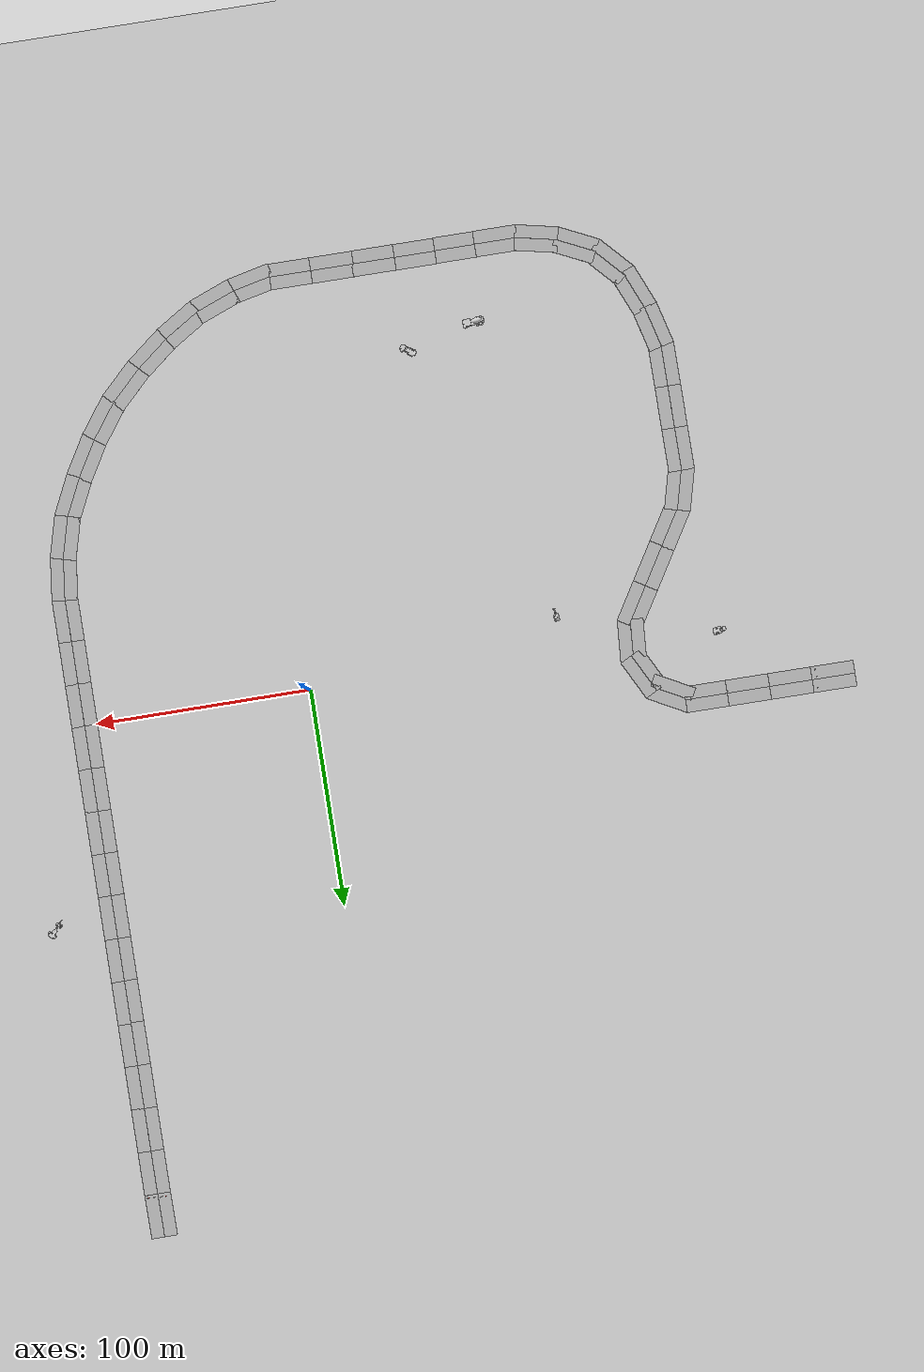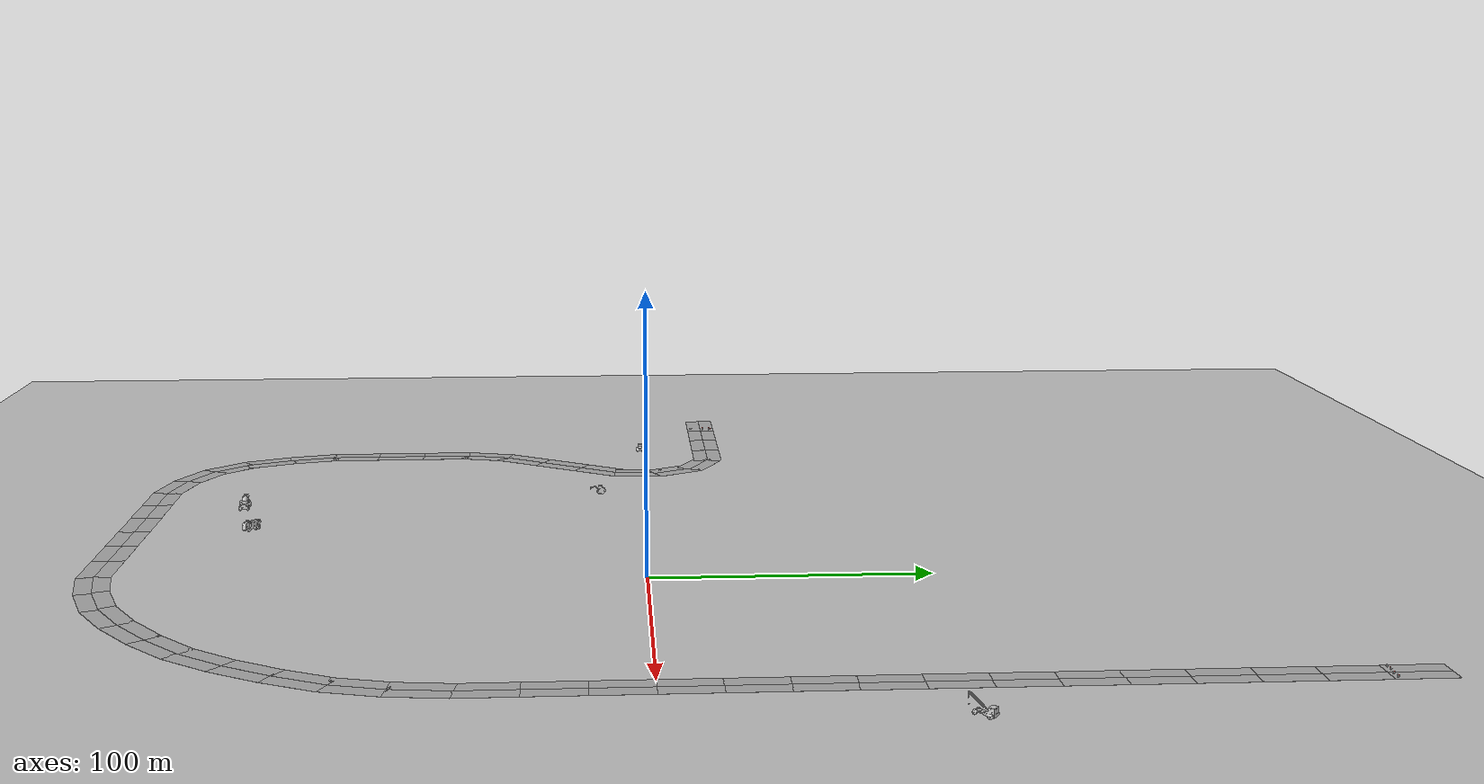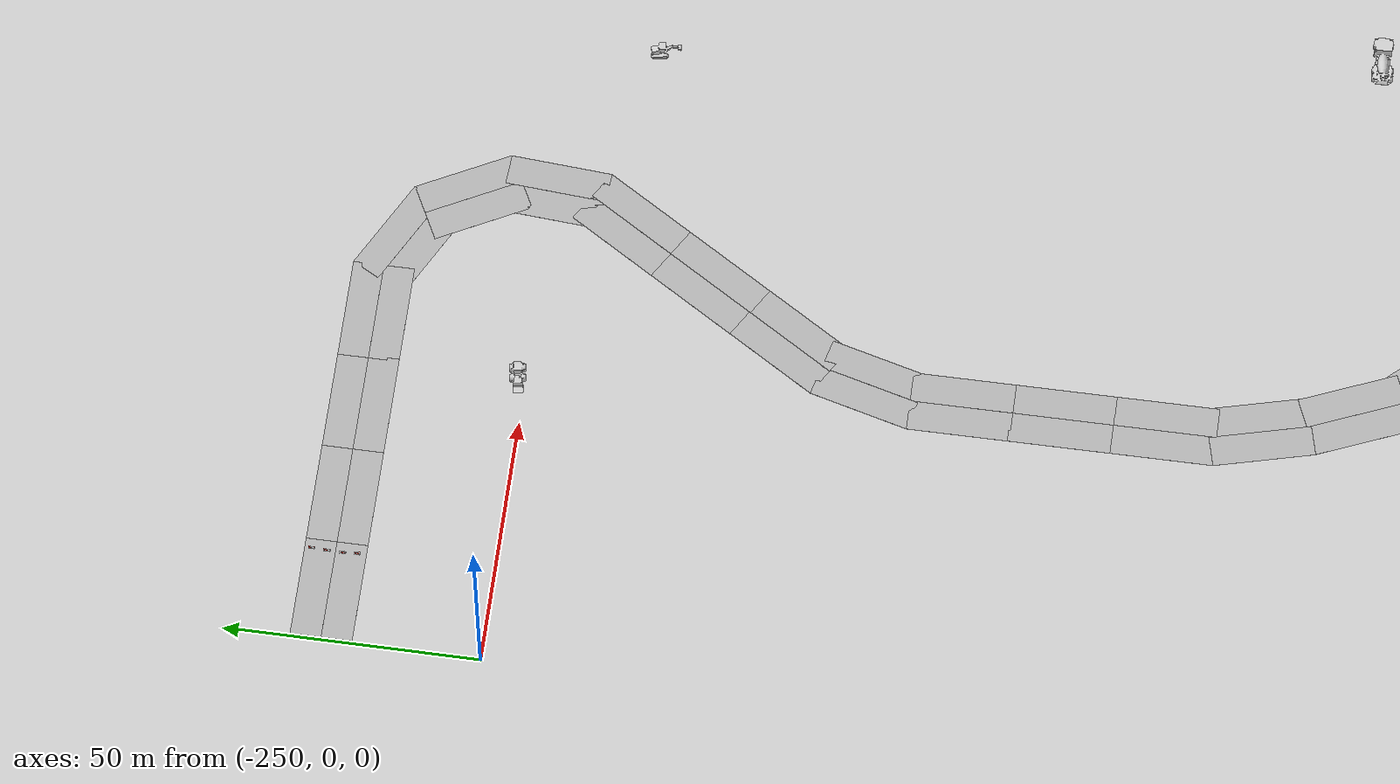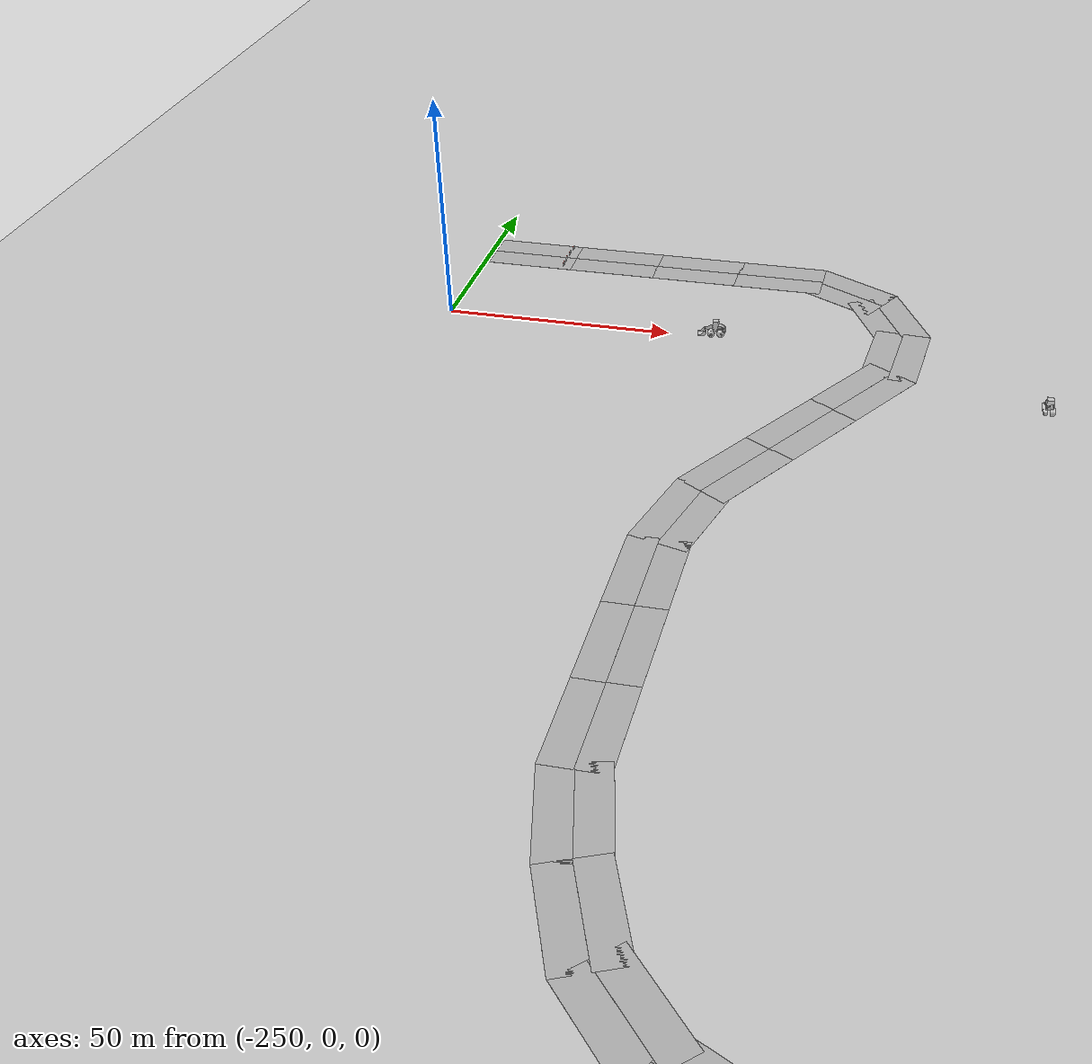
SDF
<sdf version="1.6">
 <world name="default">
  <light name="sun" type="directional">
   <pose>0 0 10 0 -0 0</pose>
   <diffuse>0.8 0.8 0.8 1</diffuse>
   <specular>0.2 0.2 0.2 1</specular>
   <attenuation>
    <range>1000</range>
    <constant>0.9</constant>
    <linear>0.01</linear>
    <quadratic>0.001</quadratic>
   </attenuation>
   <direction>-0.5 0.1 -0.9</direction>
  </light>
  <model name="ground_plane">
   <static>1</static>
   <link name="link">
    <collision name="collision">
     <geometry><plane><normal>0 0 1</normal><size>500 500</size></plane></geometry>
     <surface><friction><ode><mu>100</mu><mu2>50</mu2></ode></friction></surface>
    </collision>
    <visual name="visual">
     <cast_shadows>0</cast_shadows>
     <geometry><plane><normal>0 0 1</normal><size>500 500</size></plane></geometry>
     <material>
      <script><uri>file://media/materials/scripts/gazebo.material</uri><name>Gazebo/Grey</name></script>
     </material>
    </visual>
   </link>
  </model>
  <gravity>0 0 -9.8</gravity>
  <magnetic_field>6e-06 2.3e-05 -4.2e-05</magnetic_field>
  <atmosphere type="adiabatic"/>
  <physics name="default_physics" default="0" type="ode">
   <max_step_size>0.001</max_step_size>
   <real_time_factor>1</real_time_factor>
   <real_time_update_rate>1000</real_time_update_rate>
  </physics>
  <scene><ambient>0.4 0.4 0.4 1</ambient><background>0.7 0.7 0.7 1</background><shadows>1</shadows></scene>
  <audio><device>default</device></audio>
  <spherical_coordinates>
   <surface_model>EARTH_WGS84</surface_model>
   <latitude_deg>0</latitude_deg>
   <longitude_deg>0</longitude_deg>
   <elevation>0</elevation>
   <heading_deg>0</heading_deg>
  </spherical_coordinates>
  <model name="double_straight_road">
   <model name="straight_road">
    <link name="link">
     <inertial>
      <mass>1</mass>
      <inertia>
       <ixx>0.166667</ixx>
       <ixy>0</ixy>
       <ixz>0</ixz>
       <iyy>0.166667</iyy>
       <iyz>0</iyz>
       <izz>0.166667</izz>
      </inertia>
     </inertial>
     <visual name="visual">
      <geometry><box><size>20 6 0.02</size></box></geometry>
      <material>
       <script>
        <name>simple_road/Diffuse</name>
        <uri>model://double_straight_road/materials/scripts</uri>
        <uri>model://double_straight_road/materials/textures</uri>
       </script>
       <shader type="vertex"><normal_map>__default__</normal_map></shader>
       <ambient>0.3 0.3 0.3 1</ambient>
       <diffuse>0.7 0.7 0.7 1</diffuse>
       <specular>0.01 0.01 0.01 1</specular>
       <emissive>0 0 0 1</emissive>
      </material>
      <pose>0 0 0.01 0 -0 0</pose>
     </visual>
     <collision name="collision">
      <pose>0 0 0.01 0 -0 0</pose>
      <geometry><box><size>20 6 0.02</size></box></geometry>
      <surface>
       <friction>
        <ode><mu>1</mu><mu2>1</mu2><fdir1>0 0 0</fdir1><slip1>0</slip1><slip2>0</slip2></ode>
        <torsional>
         <coefficient>1</coefficient>
         <patch_radius>0</patch_radius>
         <surface_radius>0</surface_radius>
         <use_patch_radius>1</use_patch_radius>
         <ode><slip>0</slip></ode>
        </torsional>
       </friction>
       <bounce><restitution_coefficient>0</restitution_coefficient><threshold>1e+06</threshold></bounce>
       <contact>
        <collide_without_contact>0</collide_without_contact>
        <collide_without_contact_bitmask>1</collide_without_contact_bitmask>
        <collide_bitmask>1</collide_bitmask>
        <ode>
         <soft_cfm>0</soft_cfm>
         <soft_erp>0.2</soft_erp>
         <kp>1e+13</kp>
         <kd>1</kd>
         <max_vel>0.01</max_vel>
         <min_depth>0</min_depth>
        </ode>
        <bullet>
         <split_impulse>1</split_impulse>
         <split_impulse_penetration_threshold>-0.01</split_impulse_penetration_threshold>
         <soft_cfm>0</soft_cfm>
         <soft_erp>0.2</soft_erp>
         <kp>1e+13</kp>
         <kd>1</kd>
        </bullet>
       </contact>
      </surface>
     </collision>
    </link>
    <static>1</static>
    <pose>0 -3.0009 0 0 -0 0</pose>
   </model>
   <model name="straight_road_0">
    <link name="link">
     <inertial>
      <mass>1</mass>
      <inertia>
       <ixx>0.166667</ixx>
       <ixy>0</ixy>
       <ixz>0</ixz>
       <iyy>0.166667</iyy>
       <iyz>0</iyz>
       <izz>0.166667</izz>
      </inertia>
     </inertial>
     <visual name="visual">
      <geometry><box><size>20 6 0.02</size></box></geometry>
      <material>
       <script>
        <name>simple_road/Diffuse</name>
        <uri>model://double_straight_road/materials/scripts</uri>
        <uri>model://double_straight_road/materials/textures</uri>
       </script>
       <shader type="vertex"><normal_map>__default__</normal_map></shader>
       <ambient>0.3 0.3 0.3 1</ambient>
       <diffuse>0.7 0.7 0.7 1</diffuse>
       <specular>0.01 0.01 0.01 1</specular>
       <emissive>0 0 0 1</emissive>
      </material>
      <pose>0 0 0.01 0 -0 0</pose>
     </visual>
     <collision name="collision">
      <pose>0 0 0.01 0 -0 0</pose>
      <geometry><box><size>20 6 0.02</size></box></geometry>
      <surface>
       <friction>
        <ode><mu>1</mu><mu2>1</mu2><fdir1>0 0 0</fdir1><slip1>0</slip1><slip2>0</slip2></ode>
        <torsional>
         <coefficient>1</coefficient>
         <patch_radius>0</patch_radius>
         <surface_radius>0</surface_radius>
         <use_patch_radius>1</use_patch_radius>
         <ode><slip>0</slip></ode>
        </torsional>
       </friction>
       <bounce><restitution_coefficient>0</restitution_coefficient><threshold>1e+06</threshold></bounce>
       <contact>
        <collide_without_contact>0</collide_without_contact>
        <collide_without_contact_bitmask>1</collide_without_contact_bitmask>
        <collide_bitmask>1</collide_bitmask>
        <ode>
         <soft_cfm>0</soft_cfm>
         <soft_erp>0.2</soft_erp>
         <kp>1e+13</kp>
         <kd>1</kd>
         <max_vel>0.01</max_vel>
         <min_depth>0</min_depth>
        </ode>
        <bullet>
         <split_impulse>1</split_impulse>
         <split_impulse_penetration_threshold>-0.01</split_impulse_penetration_threshold>
         <soft_cfm>0</soft_cfm>
         <soft_erp>0.2</soft_erp>
         <kp>1e+13</kp>
         <kd>1</kd>
        </bullet>
       </contact>
      </surface>
     </collision>
    </link>
    <static>1</static>
    <pose>0 3.0009 0 0 -0 0</pose>
   </model>
   <static>1</static>
   <pose>-239.242 31.0572 0 0 -0 0</pose>
  </model>
  <model name="double_raw_road">
   <model name="raw_road">
    <link name="link">
     <inertial>
      <mass>1</mass>
      <inertia>
       <ixx>0.166667</ixx>
       <ixy>0</ixy>
       <ixz>0</ixz>
       <iyy>0.166667</iyy>
       <iyz>0</iyz>
       <izz>0.166667</izz>
      </inertia>
     </inertial>
     <visual name="visual">
      <geometry><box><size>20 6 0.02</size></box></geometry>
      <material>
       <script>
        <name>asphalt/Diffuse</name>
        <uri>model://raw_road/materials/scripts</uri>
        <uri>model://raw_road/materials/textures</uri>
       </script>
       <shader type="vertex"><normal_map>__default__</normal_map></shader>
       <ambient>0.3 0.3 0.3 1</ambient>
       <diffuse>0.7 0.7 0.7 1</diffuse>
       <specular>0.01 0.01 0.01 1</specular>
       <emissive>0 0 0 1</emissive>
      </material>
      <pose>0 0 0.01 0 -0 0</pose>
     </visual>
     <collision name="collision">
      <pose>0 0 0.01 0 -0 0</pose>
      <geometry><box><size>20 6 0.02</size></box></geometry>
      <surface>
       <friction>
        <ode><mu>1</mu><mu2>1</mu2><fdir1>0 0 0</fdir1><slip1>0</slip1><slip2>0</slip2></ode>
        <torsional>
         <coefficient>1</coefficient>
         <patch_radius>0</patch_radius>
         <surface_radius>0</surface_radius>
         <use_patch_radius>1</use_patch_radius>
         <ode><slip>0</slip></ode>
        </torsional>
       </friction>
       <bounce><restitution_coefficient>0</restitution_coefficient><threshold>1e+06</threshold></bounce>
       <contact>
        <collide_without_contact>0</collide_without_contact>
        <collide_without_contact_bitmask>1</collide_without_contact_bitmask>
        <collide_bitmask>1</collide_bitmask>
        <ode>
         <soft_cfm>0</soft_cfm>
         <soft_erp>0.2</soft_erp>
         <kp>1e+13</kp>
         <kd>1</kd>
         <max_vel>0.01</max_vel>
         <min_depth>0</min_depth>
        </ode>
        <bullet>
         <split_impulse>1</split_impulse>
         <split_impulse_penetration_threshold>-0.01</split_impulse_penetration_threshold>
         <soft_cfm>0</soft_cfm>
         <soft_erp>0.2</soft_erp>
         <kp>1e+13</kp>
         <kd>1</kd>
        </bullet>
       </contact>
      </surface>
     </collision>
    </link>
    <static>1</static>
    <pose>0 -3.0009 0 0 -0 0</pose>
   </model>
   <model name="raw_road_0">
    <link name="link">
     <inertial>
      <mass>1</mass>
      <inertia>
       <ixx>0.166667</ixx>
       <ixy>0</ixy>
       <ixz>0</ixz>
       <iyy>0.166667</iyy>
       <iyz>0</iyz>
       <izz>0.166667</izz>
      </inertia>
     </inertial>
     <visual name="visual">
      <geometry><box><size>20 6 0.02</size></box></geometry>
      <material>
       <script>
        <name>asphalt/Diffuse</name>
        <uri>model://raw_road/materials/scripts</uri>
        <uri>model://raw_road/materials/textures</uri>
       </script>
       <shader type="vertex"><normal_map>__default__</normal_map></shader>
       <ambient>0.3 0.3 0.3 1</ambient>
       <diffuse>0.7 0.7 0.7 1</diffuse>
       <specular>0.01 0.01 0.01 1</specular>
       <emissive>0 0 0 1</emissive>
      </material>
      <pose>0 0 0.01 0 -0 0</pose>
     </visual>
     <collision name="collision">
      <pose>0 0 0.01 0 -0 0</pose>
      <geometry><box><size>20 6 0.02</size></box></geometry>
      <surface>
       <friction>
        <ode><mu>1</mu><mu2>1</mu2><fdir1>0 0 0</fdir1><slip1>0</slip1><slip2>0</slip2></ode>
        <torsional>
         <coefficient>1</coefficient>
         <patch_radius>0</patch_radius>
         <surface_radius>0</surface_radius>
         <use_patch_radius>1</use_patch_radius>
         <ode><slip>0</slip></ode>
        </torsional>
       </friction>
       <bounce><restitution_coefficient>0</restitution_coefficient><threshold>1e+06</threshold></bounce>
       <contact>
        <collide_without_contact>0</collide_without_contact>
        <collide_without_contact_bitmask>1</collide_without_contact_bitmask>
        <collide_bitmask>1</collide_bitmask>
        <ode>
         <soft_cfm>0</soft_cfm>
         <soft_erp>0.2</soft_erp>
         <kp>1e+13</kp>
         <kd>1</kd>
         <max_vel>0.01</max_vel>
         <min_depth>0</min_depth>
        </ode>
        <bullet>
         <split_impulse>1</split_impulse>
         <split_impulse_penetration_threshold>-0.01</split_impulse_penetration_threshold>
         <soft_cfm>0</soft_cfm>
         <soft_erp>0.2</soft_erp>
         <kp>1e+13</kp>
         <kd>1</kd>
        </bullet>
       </contact>
      </surface>
     </collision>
    </link>
    <static>1</static>
    <pose>0 3.0009 0 0 -0 0</pose>
   </model>
   <static>1</static>
   <pose>-219.354 31.0572 0 0 -0 0</pose>
  </model>
  <model name="roadbarrier">
   <static>1</static>
   <link name="link">
    <collision name="collision">
     <geometry><mesh><scale>1 1 1</scale><uri>model://roadbarrier/meshes/roadbarrier.dae</uri></mesh></geometry>
    </collision>
    <visual name="visual">
     <geometry><mesh><scale>1 1 1</scale><uri>model://roadbarrier/meshes/roadbarrier.dae</uri></mesh></geometry>
    </visual>
   </link>
   <pose>-231.26 35.6483 -0.020038 0 0 -1.5715</pose>
  </model>
  <model name="roadbarrier_clone">
   <static>1</static>
   <link name="link">
    <collision name="collision">
     <geometry><mesh><scale>1 1 1</scale><uri>model://roadbarrier/meshes/roadbarrier.dae</uri></mesh></geometry>
    </collision>
    <visual name="visual">
     <geometry><mesh><scale>1 1 1</scale><uri>model://roadbarrier/meshes/roadbarrier.dae</uri></mesh></geometry>
    </visual>
   </link>
   <pose>-231.391 32.6954 -0.020038 0 0 -1.5715</pose>
  </model>
  <model name="roadbarrier_clone_0">
   <static>1</static>
   <link name="link">
    <collision name="collision">
     <geometry><mesh><scale>1 1 1</scale><uri>model://roadbarrier/meshes/roadbarrier.dae</uri></mesh></geometry>
    </collision>
    <visual name="visual">
     <geometry><mesh><scale>1 1 1</scale><uri>model://roadbarrier/meshes/roadbarrier.dae</uri></mesh></geometry>
    </visual>
   </link>
   <pose>-231.469 29.6372 -0.020038 0 0 -1.5715</pose>
  </model>
  <model name="roadbarrier_clone_1">
   <static>1</static>
   <link name="link">
    <collision name="collision">
     <geometry><mesh><scale>1 1 1</scale><uri>model://roadbarrier/meshes/roadbarrier.dae</uri></mesh></geometry>
    </collision>
    <visual name="visual">
     <geometry><mesh><scale>1 1 1</scale><uri>model://roadbarrier/meshes/roadbarrier.dae</uri></mesh></geometry>
    </visual>
   </link>
   <pose>-231.288 26.8494 -0.020038 0 0 -1.5715</pose>
  </model>
  <model name="double_raw_road_0">
   <model name="raw_road">
    <link name="link">
     <inertial>
      <mass>1</mass>
      <inertia>
       <ixx>0.166667</ixx>
       <ixy>0</ixy>
       <ixz>0</ixz>
       <iyy>0.166667</iyy>
       <iyz>0</iyz>
       <izz>0.166667</izz>
      </inertia>
     </inertial>
     <visual name="visual">
      <geometry><box><size>20 6 0.02</size></box></geometry>
      <material>
       <script>
        <name>asphalt/Diffuse</name>
        <uri>model://raw_road/materials/scripts</uri>
        <uri>model://raw_road/materials/textures</uri>
       </script>
       <shader type="vertex"><normal_map>__default__</normal_map></shader>
       <ambient>0.3 0.3 0.3 1</ambient>
       <diffuse>0.7 0.7 0.7 1</diffuse>
       <specular>0.01 0.01 0.01 1</specular>
       <emissive>0 0 0 1</emissive>
      </material>
      <pose>0 0 0.01 0 -0 0</pose>
     </visual>
     <collision name="collision">
      <pose>0 0 0.01 0 -0 0</pose>
      <geometry><box><size>20 6 0.02</size></box></geometry>
      <surface>
       <friction>
        <ode><mu>1</mu><mu2>1</mu2><fdir1>0 0 0</fdir1><slip1>0</slip1><slip2>0</slip2></ode>
        <torsional>
         <coefficient>1</coefficient>
         <patch_radius>0</patch_radius>
         <surface_radius>0</surface_radius>
         <use_patch_radius>1</use_patch_radius>
         <ode><slip>0</slip></ode>
        </torsional>
       </friction>
       <bounce><restitution_coefficient>0</restitution_coefficient><threshold>1e+06</threshold></bounce>
       <contact>
        <collide_without_contact>0</collide_without_contact>
        <collide_without_contact_bitmask>1</collide_without_contact_bitmask>
        <collide_bitmask>1</collide_bitmask>
        <ode>
         <soft_cfm>0</soft_cfm>
         <soft_erp>0.2</soft_erp>
         <kp>1e+13</kp>
         <kd>1</kd>
         <max_vel>0.01</max_vel>
         <min_depth>0</min_depth>
        </ode>
        <bullet>
         <split_impulse>1</split_impulse>
         <split_impulse_penetration_threshold>-0.01</split_impulse_penetration_threshold>
         <soft_cfm>0</soft_cfm>
         <soft_erp>0.2</soft_erp>
         <kp>1e+13</kp>
         <kd>1</kd>
        </bullet>
       </contact>
      </surface>
     </collision>
    </link>
    <static>1</static>
    <pose>0 -3.0009 0 0 -0 0</pose>
   </model>
   <model name="raw_road_0">
    <link name="link">
     <inertial>
      <mass>1</mass>
      <inertia>
       <ixx>0.166667</ixx>
       <ixy>0</ixy>
       <ixz>0</ixz>
       <iyy>0.166667</iyy>
       <iyz>0</iyz>
       <izz>0.166667</izz>
      </inertia>
     </inertial>
     <visual name="visual">
      <geometry><box><size>20 6 0.02</size></box></geometry>
      <material>
       <script>
        <name>asphalt/Diffuse</name>
        <uri>model://raw_road/materials/scripts</uri>
        <uri>model://raw_road/materials/textures</uri>
       </script>
       <shader type="vertex"><normal_map>__default__</normal_map></shader>
       <ambient>0.3 0.3 0.3 1</ambient>
       <diffuse>0.7 0.7 0.7 1</diffuse>
       <specular>0.01 0.01 0.01 1</specular>
       <emissive>0 0 0 1</emissive>
      </material>
      <pose>0 0 0.01 0 -0 0</pose>
     </visual>
     <collision name="collision">
      <pose>0 0 0.01 0 -0 0</pose>
      <geometry><box><size>20 6 0.02</size></box></geometry>
      <surface>
       <friction>
        <ode><mu>1</mu><mu2>1</mu2><fdir1>0 0 0</fdir1><slip1>0</slip1><slip2>0</slip2></ode>
        <torsional>
         <coefficient>1</coefficient>
         <patch_radius>0</patch_radius>
         <surface_radius>0</surface_radius>
         <use_patch_radius>1</use_patch_radius>
         <ode><slip>0</slip></ode>
        </torsional>
       </friction>
       <bounce><restitution_coefficient>0</restitution_coefficient><threshold>1e+06</threshold></bounce>
       <contact>
        <collide_without_contact>0</collide_without_contact>
        <collide_without_contact_bitmask>1</collide_without_contact_bitmask>
        <collide_bitmask>1</collide_bitmask>
        <ode>
         <soft_cfm>0</soft_cfm>
         <soft_erp>0.2</soft_erp>
         <kp>1e+13</kp>
         <kd>1</kd>
         <max_vel>0.01</max_vel>
         <min_depth>0</min_depth>
        </ode>
        <bullet>
         <split_impulse>1</split_impulse>
         <split_impulse_penetration_threshold>-0.01</split_impulse_penetration_threshold>
         <soft_cfm>0</soft_cfm>
         <soft_erp>0.2</soft_erp>
         <kp>1e+13</kp>
         <kd>1</kd>
        </bullet>
       </contact>
      </surface>
     </collision>
    </link>
    <static>1</static>
    <pose>0 3.0009 0 0 -0 0</pose>
   </model>
   <static>1</static>
   <pose>-199.558 31.0572 0 0 -0 0</pose>
  </model>
  <model name="double_raw_road_1">
   <model name="raw_road">
    <link name="link">
     <inertial>
      <mass>1</mass>
      <inertia>
       <ixx>0.166667</ixx>
       <ixy>0</ixy>
       <ixz>0</ixz>
       <iyy>0.166667</iyy>
       <iyz>0</iyz>
       <izz>0.166667</izz>
      </inertia>
     </inertial>
     <visual name="visual">
      <geometry><box><size>20 6 0.02</size></box></geometry>
      <material>
       <script>
        <name>asphalt/Diffuse</name>
        <uri>model://raw_road/materials/scripts</uri>
        <uri>model://raw_road/materials/textures</uri>
       </script>
       <shader type="vertex"><normal_map>__default__</normal_map></shader>
       <ambient>0.3 0.3 0.3 1</ambient>
       <diffuse>0.7 0.7 0.7 1</diffuse>
       <specular>0.01 0.01 0.01 1</specular>
       <emissive>0 0 0 1</emissive>
      </material>
      <pose>0 0 0.01 0 -0 0</pose>
     </visual>
     <collision name="collision">
      <pose>0 0 0.01 0 -0 0</pose>
      <geometry><box><size>20 6 0.02</size></box></geometry>
      <surface>
       <friction>
        <ode><mu>1</mu><mu2>1</mu2><fdir1>0 0 0</fdir1><slip1>0</slip1><slip2>0</slip2></ode>
        <torsional>
         <coefficient>1</coefficient>
         <patch_radius>0</patch_radius>
         <surface_radius>0</surface_radius>
         <use_patch_radius>1</use_patch_radius>
         <ode><slip>0</slip></ode>
        </torsional>
       </friction>
       <bounce><restitution_coefficient>0</restitution_coefficient><threshold>1e+06</threshold></bounce>
       <contact>
        <collide_without_contact>0</collide_without_contact>
        <collide_without_contact_bitmask>1</collide_without_contact_bitmask>
        <collide_bitmask>1</collide_bitmask>
        <ode>
         <soft_cfm>0</soft_cfm>
         <soft_erp>0.2</soft_erp>
         <kp>1e+13</kp>
         <kd>1</kd>
         <max_vel>0.01</max_vel>
         <min_depth>0</min_depth>
        </ode>
        <bullet>
         <split_impulse>1</split_impulse>
         <split_impulse_penetration_threshold>-0.01</split_impulse_penetration_threshold>
         <soft_cfm>0</soft_cfm>
         <soft_erp>0.2</soft_erp>
         <kp>1e+13</kp>
         <kd>1</kd>
        </bullet>
       </contact>
      </surface>
     </collision>
    </link>
    <static>1</static>
    <pose>0 -3.0009 0 0 -0 0</pose>
   </model>
   <model name="raw_road_0">
    <link name="link">
     <inertial>
      <mass>1</mass>
      <inertia>
       <ixx>0.166667</ixx>
       <ixy>0</ixy>
       <ixz>0</ixz>
       <iyy>0.166667</iyy>
       <iyz>0</iyz>
       <izz>0.166667</izz>
      </inertia>
     </inertial>
     <visual name="visual">
      <geometry><box><size>20 6 0.02</size></box></geometry>
      <material>
       <script>
        <name>asphalt/Diffuse</name>
        <uri>model://raw_road/materials/scripts</uri>
        <uri>model://raw_road/materials/textures</uri>
       </script>
       <shader type="vertex"><normal_map>__default__</normal_map></shader>
       <ambient>0.3 0.3 0.3 1</ambient>
       <diffuse>0.7 0.7 0.7 1</diffuse>
       <specular>0.01 0.01 0.01 1</specular>
       <emissive>0 0 0 1</emissive>
      </material>
      <pose>0 0 0.01 0 -0 0</pose>
     </visual>
     <collision name="collision">
      <pose>0 0 0.01 0 -0 0</pose>
      <geometry><box><size>20 6 0.02</size></box></geometry>
      <surface>
       <friction>
        <ode><mu>1</mu><mu2>1</mu2><fdir1>0 0 0</fdir1><slip1>0</slip1><slip2>0</slip2></ode>
        <torsional>
         <coefficient>1</coefficient>
         <patch_radius>0</patch_radius>
         <surface_radius>0</surface_radius>
         <use_patch_radius>1</use_patch_radius>
         <ode><slip>0</slip></ode>
        </torsional>
       </friction>
       <bounce><restitution_coefficient>0</restitution_coefficient><threshold>1e+06</threshold></bounce>
       <contact>
        <collide_without_contact>0</collide_without_contact>
        <collide_without_contact_bitmask>1</collide_without_contact_bitmask>
        <collide_bitmask>1</collide_bitmask>
        <ode>
         <soft_cfm>0</soft_cfm>
         <soft_erp>0.2</soft_erp>
         <kp>1e+13</kp>
         <kd>1</kd>
         <max_vel>0.01</max_vel>
         <min_depth>0</min_depth>
        </ode>
        <bullet>
         <split_impulse>1</split_impulse>
         <split_impulse_penetration_threshold>-0.01</split_impulse_penetration_threshold>
         <soft_cfm>0</soft_cfm>
         <soft_erp>0.2</soft_erp>
         <kp>1e+13</kp>
         <kd>1</kd>
        </bullet>
       </contact>
      </surface>
     </collision>
    </link>
    <static>1</static>
    <pose>0 3.0009 0 0 -0 0</pose>
   </model>
   <static>1</static>
   <pose>-180.065 31.0572 0 0 -0 0</pose>
  </model>
  <model name="double_raw_road_2">
   <model name="raw_road">
    <link name="link">
     <inertial>
      <mass>1</mass>
      <inertia>
       <ixx>0.166667</ixx>
       <ixy>0</ixy>
       <ixz>0</ixz>
       <iyy>0.166667</iyy>
       <iyz>0</iyz>
       <izz>0.166667</izz>
      </inertia>
     </inertial>
     <visual name="visual">
      <geometry><box><size>20 6 0.02</size></box></geometry>
      <material>
       <script>
        <name>asphalt/Diffuse</name>
        <uri>model://raw_road/materials/scripts</uri>
        <uri>model://raw_road/materials/textures</uri>
       </script>
       <shader type="vertex"><normal_map>__default__</normal_map></shader>
       <ambient>0.3 0.3 0.3 1</ambient>
       <diffuse>0.7 0.7 0.7 1</diffuse>
       <specular>0.01 0.01 0.01 1</specular>
       <emissive>0 0 0 1</emissive>
      </material>
      <pose>0 0 0.01 0 -0 0</pose>
     </visual>
     <collision name="collision">
      <pose>0 0 0.01 0 -0 0</pose>
      <geometry><box><size>20 6 0.02</size></box></geometry>
      <surface>
       <friction>
        <ode><mu>1</mu><mu2>1</mu2><fdir1>0 0 0</fdir1><slip1>0</slip1><slip2>0</slip2></ode>
        <torsional>
         <coefficient>1</coefficient>
         <patch_radius>0</patch_radius>
         <surface_radius>0</surface_radius>
         <use_patch_radius>1</use_patch_radius>
         <ode><slip>0</slip></ode>
        </torsional>
       </friction>
       <bounce><restitution_coefficient>0</restitution_coefficient><threshold>1e+06</threshold></bounce>
       <contact>
        <collide_without_contact>0</collide_without_contact>
        <collide_without_contact_bitmask>1</collide_without_contact_bitmask>
        <collide_bitmask>1</collide_bitmask>
        <ode>
         <soft_cfm>0</soft_cfm>
         <soft_erp>0.2</soft_erp>
         <kp>1e+13</kp>
         <kd>1</kd>
         <max_vel>0.01</max_vel>
         <min_depth>0</min_depth>
        </ode>
        <bullet>
         <split_impulse>1</split_impulse>
         <split_impulse_penetration_threshold>-0.01</split_impulse_penetration_threshold>
         <soft_cfm>0</soft_cfm>
         <soft_erp>0.2</soft_erp>
         <kp>1e+13</kp>
         <kd>1</kd>
        </bullet>
       </contact>
      </surface>
     </collision>
    </link>
    <static>1</static>
    <pose>0 -3.0009 0 0 -0 0</pose>
   </model>
   <model name="raw_road_0">
    <link name="link">
     <inertial>
      <mass>1</mass>
      <inertia>
       <ixx>0.166667</ixx>
       <ixy>0</ixy>
       <ixz>0</ixz>
       <iyy>0.166667</iyy>
       <iyz>0</iyz>
       <izz>0.166667</izz>
      </inertia>
     </inertial>
     <visual name="visual">
      <geometry><box><size>20 6 0.02</size></box></geometry>
      <material>
       <script>
        <name>asphalt/Diffuse</name>
        <uri>model://raw_road/materials/scripts</uri>
        <uri>model://raw_road/materials/textures</uri>
       </script>
       <shader type="vertex"><normal_map>__default__</normal_map></shader>
       <ambient>0.3 0.3 0.3 1</ambient>
       <diffuse>0.7 0.7 0.7 1</diffuse>
       <specular>0.01 0.01 0.01 1</specular>
       <emissive>0 0 0 1</emissive>
      </material>
      <pose>0 0 0.01 0 -0 0</pose>
     </visual>
     <collision name="collision">
      <pose>0 0 0.01 0 -0 0</pose>
      <geometry><box><size>20 6 0.02</size></box></geometry>
      <surface>
       <friction>
        <ode><mu>1</mu><mu2>1</mu2><fdir1>0 0 0</fdir1><slip1>0</slip1><slip2>0</slip2></ode>
        <torsional>
         <coefficient>1</coefficient>
         <patch_radius>0</patch_radius>
         <surface_radius>0</surface_radius>
         <use_patch_radius>1</use_patch_radius>
         <ode><slip>0</slip></ode>
        </torsional>
       </friction>
       <bounce><restitution_coefficient>0</restitution_coefficient><threshold>1e+06</threshold></bounce>
       <contact>
        <collide_without_contact>0</collide_without_contact>
        <collide_without_contact_bitmask>1</collide_without_contact_bitmask>
        <collide_bitmask>1</collide_bitmask>
        <ode>
         <soft_cfm>0</soft_cfm>
         <soft_erp>0.2</soft_erp>
         <kp>1e+13</kp>
         <kd>1</kd>
         <max_vel>0.01</max_vel>
         <min_depth>0</min_depth>
        </ode>
        <bullet>
         <split_impulse>1</split_impulse>
         <split_impulse_penetration_threshold>-0.01</split_impulse_penetration_threshold>
         <soft_cfm>0</soft_cfm>
         <soft_erp>0.2</soft_erp>
         <kp>1e+13</kp>
         <kd>1</kd>
        </bullet>
       </contact>
      </surface>
     </collision>
    </link>
    <static>1</static>
    <pose>0 3.0009 0 0 -0 0</pose>
   </model>
   <static>1</static>
   <pose>-164.074 27.0506 0 0 0 -0.490421</pose>
  </model>
  <model name="double_raw_road_2_clone">
   <model name="raw_road">
    <link name="link">
     <inertial>
      <mass>1</mass>
      <inertia>
       <ixx>0.166667</ixx>
       <ixy>0</ixy>
       <ixz>0</ixz>
       <iyy>0.166667</iyy>
       <iyz>0</iyz>
       <izz>0.166667</izz>
      </inertia>
     </inertial>
     <visual name="visual">
      <geometry><box><size>20 6 0.02</size></box></geometry>
      <material>
       <script>
        <name>asphalt/Diffuse</name>
        <uri>model://raw_road/materials/scripts</uri>
        <uri>model://raw_road/materials/textures</uri>
       </script>
       <shader type="vertex"><normal_map>__default__</normal_map></shader>
       <ambient>0.3 0.3 0.3 1</ambient>
       <diffuse>0.7 0.7 0.7 1</diffuse>
       <specular>0.01 0.01 0.01 1</specular>
       <emissive>0 0 0 1</emissive>
      </material>
      <pose>0 0 0.01 0 -0 0</pose>
     </visual>
     <collision name="collision">
      <pose>0 0 0.01 0 -0 0</pose>
      <geometry><box><size>20 6 0.02</size></box></geometry>
      <surface>
       <friction>
        <ode><mu>1</mu><mu2>1</mu2><fdir1>0 0 0</fdir1><slip1>0</slip1><slip2>0</slip2></ode>
        <torsional>
         <coefficient>1</coefficient>
         <patch_radius>0</patch_radius>
         <surface_radius>0</surface_radius>
         <use_patch_radius>1</use_patch_radius>
         <ode><slip>0</slip></ode>
        </torsional>
       </friction>
       <bounce><restitution_coefficient>0</restitution_coefficient><threshold>1e+06</threshold></bounce>
       <contact>
        <collide_without_contact>0</collide_without_contact>
        <collide_without_contact_bitmask>1</collide_without_contact_bitmask>
        <collide_bitmask>1</collide_bitmask>
        <ode>
         <soft_cfm>0</soft_cfm>
         <soft_erp>0.2</soft_erp>
         <kp>1e+13</kp>
         <kd>1</kd>
         <max_vel>0.01</max_vel>
         <min_depth>0</min_depth>
        </ode>
        <bullet>
         <split_impulse>1</split_impulse>
         <split_impulse_penetration_threshold>-0.01</split_impulse_penetration_threshold>
         <soft_cfm>0</soft_cfm>
         <soft_erp>0.2</soft_erp>
         <kp>1e+13</kp>
         <kd>1</kd>
        </bullet>
       </contact>
      </surface>
     </collision>
    </link>
    <static>1</static>
    <pose>0 -3.0009 0 0 -0 0</pose>
   </model>
   <model name="raw_road_0">
    <link name="link">
     <inertial>
      <mass>1</mass>
      <inertia>
       <ixx>0.166667</ixx>
       <ixy>0</ixy>
       <ixz>0</ixz>
       <iyy>0.166667</iyy>
       <iyz>0</iyz>
       <izz>0.166667</izz>
      </inertia>
     </inertial>
     <visual name="visual">
      <geometry><box><size>20 6 0.02</size></box></geometry>
      <material>
       <script>
        <name>asphalt/Diffuse</name>
        <uri>model://raw_road/materials/scripts</uri>
        <uri>model://raw_road/materials/textures</uri>
       </script>
       <shader type="vertex"><normal_map>__default__</normal_map></shader>
       <ambient>0.3 0.3 0.3 1</ambient>
       <diffuse>0.7 0.7 0.7 1</diffuse>
       <specular>0.01 0.01 0.01 1</specular>
       <emissive>0 0 0 1</emissive>
      </material>
      <pose>0 0 0.01 0 -0 0</pose>
     </visual>
     <collision name="collision">
      <pose>0 0 0.01 0 -0 0</pose>
      <geometry><box><size>20 6 0.02</size></box></geometry>
      <surface>
       <friction>
        <ode><mu>1</mu><mu2>1</mu2><fdir1>0 0 0</fdir1><slip1>0</slip1><slip2>0</slip2></ode>
        <torsional>
         <coefficient>1</coefficient>
         <patch_radius>0</patch_radius>
         <surface_radius>0</surface_radius>
         <use_patch_radius>1</use_patch_radius>
         <ode><slip>0</slip></ode>
        </torsional>
       </friction>
       <bounce><restitution_coefficient>0</restitution_coefficient><threshold>1e+06</threshold></bounce>
       <contact>
        <collide_without_contact>0</collide_without_contact>
        <collide_without_contact_bitmask>1</collide_without_contact_bitmask>
        <collide_bitmask>1</collide_bitmask>
        <ode>
         <soft_cfm>0</soft_cfm>
         <soft_erp>0.2</soft_erp>
         <kp>1e+13</kp>
         <kd>1</kd>
         <max_vel>0.01</max_vel>
         <min_depth>0</min_depth>
        </ode>
        <bullet>
         <split_impulse>1</split_impulse>
         <split_impulse_penetration_threshold>-0.01</split_impulse_penetration_threshold>
         <soft_cfm>0</soft_cfm>
         <soft_erp>0.2</soft_erp>
         <kp>1e+13</kp>
         <kd>1</kd>
        </bullet>
       </contact>
      </surface>
     </collision>
    </link>
    <static>1</static>
    <pose>0 3.0009 0 0 -0 0</pose>
   </model>
   <static>1</static>
   <pose>-153.201 15.9793 0 0 0 -1.09404</pose>
  </model>
  <model name="double_raw_road_2_clone_clone">
   <model name="raw_road">
    <link name="link">
     <inertial>
      <mass>1</mass>
      <inertia>
       <ixx>0.166667</ixx>
       <ixy>0</ixy>
       <ixz>0</ixz>
       <iyy>0.166667</iyy>
       <iyz>0</iyz>
       <izz>0.166667</izz>
      </inertia>
     </inertial>
     <visual name="visual">
      <geometry><box><size>20 6 0.02</size></box></geometry>
      <material>
       <script>
        <name>asphalt/Diffuse</name>
        <uri>model://raw_road/materials/scripts</uri>
        <uri>model://raw_road/materials/textures</uri>
       </script>
       <shader type="vertex"><normal_map>__default__</normal_map></shader>
       <ambient>0.3 0.3 0.3 1</ambient>
       <diffuse>0.7 0.7 0.7 1</diffuse>
       <specular>0.01 0.01 0.01 1</specular>
       <emissive>0 0 0 1</emissive>
      </material>
      <pose>0 0 0.01 0 -0 0</pose>
     </visual>
     <collision name="collision">
      <pose>0 0 0.01 0 -0 0</pose>
      <geometry><box><size>20 6 0.02</size></box></geometry>
      <surface>
       <friction>
        <ode><mu>1</mu><mu2>1</mu2><fdir1>0 0 0</fdir1><slip1>0</slip1><slip2>0</slip2></ode>
        <torsional>
         <coefficient>1</coefficient>
         <patch_radius>0</patch_radius>
         <surface_radius>0</surface_radius>
         <use_patch_radius>1</use_patch_radius>
         <ode><slip>0</slip></ode>
        </torsional>
       </friction>
       <bounce><restitution_coefficient>0</restitution_coefficient><threshold>1e+06</threshold></bounce>
       <contact>
        <collide_without_contact>0</collide_without_contact>
        <collide_without_contact_bitmask>1</collide_without_contact_bitmask>
        <collide_bitmask>1</collide_bitmask>
        <ode>
         <soft_cfm>0</soft_cfm>
         <soft_erp>0.2</soft_erp>
         <kp>1e+13</kp>
         <kd>1</kd>
         <max_vel>0.01</max_vel>
         <min_depth>0</min_depth>
        </ode>
        <bullet>
         <split_impulse>1</split_impulse>
         <split_impulse_penetration_threshold>-0.01</split_impulse_penetration_threshold>
         <soft_cfm>0</soft_cfm>
         <soft_erp>0.2</soft_erp>
         <kp>1e+13</kp>
         <kd>1</kd>
        </bullet>
       </contact>
      </surface>
     </collision>
    </link>
    <static>1</static>
    <pose>0 -3.0009 0 0 -0 0</pose>
   </model>
   <model name="raw_road_0">
    <link name="link">
     <inertial>
      <mass>1</mass>
      <inertia>
       <ixx>0.166667</ixx>
       <ixy>0</ixy>
       <ixz>0</ixz>
       <iyy>0.166667</iyy>
       <iyz>0</iyz>
       <izz>0.166667</izz>
      </inertia>
     </inertial>
     <visual name="visual">
      <geometry><box><size>20 6 0.02</size></box></geometry>
      <material>
       <script>
        <name>asphalt/Diffuse</name>
        <uri>model://raw_road/materials/scripts</uri>
        <uri>model://raw_road/materials/textures</uri>
       </script>
       <shader type="vertex"><normal_map>__default__</normal_map></shader>
       <ambient>0.3 0.3 0.3 1</ambient>
       <diffuse>0.7 0.7 0.7 1</diffuse>
       <specular>0.01 0.01 0.01 1</specular>
       <emissive>0 0 0 1</emissive>
      </material>
      <pose>0 0 0.01 0 -0 0</pose>
     </visual>
     <collision name="collision">
      <pose>0 0 0.01 0 -0 0</pose>
      <geometry><box><size>20 6 0.02</size></box></geometry>
      <surface>
       <friction>
        <ode><mu>1</mu><mu2>1</mu2><fdir1>0 0 0</fdir1><slip1>0</slip1><slip2>0</slip2></ode>
        <torsional>
         <coefficient>1</coefficient>
         <patch_radius>0</patch_radius>
         <surface_radius>0</surface_radius>
         <use_patch_radius>1</use_patch_radius>
         <ode><slip>0</slip></ode>
        </torsional>
       </friction>
       <bounce><restitution_coefficient>0</restitution_coefficient><threshold>1e+06</threshold></bounce>
       <contact>
        <collide_without_contact>0</collide_without_contact>
        <collide_without_contact_bitmask>1</collide_without_contact_bitmask>
        <collide_bitmask>1</collide_bitmask>
        <ode>
         <soft_cfm>0</soft_cfm>
         <soft_erp>0.2</soft_erp>
         <kp>1e+13</kp>
         <kd>1</kd>
         <max_vel>0.01</max_vel>
         <min_depth>0</min_depth>
        </ode>
        <bullet>
         <split_impulse>1</split_impulse>
         <split_impulse_penetration_threshold>-0.01</split_impulse_penetration_threshold>
         <soft_cfm>0</soft_cfm>
         <soft_erp>0.2</soft_erp>
         <kp>1e+13</kp>
         <kd>1</kd>
        </bullet>
       </contact>
      </surface>
     </collision>
    </link>
    <static>1</static>
    <pose>0 3.0009 0 0 -0 0</pose>
   </model>
   <static>1</static>
   <pose>-149.979 0.265816 0 0 0 -1.64156</pose>
  </model>
  <model name="double_raw_road_2_clone_clone_clone">
   <model name="raw_road">
    <link name="link">
     <inertial>
      <mass>1</mass>
      <inertia>
       <ixx>0.166667</ixx>
       <ixy>0</ixy>
       <ixz>0</ixz>
       <iyy>0.166667</iyy>
       <iyz>0</iyz>
       <izz>0.166667</izz>
      </inertia>
     </inertial>
     <visual name="visual">
      <geometry><box><size>20 6 0.02</size></box></geometry>
      <material>
       <script>
        <name>asphalt/Diffuse</name>
        <uri>model://raw_road/materials/scripts</uri>
        <uri>model://raw_road/materials/textures</uri>
       </script>
       <shader type="vertex"><normal_map>__default__</normal_map></shader>
       <ambient>0.3 0.3 0.3 1</ambient>
       <diffuse>0.7 0.7 0.7 1</diffuse>
       <specular>0.01 0.01 0.01 1</specular>
       <emissive>0 0 0 1</emissive>
      </material>
      <pose>0 0 0.01 0 -0 0</pose>
     </visual>
     <collision name="collision">
      <pose>0 0 0.01 0 -0 0</pose>
      <geometry><box><size>20 6 0.02</size></box></geometry>
      <surface>
       <friction>
        <ode><mu>1</mu><mu2>1</mu2><fdir1>0 0 0</fdir1><slip1>0</slip1><slip2>0</slip2></ode>
        <torsional>
         <coefficient>1</coefficient>
         <patch_radius>0</patch_radius>
         <surface_radius>0</surface_radius>
         <use_patch_radius>1</use_patch_radius>
         <ode><slip>0</slip></ode>
        </torsional>
       </friction>
       <bounce><restitution_coefficient>0</restitution_coefficient><threshold>1e+06</threshold></bounce>
       <contact>
        <collide_without_contact>0</collide_without_contact>
        <collide_without_contact_bitmask>1</collide_without_contact_bitmask>
        <collide_bitmask>1</collide_bitmask>
        <ode>
         <soft_cfm>0</soft_cfm>
         <soft_erp>0.2</soft_erp>
         <kp>1e+13</kp>
         <kd>1</kd>
         <max_vel>0.01</max_vel>
         <min_depth>0</min_depth>
        </ode>
        <bullet>
         <split_impulse>1</split_impulse>
         <split_impulse_penetration_threshold>-0.01</split_impulse_penetration_threshold>
         <soft_cfm>0</soft_cfm>
         <soft_erp>0.2</soft_erp>
         <kp>1e+13</kp>
         <kd>1</kd>
        </bullet>
       </contact>
      </surface>
     </collision>
    </link>
    <static>1</static>
    <pose>0 -3.0009 0 0 -0 0</pose>
   </model>
   <model name="raw_road_0">
    <link name="link">
     <inertial>
      <mass>1</mass>
      <inertia>
       <ixx>0.166667</ixx>
       <ixy>0</ixy>
       <ixz>0</ixz>
       <iyy>0.166667</iyy>
       <iyz>0</iyz>
       <izz>0.166667</izz>
      </inertia>
     </inertial>
     <visual name="visual">
      <geometry><box><size>20 6 0.02</size></box></geometry>
      <material>
       <script>
        <name>asphalt/Diffuse</name>
        <uri>model://raw_road/materials/scripts</uri>
        <uri>model://raw_road/materials/textures</uri>
       </script>
       <shader type="vertex"><normal_map>__default__</normal_map></shader>
       <ambient>0.3 0.3 0.3 1</ambient>
       <diffuse>0.7 0.7 0.7 1</diffuse>
       <specular>0.01 0.01 0.01 1</specular>
       <emissive>0 0 0 1</emissive>
      </material>
      <pose>0 0 0.01 0 -0 0</pose>
     </visual>
     <collision name="collision">
      <pose>0 0 0.01 0 -0 0</pose>
      <geometry><box><size>20 6 0.02</size></box></geometry>
      <surface>
       <friction>
        <ode><mu>1</mu><mu2>1</mu2><fdir1>0 0 0</fdir1><slip1>0</slip1><slip2>0</slip2></ode>
        <torsional>
         <coefficient>1</coefficient>
         <patch_radius>0</patch_radius>
         <surface_radius>0</surface_radius>
         <use_patch_radius>1</use_patch_radius>
         <ode><slip>0</slip></ode>
        </torsional>
       </friction>
       <bounce><restitution_coefficient>0</restitution_coefficient><threshold>1e+06</threshold></bounce>
       <contact>
        <collide_without_contact>0</collide_without_contact>
        <collide_without_contact_bitmask>1</collide_without_contact_bitmask>
        <collide_bitmask>1</collide_bitmask>
        <ode>
         <soft_cfm>0</soft_cfm>
         <soft_erp>0.2</soft_erp>
         <kp>1e+13</kp>
         <kd>1</kd>
         <max_vel>0.01</max_vel>
         <min_depth>0</min_depth>
        </ode>
        <bullet>
         <split_impulse>1</split_impulse>
         <split_impulse_penetration_threshold>-0.01</split_impulse_penetration_threshold>
         <soft_cfm>0</soft_cfm>
         <soft_erp>0.2</soft_erp>
         <kp>1e+13</kp>
         <kd>1</kd>
        </bullet>
       </contact>
      </surface>
     </collision>
    </link>
    <static>1</static>
    <pose>0 3.0009 0 0 -0 0</pose>
   </model>
   <static>1</static>
   <pose>-155.045 -15.5124 0 0 0 -2.12011</pose>
  </model>
  <model name="double_raw_road_2_clone_clone_clone_clone">
   <model name="raw_road">
    <link name="link">
     <inertial>
      <mass>1</mass>
      <inertia>
       <ixx>0.166667</ixx>
       <ixy>0</ixy>
       <ixz>0</ixz>
       <iyy>0.166667</iyy>
       <iyz>0</iyz>
       <izz>0.166667</izz>
      </inertia>
     </inertial>
     <visual name="visual">
      <geometry><box><size>20 6 0.02</size></box></geometry>
      <material>
       <script>
        <name>asphalt/Diffuse</name>
        <uri>model://raw_road/materials/scripts</uri>
        <uri>model://raw_road/materials/textures</uri>
       </script>
       <shader type="vertex"><normal_map>__default__</normal_map></shader>
       <ambient>0.3 0.3 0.3 1</ambient>
       <diffuse>0.7 0.7 0.7 1</diffuse>
       <specular>0.01 0.01 0.01 1</specular>
       <emissive>0 0 0 1</emissive>
      </material>
      <pose>0 0 0.01 0 -0 0</pose>
     </visual>
     <collision name="collision">
      <pose>0 0 0.01 0 -0 0</pose>
      <geometry><box><size>20 6 0.02</size></box></geometry>
      <surface>
       <friction>
        <ode><mu>1</mu><mu2>1</mu2><fdir1>0 0 0</fdir1><slip1>0</slip1><slip2>0</slip2></ode>
        <torsional>
         <coefficient>1</coefficient>
         <patch_radius>0</patch_radius>
         <surface_radius>0</surface_radius>
         <use_patch_radius>1</use_patch_radius>
         <ode><slip>0</slip></ode>
        </torsional>
       </friction>
       <bounce><restitution_coefficient>0</restitution_coefficient><threshold>1e+06</threshold></bounce>
       <contact>
        <collide_without_contact>0</collide_without_contact>
        <collide_without_contact_bitmask>1</collide_without_contact_bitmask>
        <collide_bitmask>1</collide_bitmask>
        <ode>
         <soft_cfm>0</soft_cfm>
         <soft_erp>0.2</soft_erp>
         <kp>1e+13</kp>
         <kd>1</kd>
         <max_vel>0.01</max_vel>
         <min_depth>0</min_depth>
        </ode>
        <bullet>
         <split_impulse>1</split_impulse>
         <split_impulse_penetration_threshold>-0.01</split_impulse_penetration_threshold>
         <soft_cfm>0</soft_cfm>
         <soft_erp>0.2</soft_erp>
         <kp>1e+13</kp>
         <kd>1</kd>
        </bullet>
       </contact>
      </surface>
     </collision>
    </link>
    <static>1</static>
    <pose>0 -3.0009 0 0 -0 0</pose>
   </model>
   <model name="raw_road_0">
    <link name="link">
     <inertial>
      <mass>1</mass>
      <inertia>
       <ixx>0.166667</ixx>
       <ixy>0</ixy>
       <ixz>0</ixz>
       <iyy>0.166667</iyy>
       <iyz>0</iyz>
       <izz>0.166667</izz>
      </inertia>
     </inertial>
     <visual name="visual">
      <geometry><box><size>20 6 0.02</size></box></geometry>
      <material>
       <script>
        <name>asphalt/Diffuse</name>
        <uri>model://raw_road/materials/scripts</uri>
        <uri>model://raw_road/materials/textures</uri>
       </script>
       <shader type="vertex"><normal_map>__default__</normal_map></shader>
       <ambient>0.3 0.3 0.3 1</ambient>
       <diffuse>0.7 0.7 0.7 1</diffuse>
       <specular>0.01 0.01 0.01 1</specular>
       <emissive>0 0 0 1</emissive>
      </material>
      <pose>0 0 0.01 0 -0 0</pose>
     </visual>
     <collision name="collision">
      <pose>0 0 0.01 0 -0 0</pose>
      <geometry><box><size>20 6 0.02</size></box></geometry>
      <surface>
       <friction>
        <ode><mu>1</mu><mu2>1</mu2><fdir1>0 0 0</fdir1><slip1>0</slip1><slip2>0</slip2></ode>
        <torsional>
         <coefficient>1</coefficient>
         <patch_radius>0</patch_radius>
         <surface_radius>0</surface_radius>
         <use_patch_radius>1</use_patch_radius>
         <ode><slip>0</slip></ode>
        </torsional>
       </friction>
       <bounce><restitution_coefficient>0</restitution_coefficient><threshold>1e+06</threshold></bounce>
       <contact>
        <collide_without_contact>0</collide_without_contact>
        <collide_without_contact_bitmask>1</collide_without_contact_bitmask>
        <collide_bitmask>1</collide_bitmask>
        <ode>
         <soft_cfm>0</soft_cfm>
         <soft_erp>0.2</soft_erp>
         <kp>1e+13</kp>
         <kd>1</kd>
         <max_vel>0.01</max_vel>
         <min_depth>0</min_depth>
        </ode>
        <bullet>
         <split_impulse>1</split_impulse>
         <split_impulse_penetration_threshold>-0.01</split_impulse_penetration_threshold>
         <soft_cfm>0</soft_cfm>
         <soft_erp>0.2</soft_erp>
         <kp>1e+13</kp>
         <kd>1</kd>
        </bullet>
       </contact>
      </surface>
     </collision>
    </link>
    <static>1</static>
    <pose>0 3.0009 0 0 -0 0</pose>
   </model>
   <static>1</static>
   <pose>-165.378 -32.4101 0 0 0 -2.12011</pose>
  </model>
  <model name="double_raw_road_2_clone_clone_clone_clone_0">
   <model name="raw_road">
    <link name="link">
     <inertial>
      <mass>1</mass>
      <inertia>
       <ixx>0.166667</ixx>
       <ixy>0</ixy>
       <ixz>0</ixz>
       <iyy>0.166667</iyy>
       <iyz>0</iyz>
       <izz>0.166667</izz>
      </inertia>
     </inertial>
     <visual name="visual">
      <geometry><box><size>20 6 0.02</size></box></geometry>
      <material>
       <script>
        <name>asphalt/Diffuse</name>
        <uri>model://raw_road/materials/scripts</uri>
        <uri>model://raw_road/materials/textures</uri>
       </script>
       <shader type="vertex"><normal_map>__default__</normal_map></shader>
       <ambient>0.3 0.3 0.3 1</ambient>
       <diffuse>0.7 0.7 0.7 1</diffuse>
       <specular>0.01 0.01 0.01 1</specular>
       <emissive>0 0 0 1</emissive>
      </material>
      <pose>0 0 0.01 0 -0 0</pose>
     </visual>
     <collision name="collision">
      <pose>0 0 0.01 0 -0 0</pose>
      <geometry><box><size>20 6 0.02</size></box></geometry>
      <surface>
       <friction>
        <ode><mu>1</mu><mu2>1</mu2><fdir1>0 0 0</fdir1><slip1>0</slip1><slip2>0</slip2></ode>
        <torsional>
         <coefficient>1</coefficient>
         <patch_radius>0</patch_radius>
         <surface_radius>0</surface_radius>
         <use_patch_radius>1</use_patch_radius>
         <ode><slip>0</slip></ode>
        </torsional>
       </friction>
       <bounce><restitution_coefficient>0</restitution_coefficient><threshold>1e+06</threshold></bounce>
       <contact>
        <collide_without_contact>0</collide_without_contact>
        <collide_without_contact_bitmask>1</collide_without_contact_bitmask>
        <collide_bitmask>1</collide_bitmask>
        <ode>
         <soft_cfm>0</soft_cfm>
         <soft_erp>0.2</soft_erp>
         <kp>1e+13</kp>
         <kd>1</kd>
         <max_vel>0.01</max_vel>
         <min_depth>0</min_depth>
        </ode>
        <bullet>
         <split_impulse>1</split_impulse>
         <split_impulse_penetration_threshold>-0.01</split_impulse_penetration_threshold>
         <soft_cfm>0</soft_cfm>
         <soft_erp>0.2</soft_erp>
         <kp>1e+13</kp>
         <kd>1</kd>
        </bullet>
       </contact>
      </surface>
     </collision>
    </link>
    <static>1</static>
    <pose>0 -3.0009 0 0 -0 0</pose>
   </model>
   <model name="raw_road_0">
    <link name="link">
     <inertial>
      <mass>1</mass>
      <inertia>
       <ixx>0.166667</ixx>
       <ixy>0</ixy>
       <ixz>0</ixz>
       <iyy>0.166667</iyy>
       <iyz>0</iyz>
       <izz>0.166667</izz>
      </inertia>
     </inertial>
     <visual name="visual">
      <geometry><box><size>20 6 0.02</size></box></geometry>
      <material>
       <script>
        <name>asphalt/Diffuse</name>
        <uri>model://raw_road/materials/scripts</uri>
        <uri>model://raw_road/materials/textures</uri>
       </script>
       <shader type="vertex"><normal_map>__default__</normal_map></shader>
       <ambient>0.3 0.3 0.3 1</ambient>
       <diffuse>0.7 0.7 0.7 1</diffuse>
       <specular>0.01 0.01 0.01 1</specular>
       <emissive>0 0 0 1</emissive>
      </material>
      <pose>0 0 0.01 0 -0 0</pose>
     </visual>
     <collision name="collision">
      <pose>0 0 0.01 0 -0 0</pose>
      <geometry><box><size>20 6 0.02</size></box></geometry>
      <surface>
       <friction>
        <ode><mu>1</mu><mu2>1</mu2><fdir1>0 0 0</fdir1><slip1>0</slip1><slip2>0</slip2></ode>
        <torsional>
         <coefficient>1</coefficient>
         <patch_radius>0</patch_radius>
         <surface_radius>0</surface_radius>
         <use_patch_radius>1</use_patch_radius>
         <ode><slip>0</slip></ode>
        </torsional>
       </friction>
       <bounce><restitution_coefficient>0</restitution_coefficient><threshold>1e+06</threshold></bounce>
       <contact>
        <collide_without_contact>0</collide_without_contact>
        <collide_without_contact_bitmask>1</collide_without_contact_bitmask>
        <collide_bitmask>1</collide_bitmask>
        <ode>
         <soft_cfm>0</soft_cfm>
         <soft_erp>0.2</soft_erp>
         <kp>1e+13</kp>
         <kd>1</kd>
         <max_vel>0.01</max_vel>
         <min_depth>0</min_depth>
        </ode>
        <bullet>
         <split_impulse>1</split_impulse>
         <split_impulse_penetration_threshold>-0.01</split_impulse_penetration_threshold>
         <soft_cfm>0</soft_cfm>
         <soft_erp>0.2</soft_erp>
         <kp>1e+13</kp>
         <kd>1</kd>
        </bullet>
       </contact>
      </surface>
     </collision>
    </link>
    <static>1</static>
    <pose>0 3.0009 0 0 -0 0</pose>
   </model>
   <static>1</static>
   <pose>-175.687 -49.2809 0 0 0 -2.12011</pose>
  </model>
  <model name="double_raw_road_2_clone_clone_clone_clone_1">
   <model name="raw_road">
    <link name="link">
     <inertial>
      <mass>1</mass>
      <inertia>
       <ixx>0.166667</ixx>
       <ixy>0</ixy>
       <ixz>0</ixz>
       <iyy>0.166667</iyy>
       <iyz>0</iyz>
       <izz>0.166667</izz>
      </inertia>
     </inertial>
     <visual name="visual">
      <geometry><box><size>20 6 0.02</size></box></geometry>
      <material>
       <script>
        <name>asphalt/Diffuse</name>
        <uri>model://raw_road/materials/scripts</uri>
        <uri>model://raw_road/materials/textures</uri>
       </script>
       <shader type="vertex"><normal_map>__default__</normal_map></shader>
       <ambient>0.3 0.3 0.3 1</ambient>
       <diffuse>0.7 0.7 0.7 1</diffuse>
       <specular>0.01 0.01 0.01 1</specular>
       <emissive>0 0 0 1</emissive>
      </material>
      <pose>0 0 0.01 0 -0 0</pose>
     </visual>
     <collision name="collision">
      <pose>0 0 0.01 0 -0 0</pose>
      <geometry><box><size>20 6 0.02</size></box></geometry>
      <surface>
       <friction>
        <ode><mu>1</mu><mu2>1</mu2><fdir1>0 0 0</fdir1><slip1>0</slip1><slip2>0</slip2></ode>
        <torsional>
         <coefficient>1</coefficient>
         <patch_radius>0</patch_radius>
         <surface_radius>0</surface_radius>
         <use_patch_radius>1</use_patch_radius>
         <ode><slip>0</slip></ode>
        </torsional>
       </friction>
       <bounce><restitution_coefficient>0</restitution_coefficient><threshold>1e+06</threshold></bounce>
       <contact>
        <collide_without_contact>0</collide_without_contact>
        <collide_without_contact_bitmask>1</collide_without_contact_bitmask>
        <collide_bitmask>1</collide_bitmask>
        <ode>
         <soft_cfm>0</soft_cfm>
         <soft_erp>0.2</soft_erp>
         <kp>1e+13</kp>
         <kd>1</kd>
         <max_vel>0.01</max_vel>
         <min_depth>0</min_depth>
        </ode>
        <bullet>
         <split_impulse>1</split_impulse>
         <split_impulse_penetration_threshold>-0.01</split_impulse_penetration_threshold>
         <soft_cfm>0</soft_cfm>
         <soft_erp>0.2</soft_erp>
         <kp>1e+13</kp>
         <kd>1</kd>
        </bullet>
       </contact>
      </surface>
     </collision>
    </link>
    <static>1</static>
    <pose>0 -3.0009 0 0 -0 0</pose>
   </model>
   <model name="raw_road_0">
    <link name="link">
     <inertial>
      <mass>1</mass>
      <inertia>
       <ixx>0.166667</ixx>
       <ixy>0</ixy>
       <ixz>0</ixz>
       <iyy>0.166667</iyy>
       <iyz>0</iyz>
       <izz>0.166667</izz>
      </inertia>
     </inertial>
     <visual name="visual">
      <geometry><box><size>20 6 0.02</size></box></geometry>
      <material>
       <script>
        <name>asphalt/Diffuse</name>
        <uri>model://raw_road/materials/scripts</uri>
        <uri>model://raw_road/materials/textures</uri>
       </script>
       <shader type="vertex"><normal_map>__default__</normal_map></shader>
       <ambient>0.3 0.3 0.3 1</ambient>
       <diffuse>0.7 0.7 0.7 1</diffuse>
       <specular>0.01 0.01 0.01 1</specular>
       <emissive>0 0 0 1</emissive>
      </material>
      <pose>0 0 0.01 0 -0 0</pose>
     </visual>
     <collision name="collision">
      <pose>0 0 0.01 0 -0 0</pose>
      <geometry><box><size>20 6 0.02</size></box></geometry>
      <surface>
       <friction>
        <ode><mu>1</mu><mu2>1</mu2><fdir1>0 0 0</fdir1><slip1>0</slip1><slip2>0</slip2></ode>
        <torsional>
         <coefficient>1</coefficient>
         <patch_radius>0</patch_radius>
         <surface_radius>0</surface_radius>
         <use_patch_radius>1</use_patch_radius>
         <ode><slip>0</slip></ode>
        </torsional>
       </friction>
       <bounce><restitution_coefficient>0</restitution_coefficient><threshold>1e+06</threshold></bounce>
       <contact>
        <collide_without_contact>0</collide_without_contact>
        <collide_without_contact_bitmask>1</collide_without_contact_bitmask>
        <collide_bitmask>1</collide_bitmask>
        <ode>
         <soft_cfm>0</soft_cfm>
         <soft_erp>0.2</soft_erp>
         <kp>1e+13</kp>
         <kd>1</kd>
         <max_vel>0.01</max_vel>
         <min_depth>0</min_depth>
        </ode>
        <bullet>
         <split_impulse>1</split_impulse>
         <split_impulse_penetration_threshold>-0.01</split_impulse_penetration_threshold>
         <soft_cfm>0</soft_cfm>
         <soft_erp>0.2</soft_erp>
         <kp>1e+13</kp>
         <kd>1</kd>
        </bullet>
       </contact>
      </surface>
     </collision>
    </link>
    <static>1</static>
    <pose>0 3.0009 0 0 -0 0</pose>
   </model>
   <static>1</static>
   <pose>-185.001 -83.9949 0 0 0 -1.56713</pose>
  </model>
  <model name="double_raw_road_2_clone_clone_clone_clone_1_clone">
   <model name="raw_road">
    <link name="link">
     <inertial>
      <mass>1</mass>
      <inertia>
       <ixx>0.166667</ixx>
       <ixy>0</ixy>
       <ixz>0</ixz>
       <iyy>0.166667</iyy>
       <iyz>0</iyz>
       <izz>0.166667</izz>
      </inertia>
     </inertial>
     <visual name="visual">
      <geometry><box><size>20 6 0.02</size></box></geometry>
      <material>
       <script>
        <name>asphalt/Diffuse</name>
        <uri>model://raw_road/materials/scripts</uri>
        <uri>model://raw_road/materials/textures</uri>
       </script>
       <shader type="vertex"><normal_map>__default__</normal_map></shader>
       <ambient>0.3 0.3 0.3 1</ambient>
       <diffuse>0.7 0.7 0.7 1</diffuse>
       <specular>0.01 0.01 0.01 1</specular>
       <emissive>0 0 0 1</emissive>
      </material>
      <pose>0 0 0.01 0 -0 0</pose>
     </visual>
     <collision name="collision">
      <pose>0 0 0.01 0 -0 0</pose>
      <geometry><box><size>20 6 0.02</size></box></geometry>
      <surface>
       <friction>
        <ode><mu>1</mu><mu2>1</mu2><fdir1>0 0 0</fdir1><slip1>0</slip1><slip2>0</slip2></ode>
        <torsional>
         <coefficient>1</coefficient>
         <patch_radius>0</patch_radius>
         <surface_radius>0</surface_radius>
         <use_patch_radius>1</use_patch_radius>
         <ode><slip>0</slip></ode>
        </torsional>
       </friction>
       <bounce><restitution_coefficient>0</restitution_coefficient><threshold>1e+06</threshold></bounce>
       <contact>
        <collide_without_contact>0</collide_without_contact>
        <collide_without_contact_bitmask>1</collide_without_contact_bitmask>
        <collide_bitmask>1</collide_bitmask>
        <ode>
         <soft_cfm>0</soft_cfm>
         <soft_erp>0.2</soft_erp>
         <kp>1e+13</kp>
         <kd>1</kd>
         <max_vel>0.01</max_vel>
         <min_depth>0</min_depth>
        </ode>
        <bullet>
         <split_impulse>1</split_impulse>
         <split_impulse_penetration_threshold>-0.01</split_impulse_penetration_threshold>
         <soft_cfm>0</soft_cfm>
         <soft_erp>0.2</soft_erp>
         <kp>1e+13</kp>
         <kd>1</kd>
        </bullet>
       </contact>
      </surface>
     </collision>
    </link>
    <static>1</static>
    <pose>0 -3.0009 0 0 -0 0</pose>
   </model>
   <model name="raw_road_0">
    <link name="link">
     <inertial>
      <mass>1</mass>
      <inertia>
       <ixx>0.166667</ixx>
       <ixy>0</ixy>
       <ixz>0</ixz>
       <iyy>0.166667</iyy>
       <iyz>0</iyz>
       <izz>0.166667</izz>
      </inertia>
     </inertial>
     <visual name="visual">
      <geometry><box><size>20 6 0.02</size></box></geometry>
      <material>
       <script>
        <name>asphalt/Diffuse</name>
        <uri>model://raw_road/materials/scripts</uri>
        <uri>model://raw_road/materials/textures</uri>
       </script>
       <shader type="vertex"><normal_map>__default__</normal_map></shader>
       <ambient>0.3 0.3 0.3 1</ambient>
       <diffuse>0.7 0.7 0.7 1</diffuse>
       <specular>0.01 0.01 0.01 1</specular>
       <emissive>0 0 0 1</emissive>
      </material>
      <pose>0 0 0.01 0 -0 0</pose>
     </visual>
     <collision name="collision">
      <pose>0 0 0.01 0 -0 0</pose>
      <geometry><box><size>20 6 0.02</size></box></geometry>
      <surface>
       <friction>
        <ode><mu>1</mu><mu2>1</mu2><fdir1>0 0 0</fdir1><slip1>0</slip1><slip2>0</slip2></ode>
        <torsional>
         <coefficient>1</coefficient>
         <patch_radius>0</patch_radius>
         <surface_radius>0</surface_radius>
         <use_patch_radius>1</use_patch_radius>
         <ode><slip>0</slip></ode>
        </torsional>
       </friction>
       <bounce><restitution_coefficient>0</restitution_coefficient><threshold>1e+06</threshold></bounce>
       <contact>
        <collide_without_contact>0</collide_without_contact>
        <collide_without_contact_bitmask>1</collide_without_contact_bitmask>
        <collide_bitmask>1</collide_bitmask>
        <ode>
         <soft_cfm>0</soft_cfm>
         <soft_erp>0.2</soft_erp>
         <kp>1e+13</kp>
         <kd>1</kd>
         <max_vel>0.01</max_vel>
         <min_depth>0</min_depth>
        </ode>
        <bullet>
         <split_impulse>1</split_impulse>
         <split_impulse_penetration_threshold>-0.01</split_impulse_penetration_threshold>
         <soft_cfm>0</soft_cfm>
         <soft_erp>0.2</soft_erp>
         <kp>1e+13</kp>
         <kd>1</kd>
        </bullet>
       </contact>
      </surface>
     </collision>
    </link>
    <static>1</static>
    <pose>0 3.0009 0 0 -0 0</pose>
   </model>
   <static>1</static>
   <pose>-182.72 -65.8558 0 0 0 -1.82432</pose>
  </model>
  <model name="double_raw_road_2_clone_clone_clone_clone_1_clone_0">
   <model name="raw_road">
    <link name="link">
     <inertial>
      <mass>1</mass>
      <inertia>
       <ixx>0.166667</ixx>
       <ixy>0</ixy>
       <ixz>0</ixz>
       <iyy>0.166667</iyy>
       <iyz>0</iyz>
       <izz>0.166667</izz>
      </inertia>
     </inertial>
     <visual name="visual">
      <geometry><box><size>20 6 0.02</size></box></geometry>
      <material>
       <script>
        <name>asphalt/Diffuse</name>
        <uri>model://raw_road/materials/scripts</uri>
        <uri>model://raw_road/materials/textures</uri>
       </script>
       <shader type="vertex"><normal_map>__default__</normal_map></shader>
       <ambient>0.3 0.3 0.3 1</ambient>
       <diffuse>0.7 0.7 0.7 1</diffuse>
       <specular>0.01 0.01 0.01 1</specular>
       <emissive>0 0 0 1</emissive>
      </material>
      <pose>0 0 0.01 0 -0 0</pose>
     </visual>
     <collision name="collision">
      <pose>0 0 0.01 0 -0 0</pose>
      <geometry><box><size>20 6 0.02</size></box></geometry>
      <surface>
       <friction>
        <ode><mu>1</mu><mu2>1</mu2><fdir1>0 0 0</fdir1><slip1>0</slip1><slip2>0</slip2></ode>
        <torsional>
         <coefficient>1</coefficient>
         <patch_radius>0</patch_radius>
         <surface_radius>0</surface_radius>
         <use_patch_radius>1</use_patch_radius>
         <ode><slip>0</slip></ode>
        </torsional>
       </friction>
       <bounce><restitution_coefficient>0</restitution_coefficient><threshold>1e+06</threshold></bounce>
       <contact>
        <collide_without_contact>0</collide_without_contact>
        <collide_without_contact_bitmask>1</collide_without_contact_bitmask>
        <collide_bitmask>1</collide_bitmask>
        <ode>
         <soft_cfm>0</soft_cfm>
         <soft_erp>0.2</soft_erp>
         <kp>1e+13</kp>
         <kd>1</kd>
         <max_vel>0.01</max_vel>
         <min_depth>0</min_depth>
        </ode>
        <bullet>
         <split_impulse>1</split_impulse>
         <split_impulse_penetration_threshold>-0.01</split_impulse_penetration_threshold>
         <soft_cfm>0</soft_cfm>
         <soft_erp>0.2</soft_erp>
         <kp>1e+13</kp>
         <kd>1</kd>
        </bullet>
       </contact>
      </surface>
     </collision>
    </link>
    <static>1</static>
    <pose>0 -3.0009 0 0 -0 0</pose>
   </model>
   <model name="raw_road_0">
    <link name="link">
     <inertial>
      <mass>1</mass>
      <inertia>
       <ixx>0.166667</ixx>
       <ixy>0</ixy>
       <ixz>0</ixz>
       <iyy>0.166667</iyy>
       <iyz>0</iyz>
       <izz>0.166667</izz>
      </inertia>
     </inertial>
     <visual name="visual">
      <geometry><box><size>20 6 0.02</size></box></geometry>
      <material>
       <script>
        <name>asphalt/Diffuse</name>
        <uri>model://raw_road/materials/scripts</uri>
        <uri>model://raw_road/materials/textures</uri>
       </script>
       <shader type="vertex"><normal_map>__default__</normal_map></shader>
       <ambient>0.3 0.3 0.3 1</ambient>
       <diffuse>0.7 0.7 0.7 1</diffuse>
       <specular>0.01 0.01 0.01 1</specular>
       <emissive>0 0 0 1</emissive>
      </material>
      <pose>0 0 0.01 0 -0 0</pose>
     </visual>
     <collision name="collision">
      <pose>0 0 0.01 0 -0 0</pose>
      <geometry><box><size>20 6 0.02</size></box></geometry>
      <surface>
       <friction>
        <ode><mu>1</mu><mu2>1</mu2><fdir1>0 0 0</fdir1><slip1>0</slip1><slip2>0</slip2></ode>
        <torsional>
         <coefficient>1</coefficient>
         <patch_radius>0</patch_radius>
         <surface_radius>0</surface_radius>
         <use_patch_radius>1</use_patch_radius>
         <ode><slip>0</slip></ode>
        </torsional>
       </friction>
       <bounce><restitution_coefficient>0</restitution_coefficient><threshold>1e+06</threshold></bounce>
       <contact>
        <collide_without_contact>0</collide_without_contact>
        <collide_without_contact_bitmask>1</collide_without_contact_bitmask>
        <collide_bitmask>1</collide_bitmask>
        <ode>
         <soft_cfm>0</soft_cfm>
         <soft_erp>0.2</soft_erp>
         <kp>1e+13</kp>
         <kd>1</kd>
         <max_vel>0.01</max_vel>
         <min_depth>0</min_depth>
        </ode>
        <bullet>
         <split_impulse>1</split_impulse>
         <split_impulse_penetration_threshold>-0.01</split_impulse_penetration_threshold>
         <soft_cfm>0</soft_cfm>
         <soft_erp>0.2</soft_erp>
         <kp>1e+13</kp>
         <kd>1</kd>
        </bullet>
       </contact>
      </surface>
     </collision>
    </link>
    <static>1</static>
    <pose>0 3.0009 0 0 -0 0</pose>
   </model>
   <static>1</static>
   <pose>-184.92 -103.613 0 0 0 -1.56713</pose>
  </model>
  <model name="double_raw_road_2_clone_clone_clone_clone_1_clone_0_clone">
   <model name="raw_road">
    <link name="link">
     <inertial>
      <mass>1</mass>
      <inertia>
       <ixx>0.166667</ixx>
       <ixy>0</ixy>
       <ixz>0</ixz>
       <iyy>0.166667</iyy>
       <iyz>0</iyz>
       <izz>0.166667</izz>
      </inertia>
     </inertial>
     <visual name="visual">
      <geometry><box><size>20 6 0.02</size></box></geometry>
      <material>
       <script>
        <name>asphalt/Diffuse</name>
        <uri>model://raw_road/materials/scripts</uri>
        <uri>model://raw_road/materials/textures</uri>
       </script>
       <shader type="vertex"><normal_map>__default__</normal_map></shader>
       <ambient>0.3 0.3 0.3 1</ambient>
       <diffuse>0.7 0.7 0.7 1</diffuse>
       <specular>0.01 0.01 0.01 1</specular>
       <emissive>0 0 0 1</emissive>
      </material>
      <pose>0 0 0.01 0 -0 0</pose>
     </visual>
     <collision name="collision">
      <pose>0 0 0.01 0 -0 0</pose>
      <geometry><box><size>20 6 0.02</size></box></geometry>
      <surface>
       <friction>
        <ode><mu>1</mu><mu2>1</mu2><fdir1>0 0 0</fdir1><slip1>0</slip1><slip2>0</slip2></ode>
        <torsional>
         <coefficient>1</coefficient>
         <patch_radius>0</patch_radius>
         <surface_radius>0</surface_radius>
         <use_patch_radius>1</use_patch_radius>
         <ode><slip>0</slip></ode>
        </torsional>
       </friction>
       <bounce><restitution_coefficient>0</restitution_coefficient><threshold>1e+06</threshold></bounce>
       <contact>
        <collide_without_contact>0</collide_without_contact>
        <collide_without_contact_bitmask>1</collide_without_contact_bitmask>
        <collide_bitmask>1</collide_bitmask>
        <ode>
         <soft_cfm>0</soft_cfm>
         <soft_erp>0.2</soft_erp>
         <kp>1e+13</kp>
         <kd>1</kd>
         <max_vel>0.01</max_vel>
         <min_depth>0</min_depth>
        </ode>
        <bullet>
         <split_impulse>1</split_impulse>
         <split_impulse_penetration_threshold>-0.01</split_impulse_penetration_threshold>
         <soft_cfm>0</soft_cfm>
         <soft_erp>0.2</soft_erp>
         <kp>1e+13</kp>
         <kd>1</kd>
        </bullet>
       </contact>
      </surface>
     </collision>
    </link>
    <static>1</static>
    <pose>0 -3.0009 0 0 -0 0</pose>
   </model>
   <model name="raw_road_0">
    <link name="link">
     <inertial>
      <mass>1</mass>
      <inertia>
       <ixx>0.166667</ixx>
       <ixy>0</ixy>
       <ixz>0</ixz>
       <iyy>0.166667</iyy>
       <iyz>0</iyz>
       <izz>0.166667</izz>
      </inertia>
     </inertial>
     <visual name="visual">
      <geometry><box><size>20 6 0.02</size></box></geometry>
      <material>
       <script>
        <name>asphalt/Diffuse</name>
        <uri>model://raw_road/materials/scripts</uri>
        <uri>model://raw_road/materials/textures</uri>
       </script>
       <shader type="vertex"><normal_map>__default__</normal_map></shader>
       <ambient>0.3 0.3 0.3 1</ambient>
       <diffuse>0.7 0.7 0.7 1</diffuse>
       <specular>0.01 0.01 0.01 1</specular>
       <emissive>0 0 0 1</emissive>
      </material>
      <pose>0 0 0.01 0 -0 0</pose>
     </visual>
     <collision name="collision">
      <pose>0 0 0.01 0 -0 0</pose>
      <geometry><box><size>20 6 0.02</size></box></geometry>
      <surface>
       <friction>
        <ode><mu>1</mu><mu2>1</mu2><fdir1>0 0 0</fdir1><slip1>0</slip1><slip2>0</slip2></ode>
        <torsional>
         <coefficient>1</coefficient>
         <patch_radius>0</patch_radius>
         <surface_radius>0</surface_radius>
         <use_patch_radius>1</use_patch_radius>
         <ode><slip>0</slip></ode>
        </torsional>
       </friction>
       <bounce><restitution_coefficient>0</restitution_coefficient><threshold>1e+06</threshold></bounce>
       <contact>
        <collide_without_contact>0</collide_without_contact>
        <collide_without_contact_bitmask>1</collide_without_contact_bitmask>
        <collide_bitmask>1</collide_bitmask>
        <ode>
         <soft_cfm>0</soft_cfm>
         <soft_erp>0.2</soft_erp>
         <kp>1e+13</kp>
         <kd>1</kd>
         <max_vel>0.01</max_vel>
         <min_depth>0</min_depth>
        </ode>
        <bullet>
         <split_impulse>1</split_impulse>
         <split_impulse_penetration_threshold>-0.01</split_impulse_penetration_threshold>
         <soft_cfm>0</soft_cfm>
         <soft_erp>0.2</soft_erp>
         <kp>1e+13</kp>
         <kd>1</kd>
        </bullet>
       </contact>
      </surface>
     </collision>
    </link>
    <static>1</static>
    <pose>0 3.0009 0 0 -0 0</pose>
   </model>
   <static>1</static>
   <pose>-184.833 -123.53 0 0 0 -1.56713</pose>
  </model>
  <model name="double_raw_road_3">
   <model name="raw_road">
    <link name="link">
     <inertial>
      <mass>1</mass>
      <inertia>
       <ixx>0.166667</ixx>
       <ixy>0</ixy>
       <ixz>0</ixz>
       <iyy>0.166667</iyy>
       <iyz>0</iyz>
       <izz>0.166667</izz>
      </inertia>
     </inertial>
     <visual name="visual">
      <geometry><box><size>20 6 0.02</size></box></geometry>
      <material>
       <script>
        <name>asphalt/Diffuse</name>
        <uri>model://raw_road/materials/scripts</uri>
        <uri>model://raw_road/materials/textures</uri>
       </script>
       <shader type="vertex"><normal_map>__default__</normal_map></shader>
       <ambient>0.3 0.3 0.3 1</ambient>
       <diffuse>0.7 0.7 0.7 1</diffuse>
       <specular>0.01 0.01 0.01 1</specular>
       <emissive>0 0 0 1</emissive>
      </material>
      <pose>0 0 0.01 0 -0 0</pose>
     </visual>
     <collision name="collision">
      <pose>0 0 0.01 0 -0 0</pose>
      <geometry><box><size>20 6 0.02</size></box></geometry>
      <surface>
       <friction>
        <ode><mu>1</mu><mu2>1</mu2><fdir1>0 0 0</fdir1><slip1>0</slip1><slip2>0</slip2></ode>
        <torsional>
         <coefficient>1</coefficient>
         <patch_radius>0</patch_radius>
         <surface_radius>0</surface_radius>
         <use_patch_radius>1</use_patch_radius>
         <ode><slip>0</slip></ode>
        </torsional>
       </friction>
       <bounce><restitution_coefficient>0</restitution_coefficient><threshold>1e+06</threshold></bounce>
       <contact>
        <collide_without_contact>0</collide_without_contact>
        <collide_without_contact_bitmask>1</collide_without_contact_bitmask>
        <collide_bitmask>1</collide_bitmask>
        <ode>
         <soft_cfm>0</soft_cfm>
         <soft_erp>0.2</soft_erp>
         <kp>1e+13</kp>
         <kd>1</kd>
         <max_vel>0.01</max_vel>
         <min_depth>0</min_depth>
        </ode>
        <bullet>
         <split_impulse>1</split_impulse>
         <split_impulse_penetration_threshold>-0.01</split_impulse_penetration_threshold>
         <soft_cfm>0</soft_cfm>
         <soft_erp>0.2</soft_erp>
         <kp>1e+13</kp>
         <kd>1</kd>
        </bullet>
       </contact>
      </surface>
     </collision>
    </link>
    <static>1</static>
    <pose>0 -3.0009 0 0 -0 0</pose>
   </model>
   <model name="raw_road_0">
    <link name="link">
     <inertial>
      <mass>1</mass>
      <inertia>
       <ixx>0.166667</ixx>
       <ixy>0</ixy>
       <ixz>0</ixz>
       <iyy>0.166667</iyy>
       <iyz>0</iyz>
       <izz>0.166667</izz>
      </inertia>
     </inertial>
     <visual name="visual">
      <geometry><box><size>20 6 0.02</size></box></geometry>
      <material>
       <script>
        <name>asphalt/Diffuse</name>
        <uri>model://raw_road/materials/scripts</uri>
        <uri>model://raw_road/materials/textures</uri>
       </script>
       <shader type="vertex"><normal_map>__default__</normal_map></shader>
       <ambient>0.3 0.3 0.3 1</ambient>
       <diffuse>0.7 0.7 0.7 1</diffuse>
       <specular>0.01 0.01 0.01 1</specular>
       <emissive>0 0 0 1</emissive>
      </material>
      <pose>0 0 0.01 0 -0 0</pose>
     </visual>
     <collision name="collision">
      <pose>0 0 0.01 0 -0 0</pose>
      <geometry><box><size>20 6 0.02</size></box></geometry>
      <surface>
       <friction>
        <ode><mu>1</mu><mu2>1</mu2><fdir1>0 0 0</fdir1><slip1>0</slip1><slip2>0</slip2></ode>
        <torsional>
         <coefficient>1</coefficient>
         <patch_radius>0</patch_radius>
         <surface_radius>0</surface_radius>
         <use_patch_radius>1</use_patch_radius>
         <ode><slip>0</slip></ode>
        </torsional>
       </friction>
       <bounce><restitution_coefficient>0</restitution_coefficient><threshold>1e+06</threshold></bounce>
       <contact>
        <collide_without_contact>0</collide_without_contact>
        <collide_without_contact_bitmask>1</collide_without_contact_bitmask>
        <collide_bitmask>1</collide_bitmask>
        <ode>
         <soft_cfm>0</soft_cfm>
         <soft_erp>0.2</soft_erp>
         <kp>1e+13</kp>
         <kd>1</kd>
         <max_vel>0.01</max_vel>
         <min_depth>0</min_depth>
        </ode>
        <bullet>
         <split_impulse>1</split_impulse>
         <split_impulse_penetration_threshold>-0.01</split_impulse_penetration_threshold>
         <soft_cfm>0</soft_cfm>
         <soft_erp>0.2</soft_erp>
         <kp>1e+13</kp>
         <kd>1</kd>
        </bullet>
       </contact>
      </surface>
     </collision>
    </link>
    <static>1</static>
    <pose>0 3.0009 0 0 -0 0</pose>
   </model>
   <static>1</static>
   <pose>-116.883 -192.58 0 0 -0 0</pose>
  </model>
  <model name="double_raw_road_2_clone_clone_clone_clone_1_clone_0_clone_clone">
   <model name="raw_road">
    <link name="link">
     <inertial>
      <mass>1</mass>
      <inertia>
       <ixx>0.166667</ixx>
       <ixy>0</ixy>
       <ixz>0</ixz>
       <iyy>0.166667</iyy>
       <iyz>0</iyz>
       <izz>0.166667</izz>
      </inertia>
     </inertial>
     <visual name="visual">
      <geometry><box><size>20 6 0.02</size></box></geometry>
      <material>
       <script>
        <name>asphalt/Diffuse</name>
        <uri>model://raw_road/materials/scripts</uri>
        <uri>model://raw_road/materials/textures</uri>
       </script>
       <shader type="vertex"><normal_map>__default__</normal_map></shader>
       <ambient>0.3 0.3 0.3 1</ambient>
       <diffuse>0.7 0.7 0.7 1</diffuse>
       <specular>0.01 0.01 0.01 1</specular>
       <emissive>0 0 0 1</emissive>
      </material>
      <pose>0 0 0.01 0 -0 0</pose>
     </visual>
     <collision name="collision">
      <pose>0 0 0.01 0 -0 0</pose>
      <geometry><box><size>20 6 0.02</size></box></geometry>
      <surface>
       <friction>
        <ode><mu>1</mu><mu2>1</mu2><fdir1>0 0 0</fdir1><slip1>0</slip1><slip2>0</slip2></ode>
        <torsional>
         <coefficient>1</coefficient>
         <patch_radius>0</patch_radius>
         <surface_radius>0</surface_radius>
         <use_patch_radius>1</use_patch_radius>
         <ode><slip>0</slip></ode>
        </torsional>
       </friction>
       <bounce><restitution_coefficient>0</restitution_coefficient><threshold>1e+06</threshold></bounce>
       <contact>
        <collide_without_contact>0</collide_without_contact>
        <collide_without_contact_bitmask>1</collide_without_contact_bitmask>
        <collide_bitmask>1</collide_bitmask>
        <ode>
         <soft_cfm>0</soft_cfm>
         <soft_erp>0.2</soft_erp>
         <kp>1e+13</kp>
         <kd>1</kd>
         <max_vel>0.01</max_vel>
         <min_depth>0</min_depth>
        </ode>
        <bullet>
         <split_impulse>1</split_impulse>
         <split_impulse_penetration_threshold>-0.01</split_impulse_penetration_threshold>
         <soft_cfm>0</soft_cfm>
         <soft_erp>0.2</soft_erp>
         <kp>1e+13</kp>
         <kd>1</kd>
        </bullet>
       </contact>
      </surface>
     </collision>
    </link>
    <static>1</static>
    <pose>0 -3.0009 0 0 -0 0</pose>
   </model>
   <model name="raw_road_0">
    <link name="link">
     <inertial>
      <mass>1</mass>
      <inertia>
       <ixx>0.166667</ixx>
       <ixy>0</ixy>
       <ixz>0</ixz>
       <iyy>0.166667</iyy>
       <iyz>0</iyz>
       <izz>0.166667</izz>
      </inertia>
     </inertial>
     <visual name="visual">
      <geometry><box><size>20 6 0.02</size></box></geometry>
      <material>
       <script>
        <name>asphalt/Diffuse</name>
        <uri>model://raw_road/materials/scripts</uri>
        <uri>model://raw_road/materials/textures</uri>
       </script>
       <shader type="vertex"><normal_map>__default__</normal_map></shader>
       <ambient>0.3 0.3 0.3 1</ambient>
       <diffuse>0.7 0.7 0.7 1</diffuse>
       <specular>0.01 0.01 0.01 1</specular>
       <emissive>0 0 0 1</emissive>
      </material>
      <pose>0 0 0.01 0 -0 0</pose>
     </visual>
     <collision name="collision">
      <pose>0 0 0.01 0 -0 0</pose>
      <geometry><box><size>20 6 0.02</size></box></geometry>
      <surface>
       <friction>
        <ode><mu>1</mu><mu2>1</mu2><fdir1>0 0 0</fdir1><slip1>0</slip1><slip2>0</slip2></ode>
        <torsional>
         <coefficient>1</coefficient>
         <patch_radius>0</patch_radius>
         <surface_radius>0</surface_radius>
         <use_patch_radius>1</use_patch_radius>
         <ode><slip>0</slip></ode>
        </torsional>
       </friction>
       <bounce><restitution_coefficient>0</restitution_coefficient><threshold>1e+06</threshold></bounce>
       <contact>
        <collide_without_contact>0</collide_without_contact>
        <collide_without_contact_bitmask>1</collide_without_contact_bitmask>
        <collide_bitmask>1</collide_bitmask>
        <ode>
         <soft_cfm>0</soft_cfm>
         <soft_erp>0.2</soft_erp>
         <kp>1e+13</kp>
         <kd>1</kd>
         <max_vel>0.01</max_vel>
         <min_depth>0</min_depth>
        </ode>
        <bullet>
         <split_impulse>1</split_impulse>
         <split_impulse_penetration_threshold>-0.01</split_impulse_penetration_threshold>
         <soft_cfm>0</soft_cfm>
         <soft_erp>0.2</soft_erp>
         <kp>1e+13</kp>
         <kd>1</kd>
        </bullet>
       </contact>
      </surface>
     </collision>
    </link>
    <static>1</static>
    <pose>0 3.0009 0 0 -0 0</pose>
   </model>
   <static>1</static>
   <pose>-182.508 -141.714 0 0 0 -1.32058</pose>
  </model>
  <model name="double_raw_road_2_clone_clone_clone_clone_1_clone_0_clone_clone_clone">
   <model name="raw_road">
    <link name="link">
     <inertial>
      <mass>1</mass>
      <inertia>
       <ixx>0.166667</ixx>
       <ixy>0</ixy>
       <ixz>0</ixz>
       <iyy>0.166667</iyy>
       <iyz>0</iyz>
       <izz>0.166667</izz>
      </inertia>
     </inertial>
     <visual name="visual">
      <geometry><box><size>20 6 0.02</size></box></geometry>
      <material>
       <script>
        <name>asphalt/Diffuse</name>
        <uri>model://raw_road/materials/scripts</uri>
        <uri>model://raw_road/materials/textures</uri>
       </script>
       <shader type="vertex"><normal_map>__default__</normal_map></shader>
       <ambient>0.3 0.3 0.3 1</ambient>
       <diffuse>0.7 0.7 0.7 1</diffuse>
       <specular>0.01 0.01 0.01 1</specular>
       <emissive>0 0 0 1</emissive>
      </material>
      <pose>0 0 0.01 0 -0 0</pose>
     </visual>
     <collision name="collision">
      <pose>0 0 0.01 0 -0 0</pose>
      <geometry><box><size>20 6 0.02</size></box></geometry>
      <surface>
       <friction>
        <ode><mu>1</mu><mu2>1</mu2><fdir1>0 0 0</fdir1><slip1>0</slip1><slip2>0</slip2></ode>
        <torsional>
         <coefficient>1</coefficient>
         <patch_radius>0</patch_radius>
         <surface_radius>0</surface_radius>
         <use_patch_radius>1</use_patch_radius>
         <ode><slip>0</slip></ode>
        </torsional>
       </friction>
       <bounce><restitution_coefficient>0</restitution_coefficient><threshold>1e+06</threshold></bounce>
       <contact>
        <collide_without_contact>0</collide_without_contact>
        <collide_without_contact_bitmask>1</collide_without_contact_bitmask>
        <collide_bitmask>1</collide_bitmask>
        <ode>
         <soft_cfm>0</soft_cfm>
         <soft_erp>0.2</soft_erp>
         <kp>1e+13</kp>
         <kd>1</kd>
         <max_vel>0.01</max_vel>
         <min_depth>0</min_depth>
        </ode>
        <bullet>
         <split_impulse>1</split_impulse>
         <split_impulse_penetration_threshold>-0.01</split_impulse_penetration_threshold>
         <soft_cfm>0</soft_cfm>
         <soft_erp>0.2</soft_erp>
         <kp>1e+13</kp>
         <kd>1</kd>
        </bullet>
       </contact>
      </surface>
     </collision>
    </link>
    <static>1</static>
    <pose>0 -3.0009 0 0 -0 0</pose>
   </model>
   <model name="raw_road_0">
    <link name="link">
     <inertial>
      <mass>1</mass>
      <inertia>
       <ixx>0.166667</ixx>
       <ixy>0</ixy>
       <ixz>0</ixz>
       <iyy>0.166667</iyy>
       <iyz>0</iyz>
       <izz>0.166667</izz>
      </inertia>
     </inertial>
     <visual name="visual">
      <geometry><box><size>20 6 0.02</size></box></geometry>
      <material>
       <script>
        <name>asphalt/Diffuse</name>
        <uri>model://raw_road/materials/scripts</uri>
        <uri>model://raw_road/materials/textures</uri>
       </script>
       <shader type="vertex"><normal_map>__default__</normal_map></shader>
       <ambient>0.3 0.3 0.3 1</ambient>
       <diffuse>0.7 0.7 0.7 1</diffuse>
       <specular>0.01 0.01 0.01 1</specular>
       <emissive>0 0 0 1</emissive>
      </material>
      <pose>0 0 0.01 0 -0 0</pose>
     </visual>
     <collision name="collision">
      <pose>0 0 0.01 0 -0 0</pose>
      <geometry><box><size>20 6 0.02</size></box></geometry>
      <surface>
       <friction>
        <ode><mu>1</mu><mu2>1</mu2><fdir1>0 0 0</fdir1><slip1>0</slip1><slip2>0</slip2></ode>
        <torsional>
         <coefficient>1</coefficient>
         <patch_radius>0</patch_radius>
         <surface_radius>0</surface_radius>
         <use_patch_radius>1</use_patch_radius>
         <ode><slip>0</slip></ode>
        </torsional>
       </friction>
       <bounce><restitution_coefficient>0</restitution_coefficient><threshold>1e+06</threshold></bounce>
       <contact>
        <collide_without_contact>0</collide_without_contact>
        <collide_without_contact_bitmask>1</collide_without_contact_bitmask>
        <collide_bitmask>1</collide_bitmask>
        <ode>
         <soft_cfm>0</soft_cfm>
         <soft_erp>0.2</soft_erp>
         <kp>1e+13</kp>
         <kd>1</kd>
         <max_vel>0.01</max_vel>
         <min_depth>0</min_depth>
        </ode>
        <bullet>
         <split_impulse>1</split_impulse>
         <split_impulse_penetration_threshold>-0.01</split_impulse_penetration_threshold>
         <soft_cfm>0</soft_cfm>
         <soft_erp>0.2</soft_erp>
         <kp>1e+13</kp>
         <kd>1</kd>
        </bullet>
       </contact>
      </surface>
     </collision>
    </link>
    <static>1</static>
    <pose>0 3.0009 0 0 -0 0</pose>
   </model>
   <static>1</static>
   <pose>-176.448 -159.75 0 0 0 -1.17376</pose>
  </model>
  <model name="double_raw_road_2_clone_clone_clone_clone_1_clone_0_clone_clone_clone_clone">
   <model name="raw_road">
    <link name="link">
     <inertial>
      <mass>1</mass>
      <inertia>
       <ixx>0.166667</ixx>
       <ixy>0</ixy>
       <ixz>0</ixz>
       <iyy>0.166667</iyy>
       <iyz>0</iyz>
       <izz>0.166667</izz>
      </inertia>
     </inertial>
     <visual name="visual">
      <geometry><box><size>20 6 0.02</size></box></geometry>
      <material>
       <script>
        <name>asphalt/Diffuse</name>
        <uri>model://raw_road/materials/scripts</uri>
        <uri>model://raw_road/materials/textures</uri>
       </script>
       <shader type="vertex"><normal_map>__default__</normal_map></shader>
       <ambient>0.3 0.3 0.3 1</ambient>
       <diffuse>0.7 0.7 0.7 1</diffuse>
       <specular>0.01 0.01 0.01 1</specular>
       <emissive>0 0 0 1</emissive>
      </material>
      <pose>0 0 0.01 0 -0 0</pose>
     </visual>
     <collision name="collision">
      <pose>0 0 0.01 0 -0 0</pose>
      <geometry><box><size>20 6 0.02</size></box></geometry>
      <surface>
       <friction>
        <ode><mu>1</mu><mu2>1</mu2><fdir1>0 0 0</fdir1><slip1>0</slip1><slip2>0</slip2></ode>
        <torsional>
         <coefficient>1</coefficient>
         <patch_radius>0</patch_radius>
         <surface_radius>0</surface_radius>
         <use_patch_radius>1</use_patch_radius>
         <ode><slip>0</slip></ode>
        </torsional>
       </friction>
       <bounce><restitution_coefficient>0</restitution_coefficient><threshold>1e+06</threshold></bounce>
       <contact>
        <collide_without_contact>0</collide_without_contact>
        <collide_without_contact_bitmask>1</collide_without_contact_bitmask>
        <collide_bitmask>1</collide_bitmask>
        <ode>
         <soft_cfm>0</soft_cfm>
         <soft_erp>0.2</soft_erp>
         <kp>1e+13</kp>
         <kd>1</kd>
         <max_vel>0.01</max_vel>
         <min_depth>0</min_depth>
        </ode>
        <bullet>
         <split_impulse>1</split_impulse>
         <split_impulse_penetration_threshold>-0.01</split_impulse_penetration_threshold>
         <soft_cfm>0</soft_cfm>
         <soft_erp>0.2</soft_erp>
         <kp>1e+13</kp>
         <kd>1</kd>
        </bullet>
       </contact>
      </surface>
     </collision>
    </link>
    <static>1</static>
    <pose>0 -3.0009 0 0 -0 0</pose>
   </model>
   <model name="raw_road_0">
    <link name="link">
     <inertial>
      <mass>1</mass>
      <inertia>
       <ixx>0.166667</ixx>
       <ixy>0</ixy>
       <ixz>0</ixz>
       <iyy>0.166667</iyy>
       <iyz>0</iyz>
       <izz>0.166667</izz>
      </inertia>
     </inertial>
     <visual name="visual">
      <geometry><box><size>20 6 0.02</size></box></geometry>
      <material>
       <script>
        <name>asphalt/Diffuse</name>
        <uri>model://raw_road/materials/scripts</uri>
        <uri>model://raw_road/materials/textures</uri>
       </script>
       <shader type="vertex"><normal_map>__default__</normal_map></shader>
       <ambient>0.3 0.3 0.3 1</ambient>
       <diffuse>0.7 0.7 0.7 1</diffuse>
       <specular>0.01 0.01 0.01 1</specular>
       <emissive>0 0 0 1</emissive>
      </material>
      <pose>0 0 0.01 0 -0 0</pose>
     </visual>
     <collision name="collision">
      <pose>0 0 0.01 0 -0 0</pose>
      <geometry><box><size>20 6 0.02</size></box></geometry>
      <surface>
       <friction>
        <ode><mu>1</mu><mu2>1</mu2><fdir1>0 0 0</fdir1><slip1>0</slip1><slip2>0</slip2></ode>
        <torsional>
         <coefficient>1</coefficient>
         <patch_radius>0</patch_radius>
         <surface_radius>0</surface_radius>
         <use_patch_radius>1</use_patch_radius>
         <ode><slip>0</slip></ode>
        </torsional>
       </friction>
       <bounce><restitution_coefficient>0</restitution_coefficient><threshold>1e+06</threshold></bounce>
       <contact>
        <collide_without_contact>0</collide_without_contact>
        <collide_without_contact_bitmask>1</collide_without_contact_bitmask>
        <collide_bitmask>1</collide_bitmask>
        <ode>
         <soft_cfm>0</soft_cfm>
         <soft_erp>0.2</soft_erp>
         <kp>1e+13</kp>
         <kd>1</kd>
         <max_vel>0.01</max_vel>
         <min_depth>0</min_depth>
        </ode>
        <bullet>
         <split_impulse>1</split_impulse>
         <split_impulse_penetration_threshold>-0.01</split_impulse_penetration_threshold>
         <soft_cfm>0</soft_cfm>
         <soft_erp>0.2</soft_erp>
         <kp>1e+13</kp>
         <kd>1</kd>
        </bullet>
       </contact>
      </surface>
     </collision>
    </link>
    <static>1</static>
    <pose>0 3.0009 0 0 -0 0</pose>
   </model>
   <static>1</static>
   <pose>-166.879 -174.491 0 0 0 -0.821411</pose>
  </model>
  <model name="double_raw_road_2_clone_clone_clone_clone_1_clone_0_clone_clone_clone_clone_clone">
   <model name="raw_road">
    <link name="link">
     <inertial>
      <mass>1</mass>
      <inertia>
       <ixx>0.166667</ixx>
       <ixy>0</ixy>
       <ixz>0</ixz>
       <iyy>0.166667</iyy>
       <iyz>0</iyz>
       <izz>0.166667</izz>
      </inertia>
     </inertial>
     <visual name="visual">
      <geometry><box><size>20 6 0.02</size></box></geometry>
      <material>
       <script>
        <name>asphalt/Diffuse</name>
        <uri>model://raw_road/materials/scripts</uri>
        <uri>model://raw_road/materials/textures</uri>
       </script>
       <shader type="vertex"><normal_map>__default__</normal_map></shader>
       <ambient>0.3 0.3 0.3 1</ambient>
       <diffuse>0.7 0.7 0.7 1</diffuse>
       <specular>0.01 0.01 0.01 1</specular>
       <emissive>0 0 0 1</emissive>
      </material>
      <pose>0 0 0.01 0 -0 0</pose>
     </visual>
     <collision name="collision">
      <pose>0 0 0.01 0 -0 0</pose>
      <geometry><box><size>20 6 0.02</size></box></geometry>
      <surface>
       <friction>
        <ode><mu>1</mu><mu2>1</mu2><fdir1>0 0 0</fdir1><slip1>0</slip1><slip2>0</slip2></ode>
        <torsional>
         <coefficient>1</coefficient>
         <patch_radius>0</patch_radius>
         <surface_radius>0</surface_radius>
         <use_patch_radius>1</use_patch_radius>
         <ode><slip>0</slip></ode>
        </torsional>
       </friction>
       <bounce><restitution_coefficient>0</restitution_coefficient><threshold>1e+06</threshold></bounce>
       <contact>
        <collide_without_contact>0</collide_without_contact>
        <collide_without_contact_bitmask>1</collide_without_contact_bitmask>
        <collide_bitmask>1</collide_bitmask>
        <ode>
         <soft_cfm>0</soft_cfm>
         <soft_erp>0.2</soft_erp>
         <kp>1e+13</kp>
         <kd>1</kd>
         <max_vel>0.01</max_vel>
         <min_depth>0</min_depth>
        </ode>
        <bullet>
         <split_impulse>1</split_impulse>
         <split_impulse_penetration_threshold>-0.01</split_impulse_penetration_threshold>
         <soft_cfm>0</soft_cfm>
         <soft_erp>0.2</soft_erp>
         <kp>1e+13</kp>
         <kd>1</kd>
        </bullet>
       </contact>
      </surface>
     </collision>
    </link>
    <static>1</static>
    <pose>0 -3.0009 0 0 -0 0</pose>
   </model>
   <model name="raw_road_0">
    <link name="link">
     <inertial>
      <mass>1</mass>
      <inertia>
       <ixx>0.166667</ixx>
       <ixy>0</ixy>
       <ixz>0</ixz>
       <iyy>0.166667</iyy>
       <iyz>0</iyz>
       <izz>0.166667</izz>
      </inertia>
     </inertial>
     <visual name="visual">
      <geometry><box><size>20 6 0.02</size></box></geometry>
      <material>
       <script>
        <name>asphalt/Diffuse</name>
        <uri>model://raw_road/materials/scripts</uri>
        <uri>model://raw_road/materials/textures</uri>
       </script>
       <shader type="vertex"><normal_map>__default__</normal_map></shader>
       <ambient>0.3 0.3 0.3 1</ambient>
       <diffuse>0.7 0.7 0.7 1</diffuse>
       <specular>0.01 0.01 0.01 1</specular>
       <emissive>0 0 0 1</emissive>
      </material>
      <pose>0 0 0.01 0 -0 0</pose>
     </visual>
     <collision name="collision">
      <pose>0 0 0.01 0 -0 0</pose>
      <geometry><box><size>20 6 0.02</size></box></geometry>
      <surface>
       <friction>
        <ode><mu>1</mu><mu2>1</mu2><fdir1>0 0 0</fdir1><slip1>0</slip1><slip2>0</slip2></ode>
        <torsional>
         <coefficient>1</coefficient>
         <patch_radius>0</patch_radius>
         <surface_radius>0</surface_radius>
         <use_patch_radius>1</use_patch_radius>
         <ode><slip>0</slip></ode>
        </torsional>
       </friction>
       <bounce><restitution_coefficient>0</restitution_coefficient><threshold>1e+06</threshold></bounce>
       <contact>
        <collide_without_contact>0</collide_without_contact>
        <collide_without_contact_bitmask>1</collide_without_contact_bitmask>
        <collide_bitmask>1</collide_bitmask>
        <ode>
         <soft_cfm>0</soft_cfm>
         <soft_erp>0.2</soft_erp>
         <kp>1e+13</kp>
         <kd>1</kd>
         <max_vel>0.01</max_vel>
         <min_depth>0</min_depth>
        </ode>
        <bullet>
         <split_impulse>1</split_impulse>
         <split_impulse_penetration_threshold>-0.01</split_impulse_penetration_threshold>
         <soft_cfm>0</soft_cfm>
         <soft_erp>0.2</soft_erp>
         <kp>1e+13</kp>
         <kd>1</kd>
        </bullet>
       </contact>
      </surface>
     </collision>
    </link>
    <static>1</static>
    <pose>0 3.0009 0 0 -0 0</pose>
   </model>
   <static>1</static>
   <pose>-152.835 -184.806 0 0 0 -0.445724</pose>
  </model>
  <model name="double_raw_road_2_clone_clone_clone_clone_1_clone_0_clone_clone_clone_clone_clone_clone">
   <model name="raw_road">
    <link name="link">
     <inertial>
      <mass>1</mass>
      <inertia>
       <ixx>0.166667</ixx>
       <ixy>0</ixy>
       <ixz>0</ixz>
       <iyy>0.166667</iyy>
       <iyz>0</iyz>
       <izz>0.166667</izz>
      </inertia>
     </inertial>
     <visual name="visual">
      <geometry><box><size>20 6 0.02</size></box></geometry>
      <material>
       <script>
        <name>asphalt/Diffuse</name>
        <uri>model://raw_road/materials/scripts</uri>
        <uri>model://raw_road/materials/textures</uri>
       </script>
       <shader type="vertex"><normal_map>__default__</normal_map></shader>
       <ambient>0.3 0.3 0.3 1</ambient>
       <diffuse>0.7 0.7 0.7 1</diffuse>
       <specular>0.01 0.01 0.01 1</specular>
       <emissive>0 0 0 1</emissive>
      </material>
      <pose>0 0 0.01 0 -0 0</pose>
     </visual>
     <collision name="collision">
      <pose>0 0 0.01 0 -0 0</pose>
      <geometry><box><size>20 6 0.02</size></box></geometry>
      <surface>
       <friction>
        <ode><mu>1</mu><mu2>1</mu2><fdir1>0 0 0</fdir1><slip1>0</slip1><slip2>0</slip2></ode>
        <torsional>
         <coefficient>1</coefficient>
         <patch_radius>0</patch_radius>
         <surface_radius>0</surface_radius>
         <use_patch_radius>1</use_patch_radius>
         <ode><slip>0</slip></ode>
        </torsional>
       </friction>
       <bounce><restitution_coefficient>0</restitution_coefficient><threshold>1e+06</threshold></bounce>
       <contact>
        <collide_without_contact>0</collide_without_contact>
        <collide_without_contact_bitmask>1</collide_without_contact_bitmask>
        <collide_bitmask>1</collide_bitmask>
        <ode>
         <soft_cfm>0</soft_cfm>
         <soft_erp>0.2</soft_erp>
         <kp>1e+13</kp>
         <kd>1</kd>
         <max_vel>0.01</max_vel>
         <min_depth>0</min_depth>
        </ode>
        <bullet>
         <split_impulse>1</split_impulse>
         <split_impulse_penetration_threshold>-0.01</split_impulse_penetration_threshold>
         <soft_cfm>0</soft_cfm>
         <soft_erp>0.2</soft_erp>
         <kp>1e+13</kp>
         <kd>1</kd>
        </bullet>
       </contact>
      </surface>
     </collision>
    </link>
    <static>1</static>
    <pose>0 -3.0009 0 0 -0 0</pose>
   </model>
   <model name="raw_road_0">
    <link name="link">
     <inertial>
      <mass>1</mass>
      <inertia>
       <ixx>0.166667</ixx>
       <ixy>0</ixy>
       <ixz>0</ixz>
       <iyy>0.166667</iyy>
       <iyz>0</iyz>
       <izz>0.166667</izz>
      </inertia>
     </inertial>
     <visual name="visual">
      <geometry><box><size>20 6 0.02</size></box></geometry>
      <material>
       <script>
        <name>asphalt/Diffuse</name>
        <uri>model://raw_road/materials/scripts</uri>
        <uri>model://raw_road/materials/textures</uri>
       </script>
       <shader type="vertex"><normal_map>__default__</normal_map></shader>
       <ambient>0.3 0.3 0.3 1</ambient>
       <diffuse>0.7 0.7 0.7 1</diffuse>
       <specular>0.01 0.01 0.01 1</specular>
       <emissive>0 0 0 1</emissive>
      </material>
      <pose>0 0 0.01 0 -0 0</pose>
     </visual>
     <collision name="collision">
      <pose>0 0 0.01 0 -0 0</pose>
      <geometry><box><size>20 6 0.02</size></box></geometry>
      <surface>
       <friction>
        <ode><mu>1</mu><mu2>1</mu2><fdir1>0 0 0</fdir1><slip1>0</slip1><slip2>0</slip2></ode>
        <torsional>
         <coefficient>1</coefficient>
         <patch_radius>0</patch_radius>
         <surface_radius>0</surface_radius>
         <use_patch_radius>1</use_patch_radius>
         <ode><slip>0</slip></ode>
        </torsional>
       </friction>
       <bounce><restitution_coefficient>0</restitution_coefficient><threshold>1e+06</threshold></bounce>
       <contact>
        <collide_without_contact>0</collide_without_contact>
        <collide_without_contact_bitmask>1</collide_without_contact_bitmask>
        <collide_bitmask>1</collide_bitmask>
        <ode>
         <soft_cfm>0</soft_cfm>
         <soft_erp>0.2</soft_erp>
         <kp>1e+13</kp>
         <kd>1</kd>
         <max_vel>0.01</max_vel>
         <min_depth>0</min_depth>
        </ode>
        <bullet>
         <split_impulse>1</split_impulse>
         <split_impulse_penetration_threshold>-0.01</split_impulse_penetration_threshold>
         <soft_cfm>0</soft_cfm>
         <soft_erp>0.2</soft_erp>
         <kp>1e+13</kp>
         <kd>1</kd>
        </bullet>
       </contact>
      </surface>
     </collision>
    </link>
    <static>1</static>
    <pose>0 3.0009 0 0 -0 0</pose>
   </model>
   <static>1</static>
   <pose>-135.446 -190.694 0 0 0 -0.20754</pose>
  </model>
  <model name="double_raw_road_4">
   <model name="raw_road">
    <link name="link">
     <inertial>
      <mass>1</mass>
      <inertia>
       <ixx>0.166667</ixx>
       <ixy>0</ixy>
       <ixz>0</ixz>
       <iyy>0.166667</iyy>
       <iyz>0</iyz>
       <izz>0.166667</izz>
      </inertia>
     </inertial>
     <visual name="visual">
      <geometry><box><size>20 6 0.02</size></box></geometry>
      <material>
       <script>
        <name>asphalt/Diffuse</name>
        <uri>model://raw_road/materials/scripts</uri>
        <uri>model://raw_road/materials/textures</uri>
       </script>
       <shader type="vertex"><normal_map>__default__</normal_map></shader>
       <ambient>0.3 0.3 0.3 1</ambient>
       <diffuse>0.7 0.7 0.7 1</diffuse>
       <specular>0.01 0.01 0.01 1</specular>
       <emissive>0 0 0 1</emissive>
      </material>
      <pose>0 0 0.01 0 -0 0</pose>
     </visual>
     <collision name="collision">
      <pose>0 0 0.01 0 -0 0</pose>
      <geometry><box><size>20 6 0.02</size></box></geometry>
      <surface>
       <friction>
        <ode><mu>1</mu><mu2>1</mu2><fdir1>0 0 0</fdir1><slip1>0</slip1><slip2>0</slip2></ode>
        <torsional>
         <coefficient>1</coefficient>
         <patch_radius>0</patch_radius>
         <surface_radius>0</surface_radius>
         <use_patch_radius>1</use_patch_radius>
         <ode><slip>0</slip></ode>
        </torsional>
       </friction>
       <bounce><restitution_coefficient>0</restitution_coefficient><threshold>1e+06</threshold></bounce>
       <contact>
        <collide_without_contact>0</collide_without_contact>
        <collide_without_contact_bitmask>1</collide_without_contact_bitmask>
        <collide_bitmask>1</collide_bitmask>
        <ode>
         <soft_cfm>0</soft_cfm>
         <soft_erp>0.2</soft_erp>
         <kp>1e+13</kp>
         <kd>1</kd>
         <max_vel>0.01</max_vel>
         <min_depth>0</min_depth>
        </ode>
        <bullet>
         <split_impulse>1</split_impulse>
         <split_impulse_penetration_threshold>-0.01</split_impulse_penetration_threshold>
         <soft_cfm>0</soft_cfm>
         <soft_erp>0.2</soft_erp>
         <kp>1e+13</kp>
         <kd>1</kd>
        </bullet>
       </contact>
      </surface>
     </collision>
    </link>
    <static>1</static>
    <pose>0 -3.0009 0 0 -0 0</pose>
   </model>
   <model name="raw_road_0">
    <link name="link">
     <inertial>
      <mass>1</mass>
      <inertia>
       <ixx>0.166667</ixx>
       <ixy>0</ixy>
       <ixz>0</ixz>
       <iyy>0.166667</iyy>
       <iyz>0</iyz>
       <izz>0.166667</izz>
      </inertia>
     </inertial>
     <visual name="visual">
      <geometry><box><size>20 6 0.02</size></box></geometry>
      <material>
       <script>
        <name>asphalt/Diffuse</name>
        <uri>model://raw_road/materials/scripts</uri>
        <uri>model://raw_road/materials/textures</uri>
       </script>
       <shader type="vertex"><normal_map>__default__</normal_map></shader>
       <ambient>0.3 0.3 0.3 1</ambient>
       <diffuse>0.7 0.7 0.7 1</diffuse>
       <specular>0.01 0.01 0.01 1</specular>
       <emissive>0 0 0 1</emissive>
      </material>
      <pose>0 0 0.01 0 -0 0</pose>
     </visual>
     <collision name="collision">
      <pose>0 0 0.01 0 -0 0</pose>
      <geometry><box><size>20 6 0.02</size></box></geometry>
      <surface>
       <friction>
        <ode><mu>1</mu><mu2>1</mu2><fdir1>0 0 0</fdir1><slip1>0</slip1><slip2>0</slip2></ode>
        <torsional>
         <coefficient>1</coefficient>
         <patch_radius>0</patch_radius>
         <surface_radius>0</surface_radius>
         <use_patch_radius>1</use_patch_radius>
         <ode><slip>0</slip></ode>
        </torsional>
       </friction>
       <bounce><restitution_coefficient>0</restitution_coefficient><threshold>1e+06</threshold></bounce>
       <contact>
        <collide_without_contact>0</collide_without_contact>
        <collide_without_contact_bitmask>1</collide_without_contact_bitmask>
        <collide_bitmask>1</collide_bitmask>
        <ode>
         <soft_cfm>0</soft_cfm>
         <soft_erp>0.2</soft_erp>
         <kp>1e+13</kp>
         <kd>1</kd>
         <max_vel>0.01</max_vel>
         <min_depth>0</min_depth>
        </ode>
        <bullet>
         <split_impulse>1</split_impulse>
         <split_impulse_penetration_threshold>-0.01</split_impulse_penetration_threshold>
         <soft_cfm>0</soft_cfm>
         <soft_erp>0.2</soft_erp>
         <kp>1e+13</kp>
         <kd>1</kd>
        </bullet>
       </contact>
      </surface>
     </collision>
    </link>
    <static>1</static>
    <pose>0 3.0009 0 0 -0 0</pose>
   </model>
   <static>1</static>
   <pose>-98.2578 -192.463 0 0 -0 0</pose>
  </model>
  <model name="double_raw_road_4_clone">
   <model name="raw_road">
    <link name="link">
     <inertial>
      <mass>1</mass>
      <inertia>
       <ixx>0.166667</ixx>
       <ixy>0</ixy>
       <ixz>0</ixz>
       <iyy>0.166667</iyy>
       <iyz>0</iyz>
       <izz>0.166667</izz>
      </inertia>
     </inertial>
     <visual name="visual">
      <geometry><box><size>20 6 0.02</size></box></geometry>
      <material>
       <script>
        <name>asphalt/Diffuse</name>
        <uri>model://raw_road/materials/scripts</uri>
        <uri>model://raw_road/materials/textures</uri>
       </script>
       <shader type="vertex"><normal_map>__default__</normal_map></shader>
       <ambient>0.3 0.3 0.3 1</ambient>
       <diffuse>0.7 0.7 0.7 1</diffuse>
       <specular>0.01 0.01 0.01 1</specular>
       <emissive>0 0 0 1</emissive>
      </material>
      <pose>0 0 0.01 0 -0 0</pose>
     </visual>
     <collision name="collision">
      <pose>0 0 0.01 0 -0 0</pose>
      <geometry><box><size>20 6 0.02</size></box></geometry>
      <surface>
       <friction>
        <ode><mu>1</mu><mu2>1</mu2><fdir1>0 0 0</fdir1><slip1>0</slip1><slip2>0</slip2></ode>
        <torsional>
         <coefficient>1</coefficient>
         <patch_radius>0</patch_radius>
         <surface_radius>0</surface_radius>
         <use_patch_radius>1</use_patch_radius>
         <ode><slip>0</slip></ode>
        </torsional>
       </friction>
       <bounce><restitution_coefficient>0</restitution_coefficient><threshold>1e+06</threshold></bounce>
       <contact>
        <collide_without_contact>0</collide_without_contact>
        <collide_without_contact_bitmask>1</collide_without_contact_bitmask>
        <collide_bitmask>1</collide_bitmask>
        <ode>
         <soft_cfm>0</soft_cfm>
         <soft_erp>0.2</soft_erp>
         <kp>1e+13</kp>
         <kd>1</kd>
         <max_vel>0.01</max_vel>
         <min_depth>0</min_depth>
        </ode>
        <bullet>
         <split_impulse>1</split_impulse>
         <split_impulse_penetration_threshold>-0.01</split_impulse_penetration_threshold>
         <soft_cfm>0</soft_cfm>
         <soft_erp>0.2</soft_erp>
         <kp>1e+13</kp>
         <kd>1</kd>
        </bullet>
       </contact>
      </surface>
     </collision>
    </link>
    <static>1</static>
    <pose>0 -3.0009 0 0 -0 0</pose>
   </model>
   <model name="raw_road_0">
    <link name="link">
     <inertial>
      <mass>1</mass>
      <inertia>
       <ixx>0.166667</ixx>
       <ixy>0</ixy>
       <ixz>0</ixz>
       <iyy>0.166667</iyy>
       <iyz>0</iyz>
       <izz>0.166667</izz>
      </inertia>
     </inertial>
     <visual name="visual">
      <geometry><box><size>20 6 0.02</size></box></geometry>
      <material>
       <script>
        <name>asphalt/Diffuse</name>
        <uri>model://raw_road/materials/scripts</uri>
        <uri>model://raw_road/materials/textures</uri>
       </script>
       <shader type="vertex"><normal_map>__default__</normal_map></shader>
       <ambient>0.3 0.3 0.3 1</ambient>
       <diffuse>0.7 0.7 0.7 1</diffuse>
       <specular>0.01 0.01 0.01 1</specular>
       <emissive>0 0 0 1</emissive>
      </material>
      <pose>0 0 0.01 0 -0 0</pose>
     </visual>
     <collision name="collision">
      <pose>0 0 0.01 0 -0 0</pose>
      <geometry><box><size>20 6 0.02</size></box></geometry>
      <surface>
       <friction>
        <ode><mu>1</mu><mu2>1</mu2><fdir1>0 0 0</fdir1><slip1>0</slip1><slip2>0</slip2></ode>
        <torsional>
         <coefficient>1</coefficient>
         <patch_radius>0</patch_radius>
         <surface_radius>0</surface_radius>
         <use_patch_radius>1</use_patch_radius>
         <ode><slip>0</slip></ode>
        </torsional>
       </friction>
       <bounce><restitution_coefficient>0</restitution_coefficient><threshold>1e+06</threshold></bounce>
       <contact>
        <collide_without_contact>0</collide_without_contact>
        <collide_without_contact_bitmask>1</collide_without_contact_bitmask>
        <collide_bitmask>1</collide_bitmask>
        <ode>
         <soft_cfm>0</soft_cfm>
         <soft_erp>0.2</soft_erp>
         <kp>1e+13</kp>
         <kd>1</kd>
         <max_vel>0.01</max_vel>
         <min_depth>0</min_depth>
        </ode>
        <bullet>
         <split_impulse>1</split_impulse>
         <split_impulse_penetration_threshold>-0.01</split_impulse_penetration_threshold>
         <soft_cfm>0</soft_cfm>
         <soft_erp>0.2</soft_erp>
         <kp>1e+13</kp>
         <kd>1</kd>
        </bullet>
       </contact>
      </surface>
     </collision>
    </link>
    <static>1</static>
    <pose>0 3.0009 0 0 -0 0</pose>
   </model>
   <static>1</static>
   <pose>-78.5981 -192.272 0 0 -0 0</pose>
  </model>
  <model name="double_raw_road_4_clone_0">
   <model name="raw_road">
    <link name="link">
     <inertial>
      <mass>1</mass>
      <inertia>
       <ixx>0.166667</ixx>
       <ixy>0</ixy>
       <ixz>0</ixz>
       <iyy>0.166667</iyy>
       <iyz>0</iyz>
       <izz>0.166667</izz>
      </inertia>
     </inertial>
     <visual name="visual">
      <geometry><box><size>20 6 0.02</size></box></geometry>
      <material>
       <script>
        <name>asphalt/Diffuse</name>
        <uri>model://raw_road/materials/scripts</uri>
        <uri>model://raw_road/materials/textures</uri>
       </script>
       <shader type="vertex"><normal_map>__default__</normal_map></shader>
       <ambient>0.3 0.3 0.3 1</ambient>
       <diffuse>0.7 0.7 0.7 1</diffuse>
       <specular>0.01 0.01 0.01 1</specular>
       <emissive>0 0 0 1</emissive>
      </material>
      <pose>0 0 0.01 0 -0 0</pose>
     </visual>
     <collision name="collision">
      <pose>0 0 0.01 0 -0 0</pose>
      <geometry><box><size>20 6 0.02</size></box></geometry>
      <surface>
       <friction>
        <ode><mu>1</mu><mu2>1</mu2><fdir1>0 0 0</fdir1><slip1>0</slip1><slip2>0</slip2></ode>
        <torsional>
         <coefficient>1</coefficient>
         <patch_radius>0</patch_radius>
         <surface_radius>0</surface_radius>
         <use_patch_radius>1</use_patch_radius>
         <ode><slip>0</slip></ode>
        </torsional>
       </friction>
       <bounce><restitution_coefficient>0</restitution_coefficient><threshold>1e+06</threshold></bounce>
       <contact>
        <collide_without_contact>0</collide_without_contact>
        <collide_without_contact_bitmask>1</collide_without_contact_bitmask>
        <collide_bitmask>1</collide_bitmask>
        <ode>
         <soft_cfm>0</soft_cfm>
         <soft_erp>0.2</soft_erp>
         <kp>1e+13</kp>
         <kd>1</kd>
         <max_vel>0.01</max_vel>
         <min_depth>0</min_depth>
        </ode>
        <bullet>
         <split_impulse>1</split_impulse>
         <split_impulse_penetration_threshold>-0.01</split_impulse_penetration_threshold>
         <soft_cfm>0</soft_cfm>
         <soft_erp>0.2</soft_erp>
         <kp>1e+13</kp>
         <kd>1</kd>
        </bullet>
       </contact>
      </surface>
     </collision>
    </link>
    <static>1</static>
    <pose>0 -3.0009 0 0 -0 0</pose>
   </model>
   <model name="raw_road_0">
    <link name="link">
     <inertial>
      <mass>1</mass>
      <inertia>
       <ixx>0.166667</ixx>
       <ixy>0</ixy>
       <ixz>0</ixz>
       <iyy>0.166667</iyy>
       <iyz>0</iyz>
       <izz>0.166667</izz>
      </inertia>
     </inertial>
     <visual name="visual">
      <geometry><box><size>20 6 0.02</size></box></geometry>
      <material>
       <script>
        <name>asphalt/Diffuse</name>
        <uri>model://raw_road/materials/scripts</uri>
        <uri>model://raw_road/materials/textures</uri>
       </script>
       <shader type="vertex"><normal_map>__default__</normal_map></shader>
       <ambient>0.3 0.3 0.3 1</ambient>
       <diffuse>0.7 0.7 0.7 1</diffuse>
       <specular>0.01 0.01 0.01 1</specular>
       <emissive>0 0 0 1</emissive>
      </material>
      <pose>0 0 0.01 0 -0 0</pose>
     </visual>
     <collision name="collision">
      <pose>0 0 0.01 0 -0 0</pose>
      <geometry><box><size>20 6 0.02</size></box></geometry>
      <surface>
       <friction>
        <ode><mu>1</mu><mu2>1</mu2><fdir1>0 0 0</fdir1><slip1>0</slip1><slip2>0</slip2></ode>
        <torsional>
         <coefficient>1</coefficient>
         <patch_radius>0</patch_radius>
         <surface_radius>0</surface_radius>
         <use_patch_radius>1</use_patch_radius>
         <ode><slip>0</slip></ode>
        </torsional>
       </friction>
       <bounce><restitution_coefficient>0</restitution_coefficient><threshold>1e+06</threshold></bounce>
       <contact>
        <collide_without_contact>0</collide_without_contact>
        <collide_without_contact_bitmask>1</collide_without_contact_bitmask>
        <collide_bitmask>1</collide_bitmask>
        <ode>
         <soft_cfm>0</soft_cfm>
         <soft_erp>0.2</soft_erp>
         <kp>1e+13</kp>
         <kd>1</kd>
         <max_vel>0.01</max_vel>
         <min_depth>0</min_depth>
        </ode>
        <bullet>
         <split_impulse>1</split_impulse>
         <split_impulse_penetration_threshold>-0.01</split_impulse_penetration_threshold>
         <soft_cfm>0</soft_cfm>
         <soft_erp>0.2</soft_erp>
         <kp>1e+13</kp>
         <kd>1</kd>
        </bullet>
       </contact>
      </surface>
     </collision>
    </link>
    <static>1</static>
    <pose>0 3.0009 0 0 -0 0</pose>
   </model>
   <static>1</static>
   <pose>-59.3223 -192.325 0 0 -0 0</pose>
  </model>
  <model name="double_raw_road_4_clone_1">
   <model name="raw_road">
    <link name="link">
     <inertial>
      <mass>1</mass>
      <inertia>
       <ixx>0.166667</ixx>
       <ixy>0</ixy>
       <ixz>0</ixz>
       <iyy>0.166667</iyy>
       <iyz>0</iyz>
       <izz>0.166667</izz>
      </inertia>
     </inertial>
     <visual name="visual">
      <geometry><box><size>20 6 0.02</size></box></geometry>
      <material>
       <script>
        <name>asphalt/Diffuse</name>
        <uri>model://raw_road/materials/scripts</uri>
        <uri>model://raw_road/materials/textures</uri>
       </script>
       <shader type="vertex"><normal_map>__default__</normal_map></shader>
       <ambient>0.3 0.3 0.3 1</ambient>
       <diffuse>0.7 0.7 0.7 1</diffuse>
       <specular>0.01 0.01 0.01 1</specular>
       <emissive>0 0 0 1</emissive>
      </material>
      <pose>0 0 0.01 0 -0 0</pose>
     </visual>
     <collision name="collision">
      <pose>0 0 0.01 0 -0 0</pose>
      <geometry><box><size>20 6 0.02</size></box></geometry>
      <surface>
       <friction>
        <ode><mu>1</mu><mu2>1</mu2><fdir1>0 0 0</fdir1><slip1>0</slip1><slip2>0</slip2></ode>
        <torsional>
         <coefficient>1</coefficient>
         <patch_radius>0</patch_radius>
         <surface_radius>0</surface_radius>
         <use_patch_radius>1</use_patch_radius>
         <ode><slip>0</slip></ode>
        </torsional>
       </friction>
       <bounce><restitution_coefficient>0</restitution_coefficient><threshold>1e+06</threshold></bounce>
       <contact>
        <collide_without_contact>0</collide_without_contact>
        <collide_without_contact_bitmask>1</collide_without_contact_bitmask>
        <collide_bitmask>1</collide_bitmask>
        <ode>
         <soft_cfm>0</soft_cfm>
         <soft_erp>0.2</soft_erp>
         <kp>1e+13</kp>
         <kd>1</kd>
         <max_vel>0.01</max_vel>
         <min_depth>0</min_depth>
        </ode>
        <bullet>
         <split_impulse>1</split_impulse>
         <split_impulse_penetration_threshold>-0.01</split_impulse_penetration_threshold>
         <soft_cfm>0</soft_cfm>
         <soft_erp>0.2</soft_erp>
         <kp>1e+13</kp>
         <kd>1</kd>
        </bullet>
       </contact>
      </surface>
     </collision>
    </link>
    <static>1</static>
    <pose>0 -3.0009 0 0 -0 0</pose>
   </model>
   <model name="raw_road_0">
    <link name="link">
     <inertial>
      <mass>1</mass>
      <inertia>
       <ixx>0.166667</ixx>
       <ixy>0</ixy>
       <ixz>0</ixz>
       <iyy>0.166667</iyy>
       <iyz>0</iyz>
       <izz>0.166667</izz>
      </inertia>
     </inertial>
     <visual name="visual">
      <geometry><box><size>20 6 0.02</size></box></geometry>
      <material>
       <script>
        <name>asphalt/Diffuse</name>
        <uri>model://raw_road/materials/scripts</uri>
        <uri>model://raw_road/materials/textures</uri>
       </script>
       <shader type="vertex"><normal_map>__default__</normal_map></shader>
       <ambient>0.3 0.3 0.3 1</ambient>
       <diffuse>0.7 0.7 0.7 1</diffuse>
       <specular>0.01 0.01 0.01 1</specular>
       <emissive>0 0 0 1</emissive>
      </material>
      <pose>0 0 0.01 0 -0 0</pose>
     </visual>
     <collision name="collision">
      <pose>0 0 0.01 0 -0 0</pose>
      <geometry><box><size>20 6 0.02</size></box></geometry>
      <surface>
       <friction>
        <ode><mu>1</mu><mu2>1</mu2><fdir1>0 0 0</fdir1><slip1>0</slip1><slip2>0</slip2></ode>
        <torsional>
         <coefficient>1</coefficient>
         <patch_radius>0</patch_radius>
         <surface_radius>0</surface_radius>
         <use_patch_radius>1</use_patch_radius>
         <ode><slip>0</slip></ode>
        </torsional>
       </friction>
       <bounce><restitution_coefficient>0</restitution_coefficient><threshold>1e+06</threshold></bounce>
       <contact>
        <collide_without_contact>0</collide_without_contact>
        <collide_without_contact_bitmask>1</collide_without_contact_bitmask>
        <collide_bitmask>1</collide_bitmask>
        <ode>
         <soft_cfm>0</soft_cfm>
         <soft_erp>0.2</soft_erp>
         <kp>1e+13</kp>
         <kd>1</kd>
         <max_vel>0.01</max_vel>
         <min_depth>0</min_depth>
        </ode>
        <bullet>
         <split_impulse>1</split_impulse>
         <split_impulse_penetration_threshold>-0.01</split_impulse_penetration_threshold>
         <soft_cfm>0</soft_cfm>
         <soft_erp>0.2</soft_erp>
         <kp>1e+13</kp>
         <kd>1</kd>
        </bullet>
       </contact>
      </surface>
     </collision>
    </link>
    <static>1</static>
    <pose>0 3.0009 0 0 -0 0</pose>
   </model>
   <static>1</static>
   <pose>-40.145 -192.247 0 0 -0 0</pose>
  </model>
  <model name="double_raw_road_4_clone_2">
   <model name="raw_road">
    <link name="link">
     <inertial>
      <mass>1</mass>
      <inertia>
       <ixx>0.166667</ixx>
       <ixy>0</ixy>
       <ixz>0</ixz>
       <iyy>0.166667</iyy>
       <iyz>0</iyz>
       <izz>0.166667</izz>
      </inertia>
     </inertial>
     <visual name="visual">
      <geometry><box><size>20 6 0.02</size></box></geometry>
      <material>
       <script>
        <name>asphalt/Diffuse</name>
        <uri>model://raw_road/materials/scripts</uri>
        <uri>model://raw_road/materials/textures</uri>
       </script>
       <shader type="vertex"><normal_map>__default__</normal_map></shader>
       <ambient>0.3 0.3 0.3 1</ambient>
       <diffuse>0.7 0.7 0.7 1</diffuse>
       <specular>0.01 0.01 0.01 1</specular>
       <emissive>0 0 0 1</emissive>
      </material>
      <pose>0 0 0.01 0 -0 0</pose>
     </visual>
     <collision name="collision">
      <pose>0 0 0.01 0 -0 0</pose>
      <geometry><box><size>20 6 0.02</size></box></geometry>
      <surface>
       <friction>
        <ode><mu>1</mu><mu2>1</mu2><fdir1>0 0 0</fdir1><slip1>0</slip1><slip2>0</slip2></ode>
        <torsional>
         <coefficient>1</coefficient>
         <patch_radius>0</patch_radius>
         <surface_radius>0</surface_radius>
         <use_patch_radius>1</use_patch_radius>
         <ode><slip>0</slip></ode>
        </torsional>
       </friction>
       <bounce><restitution_coefficient>0</restitution_coefficient><threshold>1e+06</threshold></bounce>
       <contact>
        <collide_without_contact>0</collide_without_contact>
        <collide_without_contact_bitmask>1</collide_without_contact_bitmask>
        <collide_bitmask>1</collide_bitmask>
        <ode>
         <soft_cfm>0</soft_cfm>
         <soft_erp>0.2</soft_erp>
         <kp>1e+13</kp>
         <kd>1</kd>
         <max_vel>0.01</max_vel>
         <min_depth>0</min_depth>
        </ode>
        <bullet>
         <split_impulse>1</split_impulse>
         <split_impulse_penetration_threshold>-0.01</split_impulse_penetration_threshold>
         <soft_cfm>0</soft_cfm>
         <soft_erp>0.2</soft_erp>
         <kp>1e+13</kp>
         <kd>1</kd>
        </bullet>
       </contact>
      </surface>
     </collision>
    </link>
    <static>1</static>
    <pose>0 -3.0009 0 0 -0 0</pose>
   </model>
   <model name="raw_road_0">
    <link name="link">
     <inertial>
      <mass>1</mass>
      <inertia>
       <ixx>0.166667</ixx>
       <ixy>0</ixy>
       <ixz>0</ixz>
       <iyy>0.166667</iyy>
       <iyz>0</iyz>
       <izz>0.166667</izz>
      </inertia>
     </inertial>
     <visual name="visual">
      <geometry><box><size>20 6 0.02</size></box></geometry>
      <material>
       <script>
        <name>asphalt/Diffuse</name>
        <uri>model://raw_road/materials/scripts</uri>
        <uri>model://raw_road/materials/textures</uri>
       </script>
       <shader type="vertex"><normal_map>__default__</normal_map></shader>
       <ambient>0.3 0.3 0.3 1</ambient>
       <diffuse>0.7 0.7 0.7 1</diffuse>
       <specular>0.01 0.01 0.01 1</specular>
       <emissive>0 0 0 1</emissive>
      </material>
      <pose>0 0 0.01 0 -0 0</pose>
     </visual>
     <collision name="collision">
      <pose>0 0 0.01 0 -0 0</pose>
      <geometry><box><size>20 6 0.02</size></box></geometry>
      <surface>
       <friction>
        <ode><mu>1</mu><mu2>1</mu2><fdir1>0 0 0</fdir1><slip1>0</slip1><slip2>0</slip2></ode>
        <torsional>
         <coefficient>1</coefficient>
         <patch_radius>0</patch_radius>
         <surface_radius>0</surface_radius>
         <use_patch_radius>1</use_patch_radius>
         <ode><slip>0</slip></ode>
        </torsional>
       </friction>
       <bounce><restitution_coefficient>0</restitution_coefficient><threshold>1e+06</threshold></bounce>
       <contact>
        <collide_without_contact>0</collide_without_contact>
        <collide_without_contact_bitmask>1</collide_without_contact_bitmask>
        <collide_bitmask>1</collide_bitmask>
        <ode>
         <soft_cfm>0</soft_cfm>
         <soft_erp>0.2</soft_erp>
         <kp>1e+13</kp>
         <kd>1</kd>
         <max_vel>0.01</max_vel>
         <min_depth>0</min_depth>
        </ode>
        <bullet>
         <split_impulse>1</split_impulse>
         <split_impulse_penetration_threshold>-0.01</split_impulse_penetration_threshold>
         <soft_cfm>0</soft_cfm>
         <soft_erp>0.2</soft_erp>
         <kp>1e+13</kp>
         <kd>1</kd>
        </bullet>
       </contact>
      </surface>
     </collision>
    </link>
    <static>1</static>
    <pose>0 3.0009 0 0 -0 0</pose>
   </model>
   <static>1</static>
   <pose>-20.8628 -192.274 0 0 -0 0</pose>
  </model>
  <model name="double_raw_road_4_clone_2_clone">
   <model name="raw_road">
    <link name="link">
     <inertial>
      <mass>1</mass>
      <inertia>
       <ixx>0.166667</ixx>
       <ixy>0</ixy>
       <ixz>0</ixz>
       <iyy>0.166667</iyy>
       <iyz>0</iyz>
       <izz>0.166667</izz>
      </inertia>
     </inertial>
     <visual name="visual">
      <geometry><box><size>20 6 0.02</size></box></geometry>
      <material>
       <script>
        <name>asphalt/Diffuse</name>
        <uri>model://raw_road/materials/scripts</uri>
        <uri>model://raw_road/materials/textures</uri>
       </script>
       <shader type="vertex"><normal_map>__default__</normal_map></shader>
       <ambient>0.3 0.3 0.3 1</ambient>
       <diffuse>0.7 0.7 0.7 1</diffuse>
       <specular>0.01 0.01 0.01 1</specular>
       <emissive>0 0 0 1</emissive>
      </material>
      <pose>0 0 0.01 0 -0 0</pose>
     </visual>
     <collision name="collision">
      <pose>0 0 0.01 0 -0 0</pose>
      <geometry><box><size>20 6 0.02</size></box></geometry>
      <surface>
       <friction>
        <ode><mu>1</mu><mu2>1</mu2><fdir1>0 0 0</fdir1><slip1>0</slip1><slip2>0</slip2></ode>
        <torsional>
         <coefficient>1</coefficient>
         <patch_radius>0</patch_radius>
         <surface_radius>0</surface_radius>
         <use_patch_radius>1</use_patch_radius>
         <ode><slip>0</slip></ode>
        </torsional>
       </friction>
       <bounce><restitution_coefficient>0</restitution_coefficient><threshold>1e+06</threshold></bounce>
       <contact>
        <collide_without_contact>0</collide_without_contact>
        <collide_without_contact_bitmask>1</collide_without_contact_bitmask>
        <collide_bitmask>1</collide_bitmask>
        <ode>
         <soft_cfm>0</soft_cfm>
         <soft_erp>0.2</soft_erp>
         <kp>1e+13</kp>
         <kd>1</kd>
         <max_vel>0.01</max_vel>
         <min_depth>0</min_depth>
        </ode>
        <bullet>
         <split_impulse>1</split_impulse>
         <split_impulse_penetration_threshold>-0.01</split_impulse_penetration_threshold>
         <soft_cfm>0</soft_cfm>
         <soft_erp>0.2</soft_erp>
         <kp>1e+13</kp>
         <kd>1</kd>
        </bullet>
       </contact>
      </surface>
     </collision>
    </link>
    <static>1</static>
    <pose>0 -3.0009 0 0 -0 0</pose>
   </model>
   <model name="raw_road_0">
    <link name="link">
     <inertial>
      <mass>1</mass>
      <inertia>
       <ixx>0.166667</ixx>
       <ixy>0</ixy>
       <ixz>0</ixz>
       <iyy>0.166667</iyy>
       <iyz>0</iyz>
       <izz>0.166667</izz>
      </inertia>
     </inertial>
     <visual name="visual">
      <geometry><box><size>20 6 0.02</size></box></geometry>
      <material>
       <script>
        <name>asphalt/Diffuse</name>
        <uri>model://raw_road/materials/scripts</uri>
        <uri>model://raw_road/materials/textures</uri>
       </script>
       <shader type="vertex"><normal_map>__default__</normal_map></shader>
       <ambient>0.3 0.3 0.3 1</ambient>
       <diffuse>0.7 0.7 0.7 1</diffuse>
       <specular>0.01 0.01 0.01 1</specular>
       <emissive>0 0 0 1</emissive>
      </material>
      <pose>0 0 0.01 0 -0 0</pose>
     </visual>
     <collision name="collision">
      <pose>0 0 0.01 0 -0 0</pose>
      <geometry><box><size>20 6 0.02</size></box></geometry>
      <surface>
       <friction>
        <ode><mu>1</mu><mu2>1</mu2><fdir1>0 0 0</fdir1><slip1>0</slip1><slip2>0</slip2></ode>
        <torsional>
         <coefficient>1</coefficient>
         <patch_radius>0</patch_radius>
         <surface_radius>0</surface_radius>
         <use_patch_radius>1</use_patch_radius>
         <ode><slip>0</slip></ode>
        </torsional>
       </friction>
       <bounce><restitution_coefficient>0</restitution_coefficient><threshold>1e+06</threshold></bounce>
       <contact>
        <collide_without_contact>0</collide_without_contact>
        <collide_without_contact_bitmask>1</collide_without_contact_bitmask>
        <collide_bitmask>1</collide_bitmask>
        <ode>
         <soft_cfm>0</soft_cfm>
         <soft_erp>0.2</soft_erp>
         <kp>1e+13</kp>
         <kd>1</kd>
         <max_vel>0.01</max_vel>
         <min_depth>0</min_depth>
        </ode>
        <bullet>
         <split_impulse>1</split_impulse>
         <split_impulse_penetration_threshold>-0.01</split_impulse_penetration_threshold>
         <soft_cfm>0</soft_cfm>
         <soft_erp>0.2</soft_erp>
         <kp>1e+13</kp>
         <kd>1</kd>
        </bullet>
       </contact>
      </surface>
     </collision>
    </link>
    <static>1</static>
    <pose>0 3.0009 0 0 -0 0</pose>
   </model>
   <static>1</static>
   <pose>105.504 -49.6882 0 0 -0 1.57392</pose>
  </model>
  <model name="double_raw_road_4_clone_2_clone_0">
   <model name="raw_road">
    <link name="link">
     <inertial>
      <mass>1</mass>
      <inertia>
       <ixx>0.166667</ixx>
       <ixy>0</ixy>
       <ixz>0</ixz>
       <iyy>0.166667</iyy>
       <iyz>0</iyz>
       <izz>0.166667</izz>
      </inertia>
     </inertial>
     <visual name="visual">
      <geometry><box><size>20 6 0.02</size></box></geometry>
      <material>
       <script>
        <name>asphalt/Diffuse</name>
        <uri>model://raw_road/materials/scripts</uri>
        <uri>model://raw_road/materials/textures</uri>
       </script>
       <shader type="vertex"><normal_map>__default__</normal_map></shader>
       <ambient>0.3 0.3 0.3 1</ambient>
       <diffuse>0.7 0.7 0.7 1</diffuse>
       <specular>0.01 0.01 0.01 1</specular>
       <emissive>0 0 0 1</emissive>
      </material>
      <pose>0 0 0.01 0 -0 0</pose>
     </visual>
     <collision name="collision">
      <pose>0 0 0.01 0 -0 0</pose>
      <geometry><box><size>20 6 0.02</size></box></geometry>
      <surface>
       <friction>
        <ode><mu>1</mu><mu2>1</mu2><fdir1>0 0 0</fdir1><slip1>0</slip1><slip2>0</slip2></ode>
        <torsional>
         <coefficient>1</coefficient>
         <patch_radius>0</patch_radius>
         <surface_radius>0</surface_radius>
         <use_patch_radius>1</use_patch_radius>
         <ode><slip>0</slip></ode>
        </torsional>
       </friction>
       <bounce><restitution_coefficient>0</restitution_coefficient><threshold>1e+06</threshold></bounce>
       <contact>
        <collide_without_contact>0</collide_without_contact>
        <collide_without_contact_bitmask>1</collide_without_contact_bitmask>
        <collide_bitmask>1</collide_bitmask>
        <ode>
         <soft_cfm>0</soft_cfm>
         <soft_erp>0.2</soft_erp>
         <kp>1e+13</kp>
         <kd>1</kd>
         <max_vel>0.01</max_vel>
         <min_depth>0</min_depth>
        </ode>
        <bullet>
         <split_impulse>1</split_impulse>
         <split_impulse_penetration_threshold>-0.01</split_impulse_penetration_threshold>
         <soft_cfm>0</soft_cfm>
         <soft_erp>0.2</soft_erp>
         <kp>1e+13</kp>
         <kd>1</kd>
        </bullet>
       </contact>
      </surface>
     </collision>
    </link>
    <static>1</static>
    <pose>0 -3.0009 0 0 -0 0</pose>
   </model>
   <model name="raw_road_0">
    <link name="link">
     <inertial>
      <mass>1</mass>
      <inertia>
       <ixx>0.166667</ixx>
       <ixy>0</ixy>
       <ixz>0</ixz>
       <iyy>0.166667</iyy>
       <iyz>0</iyz>
       <izz>0.166667</izz>
      </inertia>
     </inertial>
     <visual name="visual">
      <geometry><box><size>20 6 0.02</size></box></geometry>
      <material>
       <script>
        <name>asphalt/Diffuse</name>
        <uri>model://raw_road/materials/scripts</uri>
        <uri>model://raw_road/materials/textures</uri>
       </script>
       <shader type="vertex"><normal_map>__default__</normal_map></shader>
       <ambient>0.3 0.3 0.3 1</ambient>
       <diffuse>0.7 0.7 0.7 1</diffuse>
       <specular>0.01 0.01 0.01 1</specular>
       <emissive>0 0 0 1</emissive>
      </material>
      <pose>0 0 0.01 0 -0 0</pose>
     </visual>
     <collision name="collision">
      <pose>0 0 0.01 0 -0 0</pose>
      <geometry><box><size>20 6 0.02</size></box></geometry>
      <surface>
       <friction>
        <ode><mu>1</mu><mu2>1</mu2><fdir1>0 0 0</fdir1><slip1>0</slip1><slip2>0</slip2></ode>
        <torsional>
         <coefficient>1</coefficient>
         <patch_radius>0</patch_radius>
         <surface_radius>0</surface_radius>
         <use_patch_radius>1</use_patch_radius>
         <ode><slip>0</slip></ode>
        </torsional>
       </friction>
       <bounce><restitution_coefficient>0</restitution_coefficient><threshold>1e+06</threshold></bounce>
       <contact>
        <collide_without_contact>0</collide_without_contact>
        <collide_without_contact_bitmask>1</collide_without_contact_bitmask>
        <collide_bitmask>1</collide_bitmask>
        <ode>
         <soft_cfm>0</soft_cfm>
         <soft_erp>0.2</soft_erp>
         <kp>1e+13</kp>
         <kd>1</kd>
         <max_vel>0.01</max_vel>
         <min_depth>0</min_depth>
        </ode>
        <bullet>
         <split_impulse>1</split_impulse>
         <split_impulse_penetration_threshold>-0.01</split_impulse_penetration_threshold>
         <soft_cfm>0</soft_cfm>
         <soft_erp>0.2</soft_erp>
         <kp>1e+13</kp>
         <kd>1</kd>
        </bullet>
       </contact>
      </surface>
     </collision>
    </link>
    <static>1</static>
    <pose>0 3.0009 0 0 -0 0</pose>
   </model>
   <static>1</static>
   <pose>-2.42866 -190.505 0 0 -0 0.221672</pose>
  </model>
  <model name="double_raw_road_4_clone_2_clone_0_clone">
   <model name="raw_road">
    <link name="link">
     <inertial>
      <mass>1</mass>
      <inertia>
       <ixx>0.166667</ixx>
       <ixy>0</ixy>
       <ixz>0</ixz>
       <iyy>0.166667</iyy>
       <iyz>0</iyz>
       <izz>0.166667</izz>
      </inertia>
     </inertial>
     <visual name="visual">
      <geometry><box><size>20 6 0.02</size></box></geometry>
      <material>
       <script>
        <name>asphalt/Diffuse</name>
        <uri>model://raw_road/materials/scripts</uri>
        <uri>model://raw_road/materials/textures</uri>
       </script>
       <shader type="vertex"><normal_map>__default__</normal_map></shader>
       <ambient>0.3 0.3 0.3 1</ambient>
       <diffuse>0.7 0.7 0.7 1</diffuse>
       <specular>0.01 0.01 0.01 1</specular>
       <emissive>0 0 0 1</emissive>
      </material>
      <pose>0 0 0.01 0 -0 0</pose>
     </visual>
     <collision name="collision">
      <pose>0 0 0.01 0 -0 0</pose>
      <geometry><box><size>20 6 0.02</size></box></geometry>
      <surface>
       <friction>
        <ode><mu>1</mu><mu2>1</mu2><fdir1>0 0 0</fdir1><slip1>0</slip1><slip2>0</slip2></ode>
        <torsional>
         <coefficient>1</coefficient>
         <patch_radius>0</patch_radius>
         <surface_radius>0</surface_radius>
         <use_patch_radius>1</use_patch_radius>
         <ode><slip>0</slip></ode>
        </torsional>
       </friction>
       <bounce><restitution_coefficient>0</restitution_coefficient><threshold>1e+06</threshold></bounce>
       <contact>
        <collide_without_contact>0</collide_without_contact>
        <collide_without_contact_bitmask>1</collide_without_contact_bitmask>
        <collide_bitmask>1</collide_bitmask>
        <ode>
         <soft_cfm>0</soft_cfm>
         <soft_erp>0.2</soft_erp>
         <kp>1e+13</kp>
         <kd>1</kd>
         <max_vel>0.01</max_vel>
         <min_depth>0</min_depth>
        </ode>
        <bullet>
         <split_impulse>1</split_impulse>
         <split_impulse_penetration_threshold>-0.01</split_impulse_penetration_threshold>
         <soft_cfm>0</soft_cfm>
         <soft_erp>0.2</soft_erp>
         <kp>1e+13</kp>
         <kd>1</kd>
        </bullet>
       </contact>
      </surface>
     </collision>
    </link>
    <static>1</static>
    <pose>0 -3.0009 0 0 -0 0</pose>
   </model>
   <model name="raw_road_0">
    <link name="link">
     <inertial>
      <mass>1</mass>
      <inertia>
       <ixx>0.166667</ixx>
       <ixy>0</ixy>
       <ixz>0</ixz>
       <iyy>0.166667</iyy>
       <iyz>0</iyz>
       <izz>0.166667</izz>
      </inertia>
     </inertial>
     <visual name="visual">
      <geometry><box><size>20 6 0.02</size></box></geometry>
      <material>
       <script>
        <name>asphalt/Diffuse</name>
        <uri>model://raw_road/materials/scripts</uri>
        <uri>model://raw_road/materials/textures</uri>
       </script>
       <shader type="vertex"><normal_map>__default__</normal_map></shader>
       <ambient>0.3 0.3 0.3 1</ambient>
       <diffuse>0.7 0.7 0.7 1</diffuse>
       <specular>0.01 0.01 0.01 1</specular>
       <emissive>0 0 0 1</emissive>
      </material>
      <pose>0 0 0.01 0 -0 0</pose>
     </visual>
     <collision name="collision">
      <pose>0 0 0.01 0 -0 0</pose>
      <geometry><box><size>20 6 0.02</size></box></geometry>
      <surface>
       <friction>
        <ode><mu>1</mu><mu2>1</mu2><fdir1>0 0 0</fdir1><slip1>0</slip1><slip2>0</slip2></ode>
        <torsional>
         <coefficient>1</coefficient>
         <patch_radius>0</patch_radius>
         <surface_radius>0</surface_radius>
         <use_patch_radius>1</use_patch_radius>
         <ode><slip>0</slip></ode>
        </torsional>
       </friction>
       <bounce><restitution_coefficient>0</restitution_coefficient><threshold>1e+06</threshold></bounce>
       <contact>
        <collide_without_contact>0</collide_without_contact>
        <collide_without_contact_bitmask>1</collide_without_contact_bitmask>
        <collide_bitmask>1</collide_bitmask>
        <ode>
         <soft_cfm>0</soft_cfm>
         <soft_erp>0.2</soft_erp>
         <kp>1e+13</kp>
         <kd>1</kd>
         <max_vel>0.01</max_vel>
         <min_depth>0</min_depth>
        </ode>
        <bullet>
         <split_impulse>1</split_impulse>
         <split_impulse_penetration_threshold>-0.01</split_impulse_penetration_threshold>
         <soft_cfm>0</soft_cfm>
         <soft_erp>0.2</soft_erp>
         <kp>1e+13</kp>
         <kd>1</kd>
        </bullet>
       </contact>
      </surface>
     </collision>
    </link>
    <static>1</static>
    <pose>0 3.0009 0 0 -0 0</pose>
   </model>
   <static>1</static>
   <pose>15.7326 -184.96 0 0 -0 0.368959</pose>
  </model>
  <model name="double_raw_road_4_clone_2_clone_0_clone_clone">
   <model name="raw_road">
    <link name="link">
     <inertial>
      <mass>1</mass>
      <inertia>
       <ixx>0.166667</ixx>
       <ixy>0</ixy>
       <ixz>0</ixz>
       <iyy>0.166667</iyy>
       <iyz>0</iyz>
       <izz>0.166667</izz>
      </inertia>
     </inertial>
     <visual name="visual">
      <geometry><box><size>20 6 0.02</size></box></geometry>
      <material>
       <script>
        <name>asphalt/Diffuse</name>
        <uri>model://raw_road/materials/scripts</uri>
        <uri>model://raw_road/materials/textures</uri>
       </script>
       <shader type="vertex"><normal_map>__default__</normal_map></shader>
       <ambient>0.3 0.3 0.3 1</ambient>
       <diffuse>0.7 0.7 0.7 1</diffuse>
       <specular>0.01 0.01 0.01 1</specular>
       <emissive>0 0 0 1</emissive>
      </material>
      <pose>0 0 0.01 0 -0 0</pose>
     </visual>
     <collision name="collision">
      <pose>0 0 0.01 0 -0 0</pose>
      <geometry><box><size>20 6 0.02</size></box></geometry>
      <surface>
       <friction>
        <ode><mu>1</mu><mu2>1</mu2><fdir1>0 0 0</fdir1><slip1>0</slip1><slip2>0</slip2></ode>
        <torsional>
         <coefficient>1</coefficient>
         <patch_radius>0</patch_radius>
         <surface_radius>0</surface_radius>
         <use_patch_radius>1</use_patch_radius>
         <ode><slip>0</slip></ode>
        </torsional>
       </friction>
       <bounce><restitution_coefficient>0</restitution_coefficient><threshold>1e+06</threshold></bounce>
       <contact>
        <collide_without_contact>0</collide_without_contact>
        <collide_without_contact_bitmask>1</collide_without_contact_bitmask>
        <collide_bitmask>1</collide_bitmask>
        <ode>
         <soft_cfm>0</soft_cfm>
         <soft_erp>0.2</soft_erp>
         <kp>1e+13</kp>
         <kd>1</kd>
         <max_vel>0.01</max_vel>
         <min_depth>0</min_depth>
        </ode>
        <bullet>
         <split_impulse>1</split_impulse>
         <split_impulse_penetration_threshold>-0.01</split_impulse_penetration_threshold>
         <soft_cfm>0</soft_cfm>
         <soft_erp>0.2</soft_erp>
         <kp>1e+13</kp>
         <kd>1</kd>
        </bullet>
       </contact>
      </surface>
     </collision>
    </link>
    <static>1</static>
    <pose>0 -3.0009 0 0 -0 0</pose>
   </model>
   <model name="raw_road_0">
    <link name="link">
     <inertial>
      <mass>1</mass>
      <inertia>
       <ixx>0.166667</ixx>
       <ixy>0</ixy>
       <ixz>0</ixz>
       <iyy>0.166667</iyy>
       <iyz>0</iyz>
       <izz>0.166667</izz>
      </inertia>
     </inertial>
     <visual name="visual">
      <geometry><box><size>20 6 0.02</size></box></geometry>
      <material>
       <script>
        <name>asphalt/Diffuse</name>
        <uri>model://raw_road/materials/scripts</uri>
        <uri>model://raw_road/materials/textures</uri>
       </script>
       <shader type="vertex"><normal_map>__default__</normal_map></shader>
       <ambient>0.3 0.3 0.3 1</ambient>
       <diffuse>0.7 0.7 0.7 1</diffuse>
       <specular>0.01 0.01 0.01 1</specular>
       <emissive>0 0 0 1</emissive>
      </material>
      <pose>0 0 0.01 0 -0 0</pose>
     </visual>
     <collision name="collision">
      <pose>0 0 0.01 0 -0 0</pose>
      <geometry><box><size>20 6 0.02</size></box></geometry>
      <surface>
       <friction>
        <ode><mu>1</mu><mu2>1</mu2><fdir1>0 0 0</fdir1><slip1>0</slip1><slip2>0</slip2></ode>
        <torsional>
         <coefficient>1</coefficient>
         <patch_radius>0</patch_radius>
         <surface_radius>0</surface_radius>
         <use_patch_radius>1</use_patch_radius>
         <ode><slip>0</slip></ode>
        </torsional>
       </friction>
       <bounce><restitution_coefficient>0</restitution_coefficient><threshold>1e+06</threshold></bounce>
       <contact>
        <collide_without_contact>0</collide_without_contact>
        <collide_without_contact_bitmask>1</collide_without_contact_bitmask>
        <collide_bitmask>1</collide_bitmask>
        <ode>
         <soft_cfm>0</soft_cfm>
         <soft_erp>0.2</soft_erp>
         <kp>1e+13</kp>
         <kd>1</kd>
         <max_vel>0.01</max_vel>
         <min_depth>0</min_depth>
        </ode>
        <bullet>
         <split_impulse>1</split_impulse>
         <split_impulse_penetration_threshold>-0.01</split_impulse_penetration_threshold>
         <soft_cfm>0</soft_cfm>
         <soft_erp>0.2</soft_erp>
         <kp>1e+13</kp>
         <kd>1</kd>
        </bullet>
       </contact>
      </surface>
     </collision>
    </link>
    <static>1</static>
    <pose>0 3.0009 0 0 -0 0</pose>
   </model>
   <static>1</static>
   <pose>32.4041 -176.592 0 0 -0 0.559641</pose>
  </model>
  <model name="double_raw_road_4_clone_2_clone_0_clone_clone_clone">
   <model name="raw_road">
    <link name="link">
     <inertial>
      <mass>1</mass>
      <inertia>
       <ixx>0.166667</ixx>
       <ixy>0</ixy>
       <ixz>0</ixz>
       <iyy>0.166667</iyy>
       <iyz>0</iyz>
       <izz>0.166667</izz>
      </inertia>
     </inertial>
     <visual name="visual">
      <geometry><box><size>20 6 0.02</size></box></geometry>
      <material>
       <script>
        <name>asphalt/Diffuse</name>
        <uri>model://raw_road/materials/scripts</uri>
        <uri>model://raw_road/materials/textures</uri>
       </script>
       <shader type="vertex"><normal_map>__default__</normal_map></shader>
       <ambient>0.3 0.3 0.3 1</ambient>
       <diffuse>0.7 0.7 0.7 1</diffuse>
       <specular>0.01 0.01 0.01 1</specular>
       <emissive>0 0 0 1</emissive>
      </material>
      <pose>0 0 0.01 0 -0 0</pose>
     </visual>
     <collision name="collision">
      <pose>0 0 0.01 0 -0 0</pose>
      <geometry><box><size>20 6 0.02</size></box></geometry>
      <surface>
       <friction>
        <ode><mu>1</mu><mu2>1</mu2><fdir1>0 0 0</fdir1><slip1>0</slip1><slip2>0</slip2></ode>
        <torsional>
         <coefficient>1</coefficient>
         <patch_radius>0</patch_radius>
         <surface_radius>0</surface_radius>
         <use_patch_radius>1</use_patch_radius>
         <ode><slip>0</slip></ode>
        </torsional>
       </friction>
       <bounce><restitution_coefficient>0</restitution_coefficient><threshold>1e+06</threshold></bounce>
       <contact>
        <collide_without_contact>0</collide_without_contact>
        <collide_without_contact_bitmask>1</collide_without_contact_bitmask>
        <collide_bitmask>1</collide_bitmask>
        <ode>
         <soft_cfm>0</soft_cfm>
         <soft_erp>0.2</soft_erp>
         <kp>1e+13</kp>
         <kd>1</kd>
         <max_vel>0.01</max_vel>
         <min_depth>0</min_depth>
        </ode>
        <bullet>
         <split_impulse>1</split_impulse>
         <split_impulse_penetration_threshold>-0.01</split_impulse_penetration_threshold>
         <soft_cfm>0</soft_cfm>
         <soft_erp>0.2</soft_erp>
         <kp>1e+13</kp>
         <kd>1</kd>
        </bullet>
       </contact>
      </surface>
     </collision>
    </link>
    <static>1</static>
    <pose>0 -3.0009 0 0 -0 0</pose>
   </model>
   <model name="raw_road_0">
    <link name="link">
     <inertial>
      <mass>1</mass>
      <inertia>
       <ixx>0.166667</ixx>
       <ixy>0</ixy>
       <ixz>0</ixz>
       <iyy>0.166667</iyy>
       <iyz>0</iyz>
       <izz>0.166667</izz>
      </inertia>
     </inertial>
     <visual name="visual">
      <geometry><box><size>20 6 0.02</size></box></geometry>
      <material>
       <script>
        <name>asphalt/Diffuse</name>
        <uri>model://raw_road/materials/scripts</uri>
        <uri>model://raw_road/materials/textures</uri>
       </script>
       <shader type="vertex"><normal_map>__default__</normal_map></shader>
       <ambient>0.3 0.3 0.3 1</ambient>
       <diffuse>0.7 0.7 0.7 1</diffuse>
       <specular>0.01 0.01 0.01 1</specular>
       <emissive>0 0 0 1</emissive>
      </material>
      <pose>0 0 0.01 0 -0 0</pose>
     </visual>
     <collision name="collision">
      <pose>0 0 0.01 0 -0 0</pose>
      <geometry><box><size>20 6 0.02</size></box></geometry>
      <surface>
       <friction>
        <ode><mu>1</mu><mu2>1</mu2><fdir1>0 0 0</fdir1><slip1>0</slip1><slip2>0</slip2></ode>
        <torsional>
         <coefficient>1</coefficient>
         <patch_radius>0</patch_radius>
         <surface_radius>0</surface_radius>
         <use_patch_radius>1</use_patch_radius>
         <ode><slip>0</slip></ode>
        </torsional>
       </friction>
       <bounce><restitution_coefficient>0</restitution_coefficient><threshold>1e+06</threshold></bounce>
       <contact>
        <collide_without_contact>0</collide_without_contact>
        <collide_without_contact_bitmask>1</collide_without_contact_bitmask>
        <collide_bitmask>1</collide_bitmask>
        <ode>
         <soft_cfm>0</soft_cfm>
         <soft_erp>0.2</soft_erp>
         <kp>1e+13</kp>
         <kd>1</kd>
         <max_vel>0.01</max_vel>
         <min_depth>0</min_depth>
        </ode>
        <bullet>
         <split_impulse>1</split_impulse>
         <split_impulse_penetration_threshold>-0.01</split_impulse_penetration_threshold>
         <soft_cfm>0</soft_cfm>
         <soft_erp>0.2</soft_erp>
         <kp>1e+13</kp>
         <kd>1</kd>
        </bullet>
       </contact>
      </surface>
     </collision>
    </link>
    <static>1</static>
    <pose>0 3.0009 0 0 -0 0</pose>
   </model>
   <static>1</static>
   <pose>48.0457 -165.439 0 0 -0 0.675586</pose>
  </model>
  <model name="double_raw_road_4_clone_2_clone_0_clone_clone_clone_clone">
   <model name="raw_road">
    <link name="link">
     <inertial>
      <mass>1</mass>
      <inertia>
       <ixx>0.166667</ixx>
       <ixy>0</ixy>
       <ixz>0</ixz>
       <iyy>0.166667</iyy>
       <iyz>0</iyz>
       <izz>0.166667</izz>
      </inertia>
     </inertial>
     <visual name="visual">
      <geometry><box><size>20 6 0.02</size></box></geometry>
      <material>
       <script>
        <name>asphalt/Diffuse</name>
        <uri>model://raw_road/materials/scripts</uri>
        <uri>model://raw_road/materials/textures</uri>
       </script>
       <shader type="vertex"><normal_map>__default__</normal_map></shader>
       <ambient>0.3 0.3 0.3 1</ambient>
       <diffuse>0.7 0.7 0.7 1</diffuse>
       <specular>0.01 0.01 0.01 1</specular>
       <emissive>0 0 0 1</emissive>
      </material>
      <pose>0 0 0.01 0 -0 0</pose>
     </visual>
     <collision name="collision">
      <pose>0 0 0.01 0 -0 0</pose>
      <geometry><box><size>20 6 0.02</size></box></geometry>
      <surface>
       <friction>
        <ode><mu>1</mu><mu2>1</mu2><fdir1>0 0 0</fdir1><slip1>0</slip1><slip2>0</slip2></ode>
        <torsional>
         <coefficient>1</coefficient>
         <patch_radius>0</patch_radius>
         <surface_radius>0</surface_radius>
         <use_patch_radius>1</use_patch_radius>
         <ode><slip>0</slip></ode>
        </torsional>
       </friction>
       <bounce><restitution_coefficient>0</restitution_coefficient><threshold>1e+06</threshold></bounce>
       <contact>
        <collide_without_contact>0</collide_without_contact>
        <collide_without_contact_bitmask>1</collide_without_contact_bitmask>
        <collide_bitmask>1</collide_bitmask>
        <ode>
         <soft_cfm>0</soft_cfm>
         <soft_erp>0.2</soft_erp>
         <kp>1e+13</kp>
         <kd>1</kd>
         <max_vel>0.01</max_vel>
         <min_depth>0</min_depth>
        </ode>
        <bullet>
         <split_impulse>1</split_impulse>
         <split_impulse_penetration_threshold>-0.01</split_impulse_penetration_threshold>
         <soft_cfm>0</soft_cfm>
         <soft_erp>0.2</soft_erp>
         <kp>1e+13</kp>
         <kd>1</kd>
        </bullet>
       </contact>
      </surface>
     </collision>
    </link>
    <static>1</static>
    <pose>0 -3.0009 0 0 -0 0</pose>
   </model>
   <model name="raw_road_0">
    <link name="link">
     <inertial>
      <mass>1</mass>
      <inertia>
       <ixx>0.166667</ixx>
       <ixy>0</ixy>
       <ixz>0</ixz>
       <iyy>0.166667</iyy>
       <iyz>0</iyz>
       <izz>0.166667</izz>
      </inertia>
     </inertial>
     <visual name="visual">
      <geometry><box><size>20 6 0.02</size></box></geometry>
      <material>
       <script>
        <name>asphalt/Diffuse</name>
        <uri>model://raw_road/materials/scripts</uri>
        <uri>model://raw_road/materials/textures</uri>
       </script>
       <shader type="vertex"><normal_map>__default__</normal_map></shader>
       <ambient>0.3 0.3 0.3 1</ambient>
       <diffuse>0.7 0.7 0.7 1</diffuse>
       <specular>0.01 0.01 0.01 1</specular>
       <emissive>0 0 0 1</emissive>
      </material>
      <pose>0 0 0.01 0 -0 0</pose>
     </visual>
     <collision name="collision">
      <pose>0 0 0.01 0 -0 0</pose>
      <geometry><box><size>20 6 0.02</size></box></geometry>
      <surface>
       <friction>
        <ode><mu>1</mu><mu2>1</mu2><fdir1>0 0 0</fdir1><slip1>0</slip1><slip2>0</slip2></ode>
        <torsional>
         <coefficient>1</coefficient>
         <patch_radius>0</patch_radius>
         <surface_radius>0</surface_radius>
         <use_patch_radius>1</use_patch_radius>
         <ode><slip>0</slip></ode>
        </torsional>
       </friction>
       <bounce><restitution_coefficient>0</restitution_coefficient><threshold>1e+06</threshold></bounce>
       <contact>
        <collide_without_contact>0</collide_without_contact>
        <collide_without_contact_bitmask>1</collide_without_contact_bitmask>
        <collide_bitmask>1</collide_bitmask>
        <ode>
         <soft_cfm>0</soft_cfm>
         <soft_erp>0.2</soft_erp>
         <kp>1e+13</kp>
         <kd>1</kd>
         <max_vel>0.01</max_vel>
         <min_depth>0</min_depth>
        </ode>
        <bullet>
         <split_impulse>1</split_impulse>
         <split_impulse_penetration_threshold>-0.01</split_impulse_penetration_threshold>
         <soft_cfm>0</soft_cfm>
         <soft_erp>0.2</soft_erp>
         <kp>1e+13</kp>
         <kd>1</kd>
        </bullet>
       </contact>
      </surface>
     </collision>
    </link>
    <static>1</static>
    <pose>0 3.0009 0 0 -0 0</pose>
   </model>
   <static>1</static>
   <pose>62.46 -152.695 0 0 -0 0.776836</pose>
  </model>
  <model name="double_raw_road_4_clone_2_clone_0_clone_clone_clone_clone_clone">
   <model name="raw_road">
    <link name="link">
     <inertial>
      <mass>1</mass>
      <inertia>
       <ixx>0.166667</ixx>
       <ixy>0</ixy>
       <ixz>0</ixz>
       <iyy>0.166667</iyy>
       <iyz>0</iyz>
       <izz>0.166667</izz>
      </inertia>
     </inertial>
     <visual name="visual">
      <geometry><box><size>20 6 0.02</size></box></geometry>
      <material>
       <script>
        <name>asphalt/Diffuse</name>
        <uri>model://raw_road/materials/scripts</uri>
        <uri>model://raw_road/materials/textures</uri>
       </script>
       <shader type="vertex"><normal_map>__default__</normal_map></shader>
       <ambient>0.3 0.3 0.3 1</ambient>
       <diffuse>0.7 0.7 0.7 1</diffuse>
       <specular>0.01 0.01 0.01 1</specular>
       <emissive>0 0 0 1</emissive>
      </material>
      <pose>0 0 0.01 0 -0 0</pose>
     </visual>
     <collision name="collision">
      <pose>0 0 0.01 0 -0 0</pose>
      <geometry><box><size>20 6 0.02</size></box></geometry>
      <surface>
       <friction>
        <ode><mu>1</mu><mu2>1</mu2><fdir1>0 0 0</fdir1><slip1>0</slip1><slip2>0</slip2></ode>
        <torsional>
         <coefficient>1</coefficient>
         <patch_radius>0</patch_radius>
         <surface_radius>0</surface_radius>
         <use_patch_radius>1</use_patch_radius>
         <ode><slip>0</slip></ode>
        </torsional>
       </friction>
       <bounce><restitution_coefficient>0</restitution_coefficient><threshold>1e+06</threshold></bounce>
       <contact>
        <collide_without_contact>0</collide_without_contact>
        <collide_without_contact_bitmask>1</collide_without_contact_bitmask>
        <collide_bitmask>1</collide_bitmask>
        <ode>
         <soft_cfm>0</soft_cfm>
         <soft_erp>0.2</soft_erp>
         <kp>1e+13</kp>
         <kd>1</kd>
         <max_vel>0.01</max_vel>
         <min_depth>0</min_depth>
        </ode>
        <bullet>
         <split_impulse>1</split_impulse>
         <split_impulse_penetration_threshold>-0.01</split_impulse_penetration_threshold>
         <soft_cfm>0</soft_cfm>
         <soft_erp>0.2</soft_erp>
         <kp>1e+13</kp>
         <kd>1</kd>
        </bullet>
       </contact>
      </surface>
     </collision>
    </link>
    <static>1</static>
    <pose>0 -3.0009 0 0 -0 0</pose>
   </model>
   <model name="raw_road_0">
    <link name="link">
     <inertial>
      <mass>1</mass>
      <inertia>
       <ixx>0.166667</ixx>
       <ixy>0</ixy>
       <ixz>0</ixz>
       <iyy>0.166667</iyy>
       <iyz>0</iyz>
       <izz>0.166667</izz>
      </inertia>
     </inertial>
     <visual name="visual">
      <geometry><box><size>20 6 0.02</size></box></geometry>
      <material>
       <script>
        <name>asphalt/Diffuse</name>
        <uri>model://raw_road/materials/scripts</uri>
        <uri>model://raw_road/materials/textures</uri>
       </script>
       <shader type="vertex"><normal_map>__default__</normal_map></shader>
       <ambient>0.3 0.3 0.3 1</ambient>
       <diffuse>0.7 0.7 0.7 1</diffuse>
       <specular>0.01 0.01 0.01 1</specular>
       <emissive>0 0 0 1</emissive>
      </material>
      <pose>0 0 0.01 0 -0 0</pose>
     </visual>
     <collision name="collision">
      <pose>0 0 0.01 0 -0 0</pose>
      <geometry><box><size>20 6 0.02</size></box></geometry>
      <surface>
       <friction>
        <ode><mu>1</mu><mu2>1</mu2><fdir1>0 0 0</fdir1><slip1>0</slip1><slip2>0</slip2></ode>
        <torsional>
         <coefficient>1</coefficient>
         <patch_radius>0</patch_radius>
         <surface_radius>0</surface_radius>
         <use_patch_radius>1</use_patch_radius>
         <ode><slip>0</slip></ode>
        </torsional>
       </friction>
       <bounce><restitution_coefficient>0</restitution_coefficient><threshold>1e+06</threshold></bounce>
       <contact>
        <collide_without_contact>0</collide_without_contact>
        <collide_without_contact_bitmask>1</collide_without_contact_bitmask>
        <collide_bitmask>1</collide_bitmask>
        <ode>
         <soft_cfm>0</soft_cfm>
         <soft_erp>0.2</soft_erp>
         <kp>1e+13</kp>
         <kd>1</kd>
         <max_vel>0.01</max_vel>
         <min_depth>0</min_depth>
        </ode>
        <bullet>
         <split_impulse>1</split_impulse>
         <split_impulse_penetration_threshold>-0.01</split_impulse_penetration_threshold>
         <soft_cfm>0</soft_cfm>
         <soft_erp>0.2</soft_erp>
         <kp>1e+13</kp>
         <kd>1</kd>
        </bullet>
       </contact>
      </surface>
     </collision>
    </link>
    <static>1</static>
    <pose>0 3.0009 0 0 -0 0</pose>
   </model>
   <static>1</static>
   <pose>74.8325 -138.388 0 0 -0 0.937834</pose>
  </model>
  <model name="double_raw_road_4_clone_2_clone_0_clone_clone_clone_clone_clone_clone">
   <model name="raw_road">
    <link name="link">
     <inertial>
      <mass>1</mass>
      <inertia>
       <ixx>0.166667</ixx>
       <ixy>0</ixy>
       <ixz>0</ixz>
       <iyy>0.166667</iyy>
       <iyz>0</iyz>
       <izz>0.166667</izz>
      </inertia>
     </inertial>
     <visual name="visual">
      <geometry><box><size>20 6 0.02</size></box></geometry>
      <material>
       <script>
        <name>asphalt/Diffuse</name>
        <uri>model://raw_road/materials/scripts</uri>
        <uri>model://raw_road/materials/textures</uri>
       </script>
       <shader type="vertex"><normal_map>__default__</normal_map></shader>
       <ambient>0.3 0.3 0.3 1</ambient>
       <diffuse>0.7 0.7 0.7 1</diffuse>
       <specular>0.01 0.01 0.01 1</specular>
       <emissive>0 0 0 1</emissive>
      </material>
      <pose>0 0 0.01 0 -0 0</pose>
     </visual>
     <collision name="collision">
      <pose>0 0 0.01 0 -0 0</pose>
      <geometry><box><size>20 6 0.02</size></box></geometry>
      <surface>
       <friction>
        <ode><mu>1</mu><mu2>1</mu2><fdir1>0 0 0</fdir1><slip1>0</slip1><slip2>0</slip2></ode>
        <torsional>
         <coefficient>1</coefficient>
         <patch_radius>0</patch_radius>
         <surface_radius>0</surface_radius>
         <use_patch_radius>1</use_patch_radius>
         <ode><slip>0</slip></ode>
        </torsional>
       </friction>
       <bounce><restitution_coefficient>0</restitution_coefficient><threshold>1e+06</threshold></bounce>
       <contact>
        <collide_without_contact>0</collide_without_contact>
        <collide_without_contact_bitmask>1</collide_without_contact_bitmask>
        <collide_bitmask>1</collide_bitmask>
        <ode>
         <soft_cfm>0</soft_cfm>
         <soft_erp>0.2</soft_erp>
         <kp>1e+13</kp>
         <kd>1</kd>
         <max_vel>0.01</max_vel>
         <min_depth>0</min_depth>
        </ode>
        <bullet>
         <split_impulse>1</split_impulse>
         <split_impulse_penetration_threshold>-0.01</split_impulse_penetration_threshold>
         <soft_cfm>0</soft_cfm>
         <soft_erp>0.2</soft_erp>
         <kp>1e+13</kp>
         <kd>1</kd>
        </bullet>
       </contact>
      </surface>
     </collision>
    </link>
    <static>1</static>
    <pose>0 -3.0009 0 0 -0 0</pose>
   </model>
   <model name="raw_road_0">
    <link name="link">
     <inertial>
      <mass>1</mass>
      <inertia>
       <ixx>0.166667</ixx>
       <ixy>0</ixy>
       <ixz>0</ixz>
       <iyy>0.166667</iyy>
       <iyz>0</iyz>
       <izz>0.166667</izz>
      </inertia>
     </inertial>
     <visual name="visual">
      <geometry><box><size>20 6 0.02</size></box></geometry>
      <material>
       <script>
        <name>asphalt/Diffuse</name>
        <uri>model://raw_road/materials/scripts</uri>
        <uri>model://raw_road/materials/textures</uri>
       </script>
       <shader type="vertex"><normal_map>__default__</normal_map></shader>
       <ambient>0.3 0.3 0.3 1</ambient>
       <diffuse>0.7 0.7 0.7 1</diffuse>
       <specular>0.01 0.01 0.01 1</specular>
       <emissive>0 0 0 1</emissive>
      </material>
      <pose>0 0 0.01 0 -0 0</pose>
     </visual>
     <collision name="collision">
      <pose>0 0 0.01 0 -0 0</pose>
      <geometry><box><size>20 6 0.02</size></box></geometry>
      <surface>
       <friction>
        <ode><mu>1</mu><mu2>1</mu2><fdir1>0 0 0</fdir1><slip1>0</slip1><slip2>0</slip2></ode>
        <torsional>
         <coefficient>1</coefficient>
         <patch_radius>0</patch_radius>
         <surface_radius>0</surface_radius>
         <use_patch_radius>1</use_patch_radius>
         <ode><slip>0</slip></ode>
        </torsional>
       </friction>
       <bounce><restitution_coefficient>0</restitution_coefficient><threshold>1e+06</threshold></bounce>
       <contact>
        <collide_without_contact>0</collide_without_contact>
        <collide_without_contact_bitmask>1</collide_without_contact_bitmask>
        <collide_bitmask>1</collide_bitmask>
        <ode>
         <soft_cfm>0</soft_cfm>
         <soft_erp>0.2</soft_erp>
         <kp>1e+13</kp>
         <kd>1</kd>
         <max_vel>0.01</max_vel>
         <min_depth>0</min_depth>
        </ode>
        <bullet>
         <split_impulse>1</split_impulse>
         <split_impulse_penetration_threshold>-0.01</split_impulse_penetration_threshold>
         <soft_cfm>0</soft_cfm>
         <soft_erp>0.2</soft_erp>
         <kp>1e+13</kp>
         <kd>1</kd>
        </bullet>
       </contact>
      </surface>
     </collision>
    </link>
    <static>1</static>
    <pose>0 3.0009 0 0 -0 0</pose>
   </model>
   <static>1</static>
   <pose>85.4219 -122.321 0 0 -0 1.03945</pose>
  </model>
  <model name="double_raw_road_4_clone_2_clone_0_clone_clone_clone_clone_clone_clone_0">
   <model name="raw_road">
    <link name="link">
     <inertial>
      <mass>1</mass>
      <inertia>
       <ixx>0.166667</ixx>
       <ixy>0</ixy>
       <ixz>0</ixz>
       <iyy>0.166667</iyy>
       <iyz>0</iyz>
       <izz>0.166667</izz>
      </inertia>
     </inertial>
     <visual name="visual">
      <geometry><box><size>20 6 0.02</size></box></geometry>
      <material>
       <script>
        <name>asphalt/Diffuse</name>
        <uri>model://raw_road/materials/scripts</uri>
        <uri>model://raw_road/materials/textures</uri>
       </script>
       <shader type="vertex"><normal_map>__default__</normal_map></shader>
       <ambient>0.3 0.3 0.3 1</ambient>
       <diffuse>0.7 0.7 0.7 1</diffuse>
       <specular>0.01 0.01 0.01 1</specular>
       <emissive>0 0 0 1</emissive>
      </material>
      <pose>0 0 0.01 0 -0 0</pose>
     </visual>
     <collision name="collision">
      <pose>0 0 0.01 0 -0 0</pose>
      <geometry><box><size>20 6 0.02</size></box></geometry>
      <surface>
       <friction>
        <ode><mu>1</mu><mu2>1</mu2><fdir1>0 0 0</fdir1><slip1>0</slip1><slip2>0</slip2></ode>
        <torsional>
         <coefficient>1</coefficient>
         <patch_radius>0</patch_radius>
         <surface_radius>0</surface_radius>
         <use_patch_radius>1</use_patch_radius>
         <ode><slip>0</slip></ode>
        </torsional>
       </friction>
       <bounce><restitution_coefficient>0</restitution_coefficient><threshold>1e+06</threshold></bounce>
       <contact>
        <collide_without_contact>0</collide_without_contact>
        <collide_without_contact_bitmask>1</collide_without_contact_bitmask>
        <collide_bitmask>1</collide_bitmask>
        <ode>
         <soft_cfm>0</soft_cfm>
         <soft_erp>0.2</soft_erp>
         <kp>1e+13</kp>
         <kd>1</kd>
         <max_vel>0.01</max_vel>
         <min_depth>0</min_depth>
        </ode>
        <bullet>
         <split_impulse>1</split_impulse>
         <split_impulse_penetration_threshold>-0.01</split_impulse_penetration_threshold>
         <soft_cfm>0</soft_cfm>
         <soft_erp>0.2</soft_erp>
         <kp>1e+13</kp>
         <kd>1</kd>
        </bullet>
       </contact>
      </surface>
     </collision>
    </link>
    <static>1</static>
    <pose>0 -3.0009 0 0 -0 0</pose>
   </model>
   <model name="raw_road_0">
    <link name="link">
     <inertial>
      <mass>1</mass>
      <inertia>
       <ixx>0.166667</ixx>
       <ixy>0</ixy>
       <ixz>0</ixz>
       <iyy>0.166667</iyy>
       <iyz>0</iyz>
       <izz>0.166667</izz>
      </inertia>
     </inertial>
     <visual name="visual">
      <geometry><box><size>20 6 0.02</size></box></geometry>
      <material>
       <script>
        <name>asphalt/Diffuse</name>
        <uri>model://raw_road/materials/scripts</uri>
        <uri>model://raw_road/materials/textures</uri>
       </script>
       <shader type="vertex"><normal_map>__default__</normal_map></shader>
       <ambient>0.3 0.3 0.3 1</ambient>
       <diffuse>0.7 0.7 0.7 1</diffuse>
       <specular>0.01 0.01 0.01 1</specular>
       <emissive>0 0 0 1</emissive>
      </material>
      <pose>0 0 0.01 0 -0 0</pose>
     </visual>
     <collision name="collision">
      <pose>0 0 0.01 0 -0 0</pose>
      <geometry><box><size>20 6 0.02</size></box></geometry>
      <surface>
       <friction>
        <ode><mu>1</mu><mu2>1</mu2><fdir1>0 0 0</fdir1><slip1>0</slip1><slip2>0</slip2></ode>
        <torsional>
         <coefficient>1</coefficient>
         <patch_radius>0</patch_radius>
         <surface_radius>0</surface_radius>
         <use_patch_radius>1</use_patch_radius>
         <ode><slip>0</slip></ode>
        </torsional>
       </friction>
       <bounce><restitution_coefficient>0</restitution_coefficient><threshold>1e+06</threshold></bounce>
       <contact>
        <collide_without_contact>0</collide_without_contact>
        <collide_without_contact_bitmask>1</collide_without_contact_bitmask>
        <collide_bitmask>1</collide_bitmask>
        <ode>
         <soft_cfm>0</soft_cfm>
         <soft_erp>0.2</soft_erp>
         <kp>1e+13</kp>
         <kd>1</kd>
         <max_vel>0.01</max_vel>
         <min_depth>0</min_depth>
        </ode>
        <bullet>
         <split_impulse>1</split_impulse>
         <split_impulse_penetration_threshold>-0.01</split_impulse_penetration_threshold>
         <soft_cfm>0</soft_cfm>
         <soft_erp>0.2</soft_erp>
         <kp>1e+13</kp>
         <kd>1</kd>
        </bullet>
       </contact>
      </surface>
     </collision>
    </link>
    <static>1</static>
    <pose>0 3.0009 0 0 -0 0</pose>
   </model>
   <static>1</static>
   <pose>94.4864 -105.16 0 0 -0 1.12516</pose>
  </model>
  <model name="double_raw_road_4_clone_2_clone_0_clone_clone_clone_clone_clone_clone_0_clone">
   <model name="raw_road">
    <link name="link">
     <inertial>
      <mass>1</mass>
      <inertia>
       <ixx>0.166667</ixx>
       <ixy>0</ixy>
       <ixz>0</ixz>
       <iyy>0.166667</iyy>
       <iyz>0</iyz>
       <izz>0.166667</izz>
      </inertia>
     </inertial>
     <visual name="visual">
      <geometry><box><size>20 6 0.02</size></box></geometry>
      <material>
       <script>
        <name>asphalt/Diffuse</name>
        <uri>model://raw_road/materials/scripts</uri>
        <uri>model://raw_road/materials/textures</uri>
       </script>
       <shader type="vertex"><normal_map>__default__</normal_map></shader>
       <ambient>0.3 0.3 0.3 1</ambient>
       <diffuse>0.7 0.7 0.7 1</diffuse>
       <specular>0.01 0.01 0.01 1</specular>
       <emissive>0 0 0 1</emissive>
      </material>
      <pose>0 0 0.01 0 -0 0</pose>
     </visual>
     <collision name="collision">
      <pose>0 0 0.01 0 -0 0</pose>
      <geometry><box><size>20 6 0.02</size></box></geometry>
      <surface>
       <friction>
        <ode><mu>1</mu><mu2>1</mu2><fdir1>0 0 0</fdir1><slip1>0</slip1><slip2>0</slip2></ode>
        <torsional>
         <coefficient>1</coefficient>
         <patch_radius>0</patch_radius>
         <surface_radius>0</surface_radius>
         <use_patch_radius>1</use_patch_radius>
         <ode><slip>0</slip></ode>
        </torsional>
       </friction>
       <bounce><restitution_coefficient>0</restitution_coefficient><threshold>1e+06</threshold></bounce>
       <contact>
        <collide_without_contact>0</collide_without_contact>
        <collide_without_contact_bitmask>1</collide_without_contact_bitmask>
        <collide_bitmask>1</collide_bitmask>
        <ode>
         <soft_cfm>0</soft_cfm>
         <soft_erp>0.2</soft_erp>
         <kp>1e+13</kp>
         <kd>1</kd>
         <max_vel>0.01</max_vel>
         <min_depth>0</min_depth>
        </ode>
        <bullet>
         <split_impulse>1</split_impulse>
         <split_impulse_penetration_threshold>-0.01</split_impulse_penetration_threshold>
         <soft_cfm>0</soft_cfm>
         <soft_erp>0.2</soft_erp>
         <kp>1e+13</kp>
         <kd>1</kd>
        </bullet>
       </contact>
      </surface>
     </collision>
    </link>
    <static>1</static>
    <pose>0 -3.0009 0 0 -0 0</pose>
   </model>
   <model name="raw_road_0">
    <link name="link">
     <inertial>
      <mass>1</mass>
      <inertia>
       <ixx>0.166667</ixx>
       <ixy>0</ixy>
       <ixz>0</ixz>
       <iyy>0.166667</iyy>
       <iyz>0</iyz>
       <izz>0.166667</izz>
      </inertia>
     </inertial>
     <visual name="visual">
      <geometry><box><size>20 6 0.02</size></box></geometry>
      <material>
       <script>
        <name>asphalt/Diffuse</name>
        <uri>model://raw_road/materials/scripts</uri>
        <uri>model://raw_road/materials/textures</uri>
       </script>
       <shader type="vertex"><normal_map>__default__</normal_map></shader>
       <ambient>0.3 0.3 0.3 1</ambient>
       <diffuse>0.7 0.7 0.7 1</diffuse>
       <specular>0.01 0.01 0.01 1</specular>
       <emissive>0 0 0 1</emissive>
      </material>
      <pose>0 0 0.01 0 -0 0</pose>
     </visual>
     <collision name="collision">
      <pose>0 0 0.01 0 -0 0</pose>
      <geometry><box><size>20 6 0.02</size></box></geometry>
      <surface>
       <friction>
        <ode><mu>1</mu><mu2>1</mu2><fdir1>0 0 0</fdir1><slip1>0</slip1><slip2>0</slip2></ode>
        <torsional>
         <coefficient>1</coefficient>
         <patch_radius>0</patch_radius>
         <surface_radius>0</surface_radius>
         <use_patch_radius>1</use_patch_radius>
         <ode><slip>0</slip></ode>
        </torsional>
       </friction>
       <bounce><restitution_coefficient>0</restitution_coefficient><threshold>1e+06</threshold></bounce>
       <contact>
        <collide_without_contact>0</collide_without_contact>
        <collide_without_contact_bitmask>1</collide_without_contact_bitmask>
        <collide_bitmask>1</collide_bitmask>
        <ode>
         <soft_cfm>0</soft_cfm>
         <soft_erp>0.2</soft_erp>
         <kp>1e+13</kp>
         <kd>1</kd>
         <max_vel>0.01</max_vel>
         <min_depth>0</min_depth>
        </ode>
        <bullet>
         <split_impulse>1</split_impulse>
         <split_impulse_penetration_threshold>-0.01</split_impulse_penetration_threshold>
         <soft_cfm>0</soft_cfm>
         <soft_erp>0.2</soft_erp>
         <kp>1e+13</kp>
         <kd>1</kd>
        </bullet>
       </contact>
      </surface>
     </collision>
    </link>
    <static>1</static>
    <pose>0 3.0009 0 0 -0 0</pose>
   </model>
   <static>1</static>
   <pose>100.92 -87.6055 0 0 -0 1.31113</pose>
  </model>
  <model name="double_raw_road_4_clone_2_clone_0_clone_clone_clone_clone_clone_clone_0_clone_clone">
   <model name="raw_road">
    <link name="link">
     <inertial>
      <mass>1</mass>
      <inertia>
       <ixx>0.166667</ixx>
       <ixy>0</ixy>
       <ixz>0</ixz>
       <iyy>0.166667</iyy>
       <iyz>0</iyz>
       <izz>0.166667</izz>
      </inertia>
     </inertial>
     <visual name="visual">
      <geometry><box><size>20 6 0.02</size></box></geometry>
      <material>
       <script>
        <name>asphalt/Diffuse</name>
        <uri>model://raw_road/materials/scripts</uri>
        <uri>model://raw_road/materials/textures</uri>
       </script>
       <shader type="vertex"><normal_map>__default__</normal_map></shader>
       <ambient>0.3 0.3 0.3 1</ambient>
       <diffuse>0.7 0.7 0.7 1</diffuse>
       <specular>0.01 0.01 0.01 1</specular>
       <emissive>0 0 0 1</emissive>
      </material>
      <pose>0 0 0.01 0 -0 0</pose>
     </visual>
     <collision name="collision">
      <pose>0 0 0.01 0 -0 0</pose>
      <geometry><box><size>20 6 0.02</size></box></geometry>
      <surface>
       <friction>
        <ode><mu>1</mu><mu2>1</mu2><fdir1>0 0 0</fdir1><slip1>0</slip1><slip2>0</slip2></ode>
        <torsional>
         <coefficient>1</coefficient>
         <patch_radius>0</patch_radius>
         <surface_radius>0</surface_radius>
         <use_patch_radius>1</use_patch_radius>
         <ode><slip>0</slip></ode>
        </torsional>
       </friction>
       <bounce><restitution_coefficient>0</restitution_coefficient><threshold>1e+06</threshold></bounce>
       <contact>
        <collide_without_contact>0</collide_without_contact>
        <collide_without_contact_bitmask>1</collide_without_contact_bitmask>
        <collide_bitmask>1</collide_bitmask>
        <ode>
         <soft_cfm>0</soft_cfm>
         <soft_erp>0.2</soft_erp>
         <kp>1e+13</kp>
         <kd>1</kd>
         <max_vel>0.01</max_vel>
         <min_depth>0</min_depth>
        </ode>
        <bullet>
         <split_impulse>1</split_impulse>
         <split_impulse_penetration_threshold>-0.01</split_impulse_penetration_threshold>
         <soft_cfm>0</soft_cfm>
         <soft_erp>0.2</soft_erp>
         <kp>1e+13</kp>
         <kd>1</kd>
        </bullet>
       </contact>
      </surface>
     </collision>
    </link>
    <static>1</static>
    <pose>0 -3.0009 0 0 -0 0</pose>
   </model>
   <model name="raw_road_0">
    <link name="link">
     <inertial>
      <mass>1</mass>
      <inertia>
       <ixx>0.166667</ixx>
       <ixy>0</ixy>
       <ixz>0</ixz>
       <iyy>0.166667</iyy>
       <iyz>0</iyz>
       <izz>0.166667</izz>
      </inertia>
     </inertial>
     <visual name="visual">
      <geometry><box><size>20 6 0.02</size></box></geometry>
      <material>
       <script>
        <name>asphalt/Diffuse</name>
        <uri>model://raw_road/materials/scripts</uri>
        <uri>model://raw_road/materials/textures</uri>
       </script>
       <shader type="vertex"><normal_map>__default__</normal_map></shader>
       <ambient>0.3 0.3 0.3 1</ambient>
       <diffuse>0.7 0.7 0.7 1</diffuse>
       <specular>0.01 0.01 0.01 1</specular>
       <emissive>0 0 0 1</emissive>
      </material>
      <pose>0 0 0.01 0 -0 0</pose>
     </visual>
     <collision name="collision">
      <pose>0 0 0.01 0 -0 0</pose>
      <geometry><box><size>20 6 0.02</size></box></geometry>
      <surface>
       <friction>
        <ode><mu>1</mu><mu2>1</mu2><fdir1>0 0 0</fdir1><slip1>0</slip1><slip2>0</slip2></ode>
        <torsional>
         <coefficient>1</coefficient>
         <patch_radius>0</patch_radius>
         <surface_radius>0</surface_radius>
         <use_patch_radius>1</use_patch_radius>
         <ode><slip>0</slip></ode>
        </torsional>
       </friction>
       <bounce><restitution_coefficient>0</restitution_coefficient><threshold>1e+06</threshold></bounce>
       <contact>
        <collide_without_contact>0</collide_without_contact>
        <collide_without_contact_bitmask>1</collide_without_contact_bitmask>
        <collide_bitmask>1</collide_bitmask>
        <ode>
         <soft_cfm>0</soft_cfm>
         <soft_erp>0.2</soft_erp>
         <kp>1e+13</kp>
         <kd>1</kd>
         <max_vel>0.01</max_vel>
         <min_depth>0</min_depth>
        </ode>
        <bullet>
         <split_impulse>1</split_impulse>
         <split_impulse_penetration_threshold>-0.01</split_impulse_penetration_threshold>
         <soft_cfm>0</soft_cfm>
         <soft_erp>0.2</soft_erp>
         <kp>1e+13</kp>
         <kd>1</kd>
        </bullet>
       </contact>
      </surface>
     </collision>
    </link>
    <static>1</static>
    <pose>0 3.0009 0 0 -0 0</pose>
   </model>
   <static>1</static>
   <pose>104.426 -68.8875 0 0 -0 1.4537</pose>
  </model>
  <model name="double_raw_road_4_clone_2_clone_clone_clone">
   <model name="raw_road">
    <link name="link">
     <inertial>
      <mass>1</mass>
      <inertia>
       <ixx>0.166667</ixx>
       <ixy>0</ixy>
       <ixz>0</ixz>
       <iyy>0.166667</iyy>
       <iyz>0</iyz>
       <izz>0.166667</izz>
      </inertia>
     </inertial>
     <visual name="visual">
      <geometry><box><size>20 6 0.02</size></box></geometry>
      <material>
       <script>
        <name>asphalt/Diffuse</name>
        <uri>model://raw_road/materials/scripts</uri>
        <uri>model://raw_road/materials/textures</uri>
       </script>
       <shader type="vertex"><normal_map>__default__</normal_map></shader>
       <ambient>0.3 0.3 0.3 1</ambient>
       <diffuse>0.7 0.7 0.7 1</diffuse>
       <specular>0.01 0.01 0.01 1</specular>
       <emissive>0 0 0 1</emissive>
      </material>
      <pose>0 0 0.01 0 -0 0</pose>
     </visual>
     <collision name="collision">
      <pose>0 0 0.01 0 -0 0</pose>
      <geometry><box><size>20 6 0.02</size></box></geometry>
      <surface>
       <friction>
        <ode><mu>1</mu><mu2>1</mu2><fdir1>0 0 0</fdir1><slip1>0</slip1><slip2>0</slip2></ode>
        <torsional>
         <coefficient>1</coefficient>
         <patch_radius>0</patch_radius>
         <surface_radius>0</surface_radius>
         <use_patch_radius>1</use_patch_radius>
         <ode><slip>0</slip></ode>
        </torsional>
       </friction>
       <bounce><restitution_coefficient>0</restitution_coefficient><threshold>1e+06</threshold></bounce>
       <contact>
        <collide_without_contact>0</collide_without_contact>
        <collide_without_contact_bitmask>1</collide_without_contact_bitmask>
        <collide_bitmask>1</collide_bitmask>
        <ode>
         <soft_cfm>0</soft_cfm>
         <soft_erp>0.2</soft_erp>
         <kp>1e+13</kp>
         <kd>1</kd>
         <max_vel>0.01</max_vel>
         <min_depth>0</min_depth>
        </ode>
        <bullet>
         <split_impulse>1</split_impulse>
         <split_impulse_penetration_threshold>-0.01</split_impulse_penetration_threshold>
         <soft_cfm>0</soft_cfm>
         <soft_erp>0.2</soft_erp>
         <kp>1e+13</kp>
         <kd>1</kd>
        </bullet>
       </contact>
      </surface>
     </collision>
    </link>
    <static>1</static>
    <pose>0 -3.0009 0 0 -0 0</pose>
   </model>
   <model name="raw_road_0">
    <link name="link">
     <inertial>
      <mass>1</mass>
      <inertia>
       <ixx>0.166667</ixx>
       <ixy>0</ixy>
       <ixz>0</ixz>
       <iyy>0.166667</iyy>
       <iyz>0</iyz>
       <izz>0.166667</izz>
      </inertia>
     </inertial>
     <visual name="visual">
      <geometry><box><size>20 6 0.02</size></box></geometry>
      <material>
       <script>
        <name>asphalt/Diffuse</name>
        <uri>model://raw_road/materials/scripts</uri>
        <uri>model://raw_road/materials/textures</uri>
       </script>
       <shader type="vertex"><normal_map>__default__</normal_map></shader>
       <ambient>0.3 0.3 0.3 1</ambient>
       <diffuse>0.7 0.7 0.7 1</diffuse>
       <specular>0.01 0.01 0.01 1</specular>
       <emissive>0 0 0 1</emissive>
      </material>
      <pose>0 0 0.01 0 -0 0</pose>
     </visual>
     <collision name="collision">
      <pose>0 0 0.01 0 -0 0</pose>
      <geometry><box><size>20 6 0.02</size></box></geometry>
      <surface>
       <friction>
        <ode><mu>1</mu><mu2>1</mu2><fdir1>0 0 0</fdir1><slip1>0</slip1><slip2>0</slip2></ode>
        <torsional>
         <coefficient>1</coefficient>
         <patch_radius>0</patch_radius>
         <surface_radius>0</surface_radius>
         <use_patch_radius>1</use_patch_radius>
         <ode><slip>0</slip></ode>
        </torsional>
       </friction>
       <bounce><restitution_coefficient>0</restitution_coefficient><threshold>1e+06</threshold></bounce>
       <contact>
        <collide_without_contact>0</collide_without_contact>
        <collide_without_contact_bitmask>1</collide_without_contact_bitmask>
        <collide_bitmask>1</collide_bitmask>
        <ode>
         <soft_cfm>0</soft_cfm>
         <soft_erp>0.2</soft_erp>
         <kp>1e+13</kp>
         <kd>1</kd>
         <max_vel>0.01</max_vel>
         <min_depth>0</min_depth>
        </ode>
        <bullet>
         <split_impulse>1</split_impulse>
         <split_impulse_penetration_threshold>-0.01</split_impulse_penetration_threshold>
         <soft_cfm>0</soft_cfm>
         <soft_erp>0.2</soft_erp>
         <kp>1e+13</kp>
         <kd>1</kd>
        </bullet>
       </contact>
      </surface>
     </collision>
    </link>
    <static>1</static>
    <pose>0 3.0009 0 0 -0 0</pose>
   </model>
   <static>1</static>
   <pose>105.49 -10.0209 0 0 -0 1.57074</pose>
  </model>
  <model name="double_raw_road_4_clone_2_clone_clone_clone_clone">
   <model name="raw_road">
    <link name="link">
     <inertial>
      <mass>1</mass>
      <inertia>
       <ixx>0.166667</ixx>
       <ixy>0</ixy>
       <ixz>0</ixz>
       <iyy>0.166667</iyy>
       <iyz>0</iyz>
       <izz>0.166667</izz>
      </inertia>
     </inertial>
     <visual name="visual">
      <geometry><box><size>20 6 0.02</size></box></geometry>
      <material>
       <script>
        <name>asphalt/Diffuse</name>
        <uri>model://raw_road/materials/scripts</uri>
        <uri>model://raw_road/materials/textures</uri>
       </script>
       <shader type="vertex"><normal_map>__default__</normal_map></shader>
       <ambient>0.3 0.3 0.3 1</ambient>
       <diffuse>0.7 0.7 0.7 1</diffuse>
       <specular>0.01 0.01 0.01 1</specular>
       <emissive>0 0 0 1</emissive>
      </material>
      <pose>0 0 0.01 0 -0 0</pose>
     </visual>
     <collision name="collision">
      <pose>0 0 0.01 0 -0 0</pose>
      <geometry><box><size>20 6 0.02</size></box></geometry>
      <surface>
       <friction>
        <ode><mu>1</mu><mu2>1</mu2><fdir1>0 0 0</fdir1><slip1>0</slip1><slip2>0</slip2></ode>
        <torsional>
         <coefficient>1</coefficient>
         <patch_radius>0</patch_radius>
         <surface_radius>0</surface_radius>
         <use_patch_radius>1</use_patch_radius>
         <ode><slip>0</slip></ode>
        </torsional>
       </friction>
       <bounce><restitution_coefficient>0</restitution_coefficient><threshold>1e+06</threshold></bounce>
       <contact>
        <collide_without_contact>0</collide_without_contact>
        <collide_without_contact_bitmask>1</collide_without_contact_bitmask>
        <collide_bitmask>1</collide_bitmask>
        <ode>
         <soft_cfm>0</soft_cfm>
         <soft_erp>0.2</soft_erp>
         <kp>1e+13</kp>
         <kd>1</kd>
         <max_vel>0.01</max_vel>
         <min_depth>0</min_depth>
        </ode>
        <bullet>
         <split_impulse>1</split_impulse>
         <split_impulse_penetration_threshold>-0.01</split_impulse_penetration_threshold>
         <soft_cfm>0</soft_cfm>
         <soft_erp>0.2</soft_erp>
         <kp>1e+13</kp>
         <kd>1</kd>
        </bullet>
       </contact>
      </surface>
     </collision>
    </link>
    <static>1</static>
    <pose>0 -3.0009 0 0 -0 0</pose>
   </model>
   <model name="raw_road_0">
    <link name="link">
     <inertial>
      <mass>1</mass>
      <inertia>
       <ixx>0.166667</ixx>
       <ixy>0</ixy>
       <ixz>0</ixz>
       <iyy>0.166667</iyy>
       <iyz>0</iyz>
       <izz>0.166667</izz>
      </inertia>
     </inertial>
     <visual name="visual">
      <geometry><box><size>20 6 0.02</size></box></geometry>
      <material>
       <script>
        <name>asphalt/Diffuse</name>
        <uri>model://raw_road/materials/scripts</uri>
        <uri>model://raw_road/materials/textures</uri>
       </script>
       <shader type="vertex"><normal_map>__default__</normal_map></shader>
       <ambient>0.3 0.3 0.3 1</ambient>
       <diffuse>0.7 0.7 0.7 1</diffuse>
       <specular>0.01 0.01 0.01 1</specular>
       <emissive>0 0 0 1</emissive>
      </material>
      <pose>0 0 0.01 0 -0 0</pose>
     </visual>
     <collision name="collision">
      <pose>0 0 0.01 0 -0 0</pose>
      <geometry><box><size>20 6 0.02</size></box></geometry>
      <surface>
       <friction>
        <ode><mu>1</mu><mu2>1</mu2><fdir1>0 0 0</fdir1><slip1>0</slip1><slip2>0</slip2></ode>
        <torsional>
         <coefficient>1</coefficient>
         <patch_radius>0</patch_radius>
         <surface_radius>0</surface_radius>
         <use_patch_radius>1</use_patch_radius>
         <ode><slip>0</slip></ode>
        </torsional>
       </friction>
       <bounce><restitution_coefficient>0</restitution_coefficient><threshold>1e+06</threshold></bounce>
       <contact>
        <collide_without_contact>0</collide_without_contact>
        <collide_without_contact_bitmask>1</collide_without_contact_bitmask>
        <collide_bitmask>1</collide_bitmask>
        <ode>
         <soft_cfm>0</soft_cfm>
         <soft_erp>0.2</soft_erp>
         <kp>1e+13</kp>
         <kd>1</kd>
         <max_vel>0.01</max_vel>
         <min_depth>0</min_depth>
        </ode>
        <bullet>
         <split_impulse>1</split_impulse>
         <split_impulse_penetration_threshold>-0.01</split_impulse_penetration_threshold>
         <soft_cfm>0</soft_cfm>
         <soft_erp>0.2</soft_erp>
         <kp>1e+13</kp>
         <kd>1</kd>
        </bullet>
       </contact>
      </surface>
     </collision>
    </link>
    <static>1</static>
    <pose>0 3.0009 0 0 -0 0</pose>
   </model>
   <static>1</static>
   <pose>105.49 -29.8108 0 0 -0 1.57074</pose>
  </model>
  <model name="double_raw_road_4_clone_2_clone_clone_clone_clone_0">
   <model name="raw_road">
    <link name="link">
     <inertial>
      <mass>1</mass>
      <inertia>
       <ixx>0.166667</ixx>
       <ixy>0</ixy>
       <ixz>0</ixz>
       <iyy>0.166667</iyy>
       <iyz>0</iyz>
       <izz>0.166667</izz>
      </inertia>
     </inertial>
     <visual name="visual">
      <geometry><box><size>20 6 0.02</size></box></geometry>
      <material>
       <script>
        <name>asphalt/Diffuse</name>
        <uri>model://raw_road/materials/scripts</uri>
        <uri>model://raw_road/materials/textures</uri>
       </script>
       <shader type="vertex"><normal_map>__default__</normal_map></shader>
       <ambient>0.3 0.3 0.3 1</ambient>
       <diffuse>0.7 0.7 0.7 1</diffuse>
       <specular>0.01 0.01 0.01 1</specular>
       <emissive>0 0 0 1</emissive>
      </material>
      <pose>0 0 0.01 0 -0 0</pose>
     </visual>
     <collision name="collision">
      <pose>0 0 0.01 0 -0 0</pose>
      <geometry><box><size>20 6 0.02</size></box></geometry>
      <surface>
       <friction>
        <ode><mu>1</mu><mu2>1</mu2><fdir1>0 0 0</fdir1><slip1>0</slip1><slip2>0</slip2></ode>
        <torsional>
         <coefficient>1</coefficient>
         <patch_radius>0</patch_radius>
         <surface_radius>0</surface_radius>
         <use_patch_radius>1</use_patch_radius>
         <ode><slip>0</slip></ode>
        </torsional>
       </friction>
       <bounce><restitution_coefficient>0</restitution_coefficient><threshold>1e+06</threshold></bounce>
       <contact>
        <collide_without_contact>0</collide_without_contact>
        <collide_without_contact_bitmask>1</collide_without_contact_bitmask>
        <collide_bitmask>1</collide_bitmask>
        <ode>
         <soft_cfm>0</soft_cfm>
         <soft_erp>0.2</soft_erp>
         <kp>1e+13</kp>
         <kd>1</kd>
         <max_vel>0.01</max_vel>
         <min_depth>0</min_depth>
        </ode>
        <bullet>
         <split_impulse>1</split_impulse>
         <split_impulse_penetration_threshold>-0.01</split_impulse_penetration_threshold>
         <soft_cfm>0</soft_cfm>
         <soft_erp>0.2</soft_erp>
         <kp>1e+13</kp>
         <kd>1</kd>
        </bullet>
       </contact>
      </surface>
     </collision>
    </link>
    <static>1</static>
    <pose>0 -3.0009 0 0 -0 0</pose>
   </model>
   <model name="raw_road_0">
    <link name="link">
     <inertial>
      <mass>1</mass>
      <inertia>
       <ixx>0.166667</ixx>
       <ixy>0</ixy>
       <ixz>0</ixz>
       <iyy>0.166667</iyy>
       <iyz>0</iyz>
       <izz>0.166667</izz>
      </inertia>
     </inertial>
     <visual name="visual">
      <geometry><box><size>20 6 0.02</size></box></geometry>
      <material>
       <script>
        <name>asphalt/Diffuse</name>
        <uri>model://raw_road/materials/scripts</uri>
        <uri>model://raw_road/materials/textures</uri>
       </script>
       <shader type="vertex"><normal_map>__default__</normal_map></shader>
       <ambient>0.3 0.3 0.3 1</ambient>
       <diffuse>0.7 0.7 0.7 1</diffuse>
       <specular>0.01 0.01 0.01 1</specular>
       <emissive>0 0 0 1</emissive>
      </material>
      <pose>0 0 0.01 0 -0 0</pose>
     </visual>
     <collision name="collision">
      <pose>0 0 0.01 0 -0 0</pose>
      <geometry><box><size>20 6 0.02</size></box></geometry>
      <surface>
       <friction>
        <ode><mu>1</mu><mu2>1</mu2><fdir1>0 0 0</fdir1><slip1>0</slip1><slip2>0</slip2></ode>
        <torsional>
         <coefficient>1</coefficient>
         <patch_radius>0</patch_radius>
         <surface_radius>0</surface_radius>
         <use_patch_radius>1</use_patch_radius>
         <ode><slip>0</slip></ode>
        </torsional>
       </friction>
       <bounce><restitution_coefficient>0</restitution_coefficient><threshold>1e+06</threshold></bounce>
       <contact>
        <collide_without_contact>0</collide_without_contact>
        <collide_without_contact_bitmask>1</collide_without_contact_bitmask>
        <collide_bitmask>1</collide_bitmask>
        <ode>
         <soft_cfm>0</soft_cfm>
         <soft_erp>0.2</soft_erp>
         <kp>1e+13</kp>
         <kd>1</kd>
         <max_vel>0.01</max_vel>
         <min_depth>0</min_depth>
        </ode>
        <bullet>
         <split_impulse>1</split_impulse>
         <split_impulse_penetration_threshold>-0.01</split_impulse_penetration_threshold>
         <soft_cfm>0</soft_cfm>
         <soft_erp>0.2</soft_erp>
         <kp>1e+13</kp>
         <kd>1</kd>
        </bullet>
       </contact>
      </surface>
     </collision>
    </link>
    <static>1</static>
    <pose>0 3.0009 0 0 -0 0</pose>
   </model>
   <static>1</static>
   <pose>105.49 9.73593 0 0 -0 1.57074</pose>
  </model>
  <model name="double_raw_road_4_clone_2_clone_clone_clone_clone_1">
   <model name="raw_road">
    <link name="link">
     <inertial>
      <mass>1</mass>
      <inertia>
       <ixx>0.166667</ixx>
       <ixy>0</ixy>
       <ixz>0</ixz>
       <iyy>0.166667</iyy>
       <iyz>0</iyz>
       <izz>0.166667</izz>
      </inertia>
     </inertial>
     <visual name="visual">
      <geometry><box><size>20 6 0.02</size></box></geometry>
      <material>
       <script>
        <name>asphalt/Diffuse</name>
        <uri>model://raw_road/materials/scripts</uri>
        <uri>model://raw_road/materials/textures</uri>
       </script>
       <shader type="vertex"><normal_map>__default__</normal_map></shader>
       <ambient>0.3 0.3 0.3 1</ambient>
       <diffuse>0.7 0.7 0.7 1</diffuse>
       <specular>0.01 0.01 0.01 1</specular>
       <emissive>0 0 0 1</emissive>
      </material>
      <pose>0 0 0.01 0 -0 0</pose>
     </visual>
     <collision name="collision">
      <pose>0 0 0.01 0 -0 0</pose>
      <geometry><box><size>20 6 0.02</size></box></geometry>
      <surface>
       <friction>
        <ode><mu>1</mu><mu2>1</mu2><fdir1>0 0 0</fdir1><slip1>0</slip1><slip2>0</slip2></ode>
        <torsional>
         <coefficient>1</coefficient>
         <patch_radius>0</patch_radius>
         <surface_radius>0</surface_radius>
         <use_patch_radius>1</use_patch_radius>
         <ode><slip>0</slip></ode>
        </torsional>
       </friction>
       <bounce><restitution_coefficient>0</restitution_coefficient><threshold>1e+06</threshold></bounce>
       <contact>
        <collide_without_contact>0</collide_without_contact>
        <collide_without_contact_bitmask>1</collide_without_contact_bitmask>
        <collide_bitmask>1</collide_bitmask>
        <ode>
         <soft_cfm>0</soft_cfm>
         <soft_erp>0.2</soft_erp>
         <kp>1e+13</kp>
         <kd>1</kd>
         <max_vel>0.01</max_vel>
         <min_depth>0</min_depth>
        </ode>
        <bullet>
         <split_impulse>1</split_impulse>
         <split_impulse_penetration_threshold>-0.01</split_impulse_penetration_threshold>
         <soft_cfm>0</soft_cfm>
         <soft_erp>0.2</soft_erp>
         <kp>1e+13</kp>
         <kd>1</kd>
        </bullet>
       </contact>
      </surface>
     </collision>
    </link>
    <static>1</static>
    <pose>0 -3.0009 0 0 -0 0</pose>
   </model>
   <model name="raw_road_0">
    <link name="link">
     <inertial>
      <mass>1</mass>
      <inertia>
       <ixx>0.166667</ixx>
       <ixy>0</ixy>
       <ixz>0</ixz>
       <iyy>0.166667</iyy>
       <iyz>0</iyz>
       <izz>0.166667</izz>
      </inertia>
     </inertial>
     <visual name="visual">
      <geometry><box><size>20 6 0.02</size></box></geometry>
      <material>
       <script>
        <name>asphalt/Diffuse</name>
        <uri>model://raw_road/materials/scripts</uri>
        <uri>model://raw_road/materials/textures</uri>
       </script>
       <shader type="vertex"><normal_map>__default__</normal_map></shader>
       <ambient>0.3 0.3 0.3 1</ambient>
       <diffuse>0.7 0.7 0.7 1</diffuse>
       <specular>0.01 0.01 0.01 1</specular>
       <emissive>0 0 0 1</emissive>
      </material>
      <pose>0 0 0.01 0 -0 0</pose>
     </visual>
     <collision name="collision">
      <pose>0 0 0.01 0 -0 0</pose>
      <geometry><box><size>20 6 0.02</size></box></geometry>
      <surface>
       <friction>
        <ode><mu>1</mu><mu2>1</mu2><fdir1>0 0 0</fdir1><slip1>0</slip1><slip2>0</slip2></ode>
        <torsional>
         <coefficient>1</coefficient>
         <patch_radius>0</patch_radius>
         <surface_radius>0</surface_radius>
         <use_patch_radius>1</use_patch_radius>
         <ode><slip>0</slip></ode>
        </torsional>
       </friction>
       <bounce><restitution_coefficient>0</restitution_coefficient><threshold>1e+06</threshold></bounce>
       <contact>
        <collide_without_contact>0</collide_without_contact>
        <collide_without_contact_bitmask>1</collide_without_contact_bitmask>
        <collide_bitmask>1</collide_bitmask>
        <ode>
         <soft_cfm>0</soft_cfm>
         <soft_erp>0.2</soft_erp>
         <kp>1e+13</kp>
         <kd>1</kd>
         <max_vel>0.01</max_vel>
         <min_depth>0</min_depth>
        </ode>
        <bullet>
         <split_impulse>1</split_impulse>
         <split_impulse_penetration_threshold>-0.01</split_impulse_penetration_threshold>
         <soft_cfm>0</soft_cfm>
         <soft_erp>0.2</soft_erp>
         <kp>1e+13</kp>
         <kd>1</kd>
        </bullet>
       </contact>
      </surface>
     </collision>
    </link>
    <static>1</static>
    <pose>0 3.0009 0 0 -0 0</pose>
   </model>
   <static>1</static>
   <pose>105.49 29.5606 0 0 -0 1.57074</pose>
  </model>
  <model name="double_raw_road_4_clone_2_clone_clone_clone_clone_2">
   <model name="raw_road">
    <link name="link">
     <inertial>
      <mass>1</mass>
      <inertia>
       <ixx>0.166667</ixx>
       <ixy>0</ixy>
       <ixz>0</ixz>
       <iyy>0.166667</iyy>
       <iyz>0</iyz>
       <izz>0.166667</izz>
      </inertia>
     </inertial>
     <visual name="visual">
      <geometry><box><size>20 6 0.02</size></box></geometry>
      <material>
       <script>
        <name>asphalt/Diffuse</name>
        <uri>model://raw_road/materials/scripts</uri>
        <uri>model://raw_road/materials/textures</uri>
       </script>
       <shader type="vertex"><normal_map>__default__</normal_map></shader>
       <ambient>0.3 0.3 0.3 1</ambient>
       <diffuse>0.7 0.7 0.7 1</diffuse>
       <specular>0.01 0.01 0.01 1</specular>
       <emissive>0 0 0 1</emissive>
      </material>
      <pose>0 0 0.01 0 -0 0</pose>
     </visual>
     <collision name="collision">
      <pose>0 0 0.01 0 -0 0</pose>
      <geometry><box><size>20 6 0.02</size></box></geometry>
      <surface>
       <friction>
        <ode><mu>1</mu><mu2>1</mu2><fdir1>0 0 0</fdir1><slip1>0</slip1><slip2>0</slip2></ode>
        <torsional>
         <coefficient>1</coefficient>
         <patch_radius>0</patch_radius>
         <surface_radius>0</surface_radius>
         <use_patch_radius>1</use_patch_radius>
         <ode><slip>0</slip></ode>
        </torsional>
       </friction>
       <bounce><restitution_coefficient>0</restitution_coefficient><threshold>1e+06</threshold></bounce>
       <contact>
        <collide_without_contact>0</collide_without_contact>
        <collide_without_contact_bitmask>1</collide_without_contact_bitmask>
        <collide_bitmask>1</collide_bitmask>
        <ode>
         <soft_cfm>0</soft_cfm>
         <soft_erp>0.2</soft_erp>
         <kp>1e+13</kp>
         <kd>1</kd>
         <max_vel>0.01</max_vel>
         <min_depth>0</min_depth>
        </ode>
        <bullet>
         <split_impulse>1</split_impulse>
         <split_impulse_penetration_threshold>-0.01</split_impulse_penetration_threshold>
         <soft_cfm>0</soft_cfm>
         <soft_erp>0.2</soft_erp>
         <kp>1e+13</kp>
         <kd>1</kd>
        </bullet>
       </contact>
      </surface>
     </collision>
    </link>
    <static>1</static>
    <pose>0 -3.0009 0 0 -0 0</pose>
   </model>
   <model name="raw_road_0">
    <link name="link">
     <inertial>
      <mass>1</mass>
      <inertia>
       <ixx>0.166667</ixx>
       <ixy>0</ixy>
       <ixz>0</ixz>
       <iyy>0.166667</iyy>
       <iyz>0</iyz>
       <izz>0.166667</izz>
      </inertia>
     </inertial>
     <visual name="visual">
      <geometry><box><size>20 6 0.02</size></box></geometry>
      <material>
       <script>
        <name>asphalt/Diffuse</name>
        <uri>model://raw_road/materials/scripts</uri>
        <uri>model://raw_road/materials/textures</uri>
       </script>
       <shader type="vertex"><normal_map>__default__</normal_map></shader>
       <ambient>0.3 0.3 0.3 1</ambient>
       <diffuse>0.7 0.7 0.7 1</diffuse>
       <specular>0.01 0.01 0.01 1</specular>
       <emissive>0 0 0 1</emissive>
      </material>
      <pose>0 0 0.01 0 -0 0</pose>
     </visual>
     <collision name="collision">
      <pose>0 0 0.01 0 -0 0</pose>
      <geometry><box><size>20 6 0.02</size></box></geometry>
      <surface>
       <friction>
        <ode><mu>1</mu><mu2>1</mu2><fdir1>0 0 0</fdir1><slip1>0</slip1><slip2>0</slip2></ode>
        <torsional>
         <coefficient>1</coefficient>
         <patch_radius>0</patch_radius>
         <surface_radius>0</surface_radius>
         <use_patch_radius>1</use_patch_radius>
         <ode><slip>0</slip></ode>
        </torsional>
       </friction>
       <bounce><restitution_coefficient>0</restitution_coefficient><threshold>1e+06</threshold></bounce>
       <contact>
        <collide_without_contact>0</collide_without_contact>
        <collide_without_contact_bitmask>1</collide_without_contact_bitmask>
        <collide_bitmask>1</collide_bitmask>
        <ode>
         <soft_cfm>0</soft_cfm>
         <soft_erp>0.2</soft_erp>
         <kp>1e+13</kp>
         <kd>1</kd>
         <max_vel>0.01</max_vel>
         <min_depth>0</min_depth>
        </ode>
        <bullet>
         <split_impulse>1</split_impulse>
         <split_impulse_penetration_threshold>-0.01</split_impulse_penetration_threshold>
         <soft_cfm>0</soft_cfm>
         <soft_erp>0.2</soft_erp>
         <kp>1e+13</kp>
         <kd>1</kd>
        </bullet>
       </contact>
      </surface>
     </collision>
    </link>
    <static>1</static>
    <pose>0 3.0009 0 0 -0 0</pose>
   </model>
   <static>1</static>
   <pose>105.49 49.2754 0 0 -0 1.57074</pose>
  </model>
  <model name="double_raw_road_4_clone_2_clone_clone_clone_clone_3">
   <model name="raw_road">
    <link name="link">
     <inertial>
      <mass>1</mass>
      <inertia>
       <ixx>0.166667</ixx>
       <ixy>0</ixy>
       <ixz>0</ixz>
       <iyy>0.166667</iyy>
       <iyz>0</iyz>
       <izz>0.166667</izz>
      </inertia>
     </inertial>
     <visual name="visual">
      <geometry><box><size>20 6 0.02</size></box></geometry>
      <material>
       <script>
        <name>asphalt/Diffuse</name>
        <uri>model://raw_road/materials/scripts</uri>
        <uri>model://raw_road/materials/textures</uri>
       </script>
       <shader type="vertex"><normal_map>__default__</normal_map></shader>
       <ambient>0.3 0.3 0.3 1</ambient>
       <diffuse>0.7 0.7 0.7 1</diffuse>
       <specular>0.01 0.01 0.01 1</specular>
       <emissive>0 0 0 1</emissive>
      </material>
      <pose>0 0 0.01 0 -0 0</pose>
     </visual>
     <collision name="collision">
      <pose>0 0 0.01 0 -0 0</pose>
      <geometry><box><size>20 6 0.02</size></box></geometry>
      <surface>
       <friction>
        <ode><mu>1</mu><mu2>1</mu2><fdir1>0 0 0</fdir1><slip1>0</slip1><slip2>0</slip2></ode>
        <torsional>
         <coefficient>1</coefficient>
         <patch_radius>0</patch_radius>
         <surface_radius>0</surface_radius>
         <use_patch_radius>1</use_patch_radius>
         <ode><slip>0</slip></ode>
        </torsional>
       </friction>
       <bounce><restitution_coefficient>0</restitution_coefficient><threshold>1e+06</threshold></bounce>
       <contact>
        <collide_without_contact>0</collide_without_contact>
        <collide_without_contact_bitmask>1</collide_without_contact_bitmask>
        <collide_bitmask>1</collide_bitmask>
        <ode>
         <soft_cfm>0</soft_cfm>
         <soft_erp>0.2</soft_erp>
         <kp>1e+13</kp>
         <kd>1</kd>
         <max_vel>0.01</max_vel>
         <min_depth>0</min_depth>
        </ode>
        <bullet>
         <split_impulse>1</split_impulse>
         <split_impulse_penetration_threshold>-0.01</split_impulse_penetration_threshold>
         <soft_cfm>0</soft_cfm>
         <soft_erp>0.2</soft_erp>
         <kp>1e+13</kp>
         <kd>1</kd>
        </bullet>
       </contact>
      </surface>
     </collision>
    </link>
    <static>1</static>
    <pose>0 -3.0009 0 0 -0 0</pose>
   </model>
   <model name="raw_road_0">
    <link name="link">
     <inertial>
      <mass>1</mass>
      <inertia>
       <ixx>0.166667</ixx>
       <ixy>0</ixy>
       <ixz>0</ixz>
       <iyy>0.166667</iyy>
       <iyz>0</iyz>
       <izz>0.166667</izz>
      </inertia>
     </inertial>
     <visual name="visual">
      <geometry><box><size>20 6 0.02</size></box></geometry>
      <material>
       <script>
        <name>asphalt/Diffuse</name>
        <uri>model://raw_road/materials/scripts</uri>
        <uri>model://raw_road/materials/textures</uri>
       </script>
       <shader type="vertex"><normal_map>__default__</normal_map></shader>
       <ambient>0.3 0.3 0.3 1</ambient>
       <diffuse>0.7 0.7 0.7 1</diffuse>
       <specular>0.01 0.01 0.01 1</specular>
       <emissive>0 0 0 1</emissive>
      </material>
      <pose>0 0 0.01 0 -0 0</pose>
     </visual>
     <collision name="collision">
      <pose>0 0 0.01 0 -0 0</pose>
      <geometry><box><size>20 6 0.02</size></box></geometry>
      <surface>
       <friction>
        <ode><mu>1</mu><mu2>1</mu2><fdir1>0 0 0</fdir1><slip1>0</slip1><slip2>0</slip2></ode>
        <torsional>
         <coefficient>1</coefficient>
         <patch_radius>0</patch_radius>
         <surface_radius>0</surface_radius>
         <use_patch_radius>1</use_patch_radius>
         <ode><slip>0</slip></ode>
        </torsional>
       </friction>
       <bounce><restitution_coefficient>0</restitution_coefficient><threshold>1e+06</threshold></bounce>
       <contact>
        <collide_without_contact>0</collide_without_contact>
        <collide_without_contact_bitmask>1</collide_without_contact_bitmask>
        <collide_bitmask>1</collide_bitmask>
        <ode>
         <soft_cfm>0</soft_cfm>
         <soft_erp>0.2</soft_erp>
         <kp>1e+13</kp>
         <kd>1</kd>
         <max_vel>0.01</max_vel>
         <min_depth>0</min_depth>
        </ode>
        <bullet>
         <split_impulse>1</split_impulse>
         <split_impulse_penetration_threshold>-0.01</split_impulse_penetration_threshold>
         <soft_cfm>0</soft_cfm>
         <soft_erp>0.2</soft_erp>
         <kp>1e+13</kp>
         <kd>1</kd>
        </bullet>
       </contact>
      </surface>
     </collision>
    </link>
    <static>1</static>
    <pose>0 3.0009 0 0 -0 0</pose>
   </model>
   <static>1</static>
   <pose>105.49 68.9204 0 0 -0 1.57074</pose>
  </model>
  <model name="double_raw_road_4_clone_2_clone_clone_clone_clone_4">
   <model name="raw_road">
    <link name="link">
     <inertial>
      <mass>1</mass>
      <inertia>
       <ixx>0.166667</ixx>
       <ixy>0</ixy>
       <ixz>0</ixz>
       <iyy>0.166667</iyy>
       <iyz>0</iyz>
       <izz>0.166667</izz>
      </inertia>
     </inertial>
     <visual name="visual">
      <geometry><box><size>20 6 0.02</size></box></geometry>
      <material>
       <script>
        <name>asphalt/Diffuse</name>
        <uri>model://raw_road/materials/scripts</uri>
        <uri>model://raw_road/materials/textures</uri>
       </script>
       <shader type="vertex"><normal_map>__default__</normal_map></shader>
       <ambient>0.3 0.3 0.3 1</ambient>
       <diffuse>0.7 0.7 0.7 1</diffuse>
       <specular>0.01 0.01 0.01 1</specular>
       <emissive>0 0 0 1</emissive>
      </material>
      <pose>0 0 0.01 0 -0 0</pose>
     </visual>
     <collision name="collision">
      <pose>0 0 0.01 0 -0 0</pose>
      <geometry><box><size>20 6 0.02</size></box></geometry>
      <surface>
       <friction>
        <ode><mu>1</mu><mu2>1</mu2><fdir1>0 0 0</fdir1><slip1>0</slip1><slip2>0</slip2></ode>
        <torsional>
         <coefficient>1</coefficient>
         <patch_radius>0</patch_radius>
         <surface_radius>0</surface_radius>
         <use_patch_radius>1</use_patch_radius>
         <ode><slip>0</slip></ode>
        </torsional>
       </friction>
       <bounce><restitution_coefficient>0</restitution_coefficient><threshold>1e+06</threshold></bounce>
       <contact>
        <collide_without_contact>0</collide_without_contact>
        <collide_without_contact_bitmask>1</collide_without_contact_bitmask>
        <collide_bitmask>1</collide_bitmask>
        <ode>
         <soft_cfm>0</soft_cfm>
         <soft_erp>0.2</soft_erp>
         <kp>1e+13</kp>
         <kd>1</kd>
         <max_vel>0.01</max_vel>
         <min_depth>0</min_depth>
        </ode>
        <bullet>
         <split_impulse>1</split_impulse>
         <split_impulse_penetration_threshold>-0.01</split_impulse_penetration_threshold>
         <soft_cfm>0</soft_cfm>
         <soft_erp>0.2</soft_erp>
         <kp>1e+13</kp>
         <kd>1</kd>
        </bullet>
       </contact>
      </surface>
     </collision>
    </link>
    <static>1</static>
    <pose>0 -3.0009 0 0 -0 0</pose>
   </model>
   <model name="raw_road_0">
    <link name="link">
     <inertial>
      <mass>1</mass>
      <inertia>
       <ixx>0.166667</ixx>
       <ixy>0</ixy>
       <ixz>0</ixz>
       <iyy>0.166667</iyy>
       <iyz>0</iyz>
       <izz>0.166667</izz>
      </inertia>
     </inertial>
     <visual name="visual">
      <geometry><box><size>20 6 0.02</size></box></geometry>
      <material>
       <script>
        <name>asphalt/Diffuse</name>
        <uri>model://raw_road/materials/scripts</uri>
        <uri>model://raw_road/materials/textures</uri>
       </script>
       <shader type="vertex"><normal_map>__default__</normal_map></shader>
       <ambient>0.3 0.3 0.3 1</ambient>
       <diffuse>0.7 0.7 0.7 1</diffuse>
       <specular>0.01 0.01 0.01 1</specular>
       <emissive>0 0 0 1</emissive>
      </material>
      <pose>0 0 0.01 0 -0 0</pose>
     </visual>
     <collision name="collision">
      <pose>0 0 0.01 0 -0 0</pose>
      <geometry><box><size>20 6 0.02</size></box></geometry>
      <surface>
       <friction>
        <ode><mu>1</mu><mu2>1</mu2><fdir1>0 0 0</fdir1><slip1>0</slip1><slip2>0</slip2></ode>
        <torsional>
         <coefficient>1</coefficient>
         <patch_radius>0</patch_radius>
         <surface_radius>0</surface_radius>
         <use_patch_radius>1</use_patch_radius>
         <ode><slip>0</slip></ode>
        </torsional>
       </friction>
       <bounce><restitution_coefficient>0</restitution_coefficient><threshold>1e+06</threshold></bounce>
       <contact>
        <collide_without_contact>0</collide_without_contact>
        <collide_without_contact_bitmask>1</collide_without_contact_bitmask>
        <collide_bitmask>1</collide_bitmask>
        <ode>
         <soft_cfm>0</soft_cfm>
         <soft_erp>0.2</soft_erp>
         <kp>1e+13</kp>
         <kd>1</kd>
         <max_vel>0.01</max_vel>
         <min_depth>0</min_depth>
        </ode>
        <bullet>
         <split_impulse>1</split_impulse>
         <split_impulse_penetration_threshold>-0.01</split_impulse_penetration_threshold>
         <soft_cfm>0</soft_cfm>
         <soft_erp>0.2</soft_erp>
         <kp>1e+13</kp>
         <kd>1</kd>
        </bullet>
       </contact>
      </surface>
     </collision>
    </link>
    <static>1</static>
    <pose>0 3.0009 0 0 -0 0</pose>
   </model>
   <static>1</static>
   <pose>105.49 88.8789 0 0 -0 1.57074</pose>
  </model>
  <model name="double_raw_road_4_clone_2_clone_clone_clone_clone_5">
   <model name="raw_road">
    <link name="link">
     <inertial>
      <mass>1</mass>
      <inertia>
       <ixx>0.166667</ixx>
       <ixy>0</ixy>
       <ixz>0</ixz>
       <iyy>0.166667</iyy>
       <iyz>0</iyz>
       <izz>0.166667</izz>
      </inertia>
     </inertial>
     <visual name="visual">
      <geometry><box><size>20 6 0.02</size></box></geometry>
      <material>
       <script>
        <name>asphalt/Diffuse</name>
        <uri>model://raw_road/materials/scripts</uri>
        <uri>model://raw_road/materials/textures</uri>
       </script>
       <shader type="vertex"><normal_map>__default__</normal_map></shader>
       <ambient>0.3 0.3 0.3 1</ambient>
       <diffuse>0.7 0.7 0.7 1</diffuse>
       <specular>0.01 0.01 0.01 1</specular>
       <emissive>0 0 0 1</emissive>
      </material>
      <pose>0 0 0.01 0 -0 0</pose>
     </visual>
     <collision name="collision">
      <pose>0 0 0.01 0 -0 0</pose>
      <geometry><box><size>20 6 0.02</size></box></geometry>
      <surface>
       <friction>
        <ode><mu>1</mu><mu2>1</mu2><fdir1>0 0 0</fdir1><slip1>0</slip1><slip2>0</slip2></ode>
        <torsional>
         <coefficient>1</coefficient>
         <patch_radius>0</patch_radius>
         <surface_radius>0</surface_radius>
         <use_patch_radius>1</use_patch_radius>
         <ode><slip>0</slip></ode>
        </torsional>
       </friction>
       <bounce><restitution_coefficient>0</restitution_coefficient><threshold>1e+06</threshold></bounce>
       <contact>
        <collide_without_contact>0</collide_without_contact>
        <collide_without_contact_bitmask>1</collide_without_contact_bitmask>
        <collide_bitmask>1</collide_bitmask>
        <ode>
         <soft_cfm>0</soft_cfm>
         <soft_erp>0.2</soft_erp>
         <kp>1e+13</kp>
         <kd>1</kd>
         <max_vel>0.01</max_vel>
         <min_depth>0</min_depth>
        </ode>
        <bullet>
         <split_impulse>1</split_impulse>
         <split_impulse_penetration_threshold>-0.01</split_impulse_penetration_threshold>
         <soft_cfm>0</soft_cfm>
         <soft_erp>0.2</soft_erp>
         <kp>1e+13</kp>
         <kd>1</kd>
        </bullet>
       </contact>
      </surface>
     </collision>
    </link>
    <static>1</static>
    <pose>0 -3.0009 0 0 -0 0</pose>
   </model>
   <model name="raw_road_0">
    <link name="link">
     <inertial>
      <mass>1</mass>
      <inertia>
       <ixx>0.166667</ixx>
       <ixy>0</ixy>
       <ixz>0</ixz>
       <iyy>0.166667</iyy>
       <iyz>0</iyz>
       <izz>0.166667</izz>
      </inertia>
     </inertial>
     <visual name="visual">
      <geometry><box><size>20 6 0.02</size></box></geometry>
      <material>
       <script>
        <name>asphalt/Diffuse</name>
        <uri>model://raw_road/materials/scripts</uri>
        <uri>model://raw_road/materials/textures</uri>
       </script>
       <shader type="vertex"><normal_map>__default__</normal_map></shader>
       <ambient>0.3 0.3 0.3 1</ambient>
       <diffuse>0.7 0.7 0.7 1</diffuse>
       <specular>0.01 0.01 0.01 1</specular>
       <emissive>0 0 0 1</emissive>
      </material>
      <pose>0 0 0.01 0 -0 0</pose>
     </visual>
     <collision name="collision">
      <pose>0 0 0.01 0 -0 0</pose>
      <geometry><box><size>20 6 0.02</size></box></geometry>
      <surface>
       <friction>
        <ode><mu>1</mu><mu2>1</mu2><fdir1>0 0 0</fdir1><slip1>0</slip1><slip2>0</slip2></ode>
        <torsional>
         <coefficient>1</coefficient>
         <patch_radius>0</patch_radius>
         <surface_radius>0</surface_radius>
         <use_patch_radius>1</use_patch_radius>
         <ode><slip>0</slip></ode>
        </torsional>
       </friction>
       <bounce><restitution_coefficient>0</restitution_coefficient><threshold>1e+06</threshold></bounce>
       <contact>
        <collide_without_contact>0</collide_without_contact>
        <collide_without_contact_bitmask>1</collide_without_contact_bitmask>
        <collide_bitmask>1</collide_bitmask>
        <ode>
         <soft_cfm>0</soft_cfm>
         <soft_erp>0.2</soft_erp>
         <kp>1e+13</kp>
         <kd>1</kd>
         <max_vel>0.01</max_vel>
         <min_depth>0</min_depth>
        </ode>
        <bullet>
         <split_impulse>1</split_impulse>
         <split_impulse_penetration_threshold>-0.01</split_impulse_penetration_threshold>
         <soft_cfm>0</soft_cfm>
         <soft_erp>0.2</soft_erp>
         <kp>1e+13</kp>
         <kd>1</kd>
        </bullet>
       </contact>
      </surface>
     </collision>
    </link>
    <static>1</static>
    <pose>0 3.0009 0 0 -0 0</pose>
   </model>
   <static>1</static>
   <pose>105.49 108.662 0 0 -0 1.57074</pose>
  </model>
  <model name="double_raw_road_4_clone_2_clone_clone_clone_clone_6">
   <model name="raw_road">
    <link name="link">
     <inertial>
      <mass>1</mass>
      <inertia>
       <ixx>0.166667</ixx>
       <ixy>0</ixy>
       <ixz>0</ixz>
       <iyy>0.166667</iyy>
       <iyz>0</iyz>
       <izz>0.166667</izz>
      </inertia>
     </inertial>
     <visual name="visual">
      <geometry><box><size>20 6 0.02</size></box></geometry>
      <material>
       <script>
        <name>asphalt/Diffuse</name>
        <uri>model://raw_road/materials/scripts</uri>
        <uri>model://raw_road/materials/textures</uri>
       </script>
       <shader type="vertex"><normal_map>__default__</normal_map></shader>
       <ambient>0.3 0.3 0.3 1</ambient>
       <diffuse>0.7 0.7 0.7 1</diffuse>
       <specular>0.01 0.01 0.01 1</specular>
       <emissive>0 0 0 1</emissive>
      </material>
      <pose>0 0 0.01 0 -0 0</pose>
     </visual>
     <collision name="collision">
      <pose>0 0 0.01 0 -0 0</pose>
      <geometry><box><size>20 6 0.02</size></box></geometry>
      <surface>
       <friction>
        <ode><mu>1</mu><mu2>1</mu2><fdir1>0 0 0</fdir1><slip1>0</slip1><slip2>0</slip2></ode>
        <torsional>
         <coefficient>1</coefficient>
         <patch_radius>0</patch_radius>
         <surface_radius>0</surface_radius>
         <use_patch_radius>1</use_patch_radius>
         <ode><slip>0</slip></ode>
        </torsional>
       </friction>
       <bounce><restitution_coefficient>0</restitution_coefficient><threshold>1e+06</threshold></bounce>
       <contact>
        <collide_without_contact>0</collide_without_contact>
        <collide_without_contact_bitmask>1</collide_without_contact_bitmask>
        <collide_bitmask>1</collide_bitmask>
        <ode>
         <soft_cfm>0</soft_cfm>
         <soft_erp>0.2</soft_erp>
         <kp>1e+13</kp>
         <kd>1</kd>
         <max_vel>0.01</max_vel>
         <min_depth>0</min_depth>
        </ode>
        <bullet>
         <split_impulse>1</split_impulse>
         <split_impulse_penetration_threshold>-0.01</split_impulse_penetration_threshold>
         <soft_cfm>0</soft_cfm>
         <soft_erp>0.2</soft_erp>
         <kp>1e+13</kp>
         <kd>1</kd>
        </bullet>
       </contact>
      </surface>
     </collision>
    </link>
    <static>1</static>
    <pose>0 -3.0009 0 0 -0 0</pose>
   </model>
   <model name="raw_road_0">
    <link name="link">
     <inertial>
      <mass>1</mass>
      <inertia>
       <ixx>0.166667</ixx>
       <ixy>0</ixy>
       <ixz>0</ixz>
       <iyy>0.166667</iyy>
       <iyz>0</iyz>
       <izz>0.166667</izz>
      </inertia>
     </inertial>
     <visual name="visual">
      <geometry><box><size>20 6 0.02</size></box></geometry>
      <material>
       <script>
        <name>asphalt/Diffuse</name>
        <uri>model://raw_road/materials/scripts</uri>
        <uri>model://raw_road/materials/textures</uri>
       </script>
       <shader type="vertex"><normal_map>__default__</normal_map></shader>
       <ambient>0.3 0.3 0.3 1</ambient>
       <diffuse>0.7 0.7 0.7 1</diffuse>
       <specular>0.01 0.01 0.01 1</specular>
       <emissive>0 0 0 1</emissive>
      </material>
      <pose>0 0 0.01 0 -0 0</pose>
     </visual>
     <collision name="collision">
      <pose>0 0 0.01 0 -0 0</pose>
      <geometry><box><size>20 6 0.02</size></box></geometry>
      <surface>
       <friction>
        <ode><mu>1</mu><mu2>1</mu2><fdir1>0 0 0</fdir1><slip1>0</slip1><slip2>0</slip2></ode>
        <torsional>
         <coefficient>1</coefficient>
         <patch_radius>0</patch_radius>
         <surface_radius>0</surface_radius>
         <use_patch_radius>1</use_patch_radius>
         <ode><slip>0</slip></ode>
        </torsional>
       </friction>
       <bounce><restitution_coefficient>0</restitution_coefficient><threshold>1e+06</threshold></bounce>
       <contact>
        <collide_without_contact>0</collide_without_contact>
        <collide_without_contact_bitmask>1</collide_without_contact_bitmask>
        <collide_bitmask>1</collide_bitmask>
        <ode>
         <soft_cfm>0</soft_cfm>
         <soft_erp>0.2</soft_erp>
         <kp>1e+13</kp>
         <kd>1</kd>
         <max_vel>0.01</max_vel>
         <min_depth>0</min_depth>
        </ode>
        <bullet>
         <split_impulse>1</split_impulse>
         <split_impulse_penetration_threshold>-0.01</split_impulse_penetration_threshold>
         <soft_cfm>0</soft_cfm>
         <soft_erp>0.2</soft_erp>
         <kp>1e+13</kp>
         <kd>1</kd>
        </bullet>
       </contact>
      </surface>
     </collision>
    </link>
    <static>1</static>
    <pose>0 3.0009 0 0 -0 0</pose>
   </model>
   <static>1</static>
   <pose>105.49 128.533 0 0 -0 1.57074</pose>
  </model>
  <model name="double_raw_road_4_clone_2_clone_clone_clone_clone_7">
   <model name="raw_road">
    <link name="link">
     <inertial>
      <mass>1</mass>
      <inertia>
       <ixx>0.166667</ixx>
       <ixy>0</ixy>
       <ixz>0</ixz>
       <iyy>0.166667</iyy>
       <iyz>0</iyz>
       <izz>0.166667</izz>
      </inertia>
     </inertial>
     <visual name="visual">
      <geometry><box><size>20 6 0.02</size></box></geometry>
      <material>
       <script>
        <name>asphalt/Diffuse</name>
        <uri>model://raw_road/materials/scripts</uri>
        <uri>model://raw_road/materials/textures</uri>
       </script>
       <shader type="vertex"><normal_map>__default__</normal_map></shader>
       <ambient>0.3 0.3 0.3 1</ambient>
       <diffuse>0.7 0.7 0.7 1</diffuse>
       <specular>0.01 0.01 0.01 1</specular>
       <emissive>0 0 0 1</emissive>
      </material>
      <pose>0 0 0.01 0 -0 0</pose>
     </visual>
     <collision name="collision">
      <pose>0 0 0.01 0 -0 0</pose>
      <geometry><box><size>20 6 0.02</size></box></geometry>
      <surface>
       <friction>
        <ode><mu>1</mu><mu2>1</mu2><fdir1>0 0 0</fdir1><slip1>0</slip1><slip2>0</slip2></ode>
        <torsional>
         <coefficient>1</coefficient>
         <patch_radius>0</patch_radius>
         <surface_radius>0</surface_radius>
         <use_patch_radius>1</use_patch_radius>
         <ode><slip>0</slip></ode>
        </torsional>
       </friction>
       <bounce><restitution_coefficient>0</restitution_coefficient><threshold>1e+06</threshold></bounce>
       <contact>
        <collide_without_contact>0</collide_without_contact>
        <collide_without_contact_bitmask>1</collide_without_contact_bitmask>
        <collide_bitmask>1</collide_bitmask>
        <ode>
         <soft_cfm>0</soft_cfm>
         <soft_erp>0.2</soft_erp>
         <kp>1e+13</kp>
         <kd>1</kd>
         <max_vel>0.01</max_vel>
         <min_depth>0</min_depth>
        </ode>
        <bullet>
         <split_impulse>1</split_impulse>
         <split_impulse_penetration_threshold>-0.01</split_impulse_penetration_threshold>
         <soft_cfm>0</soft_cfm>
         <soft_erp>0.2</soft_erp>
         <kp>1e+13</kp>
         <kd>1</kd>
        </bullet>
       </contact>
      </surface>
     </collision>
    </link>
    <static>1</static>
    <pose>0 -3.0009 0 0 -0 0</pose>
   </model>
   <model name="raw_road_0">
    <link name="link">
     <inertial>
      <mass>1</mass>
      <inertia>
       <ixx>0.166667</ixx>
       <ixy>0</ixy>
       <ixz>0</ixz>
       <iyy>0.166667</iyy>
       <iyz>0</iyz>
       <izz>0.166667</izz>
      </inertia>
     </inertial>
     <visual name="visual">
      <geometry><box><size>20 6 0.02</size></box></geometry>
      <material>
       <script>
        <name>asphalt/Diffuse</name>
        <uri>model://raw_road/materials/scripts</uri>
        <uri>model://raw_road/materials/textures</uri>
       </script>
       <shader type="vertex"><normal_map>__default__</normal_map></shader>
       <ambient>0.3 0.3 0.3 1</ambient>
       <diffuse>0.7 0.7 0.7 1</diffuse>
       <specular>0.01 0.01 0.01 1</specular>
       <emissive>0 0 0 1</emissive>
      </material>
      <pose>0 0 0.01 0 -0 0</pose>
     </visual>
     <collision name="collision">
      <pose>0 0 0.01 0 -0 0</pose>
      <geometry><box><size>20 6 0.02</size></box></geometry>
      <surface>
       <friction>
        <ode><mu>1</mu><mu2>1</mu2><fdir1>0 0 0</fdir1><slip1>0</slip1><slip2>0</slip2></ode>
        <torsional>
         <coefficient>1</coefficient>
         <patch_radius>0</patch_radius>
         <surface_radius>0</surface_radius>
         <use_patch_radius>1</use_patch_radius>
         <ode><slip>0</slip></ode>
        </torsional>
       </friction>
       <bounce><restitution_coefficient>0</restitution_coefficient><threshold>1e+06</threshold></bounce>
       <contact>
        <collide_without_contact>0</collide_without_contact>
        <collide_without_contact_bitmask>1</collide_without_contact_bitmask>
        <collide_bitmask>1</collide_bitmask>
        <ode>
         <soft_cfm>0</soft_cfm>
         <soft_erp>0.2</soft_erp>
         <kp>1e+13</kp>
         <kd>1</kd>
         <max_vel>0.01</max_vel>
         <min_depth>0</min_depth>
        </ode>
        <bullet>
         <split_impulse>1</split_impulse>
         <split_impulse_penetration_threshold>-0.01</split_impulse_penetration_threshold>
         <soft_cfm>0</soft_cfm>
         <soft_erp>0.2</soft_erp>
         <kp>1e+13</kp>
         <kd>1</kd>
        </bullet>
       </contact>
      </surface>
     </collision>
    </link>
    <static>1</static>
    <pose>0 3.0009 0 0 -0 0</pose>
   </model>
   <static>1</static>
   <pose>105.49 148.094 0 0 -0 1.57074</pose>
  </model>
  <model name="double_raw_road_4_clone_2_clone_clone_clone_clone_8">
   <model name="raw_road">
    <link name="link">
     <inertial>
      <mass>1</mass>
      <inertia>
       <ixx>0.166667</ixx>
       <ixy>0</ixy>
       <ixz>0</ixz>
       <iyy>0.166667</iyy>
       <iyz>0</iyz>
       <izz>0.166667</izz>
      </inertia>
     </inertial>
     <visual name="visual">
      <geometry><box><size>20 6 0.02</size></box></geometry>
      <material>
       <script>
        <name>asphalt/Diffuse</name>
        <uri>model://raw_road/materials/scripts</uri>
        <uri>model://raw_road/materials/textures</uri>
       </script>
       <shader type="vertex"><normal_map>__default__</normal_map></shader>
       <ambient>0.3 0.3 0.3 1</ambient>
       <diffuse>0.7 0.7 0.7 1</diffuse>
       <specular>0.01 0.01 0.01 1</specular>
       <emissive>0 0 0 1</emissive>
      </material>
      <pose>0 0 0.01 0 -0 0</pose>
     </visual>
     <collision name="collision">
      <pose>0 0 0.01 0 -0 0</pose>
      <geometry><box><size>20 6 0.02</size></box></geometry>
      <surface>
       <friction>
        <ode><mu>1</mu><mu2>1</mu2><fdir1>0 0 0</fdir1><slip1>0</slip1><slip2>0</slip2></ode>
        <torsional>
         <coefficient>1</coefficient>
         <patch_radius>0</patch_radius>
         <surface_radius>0</surface_radius>
         <use_patch_radius>1</use_patch_radius>
         <ode><slip>0</slip></ode>
        </torsional>
       </friction>
       <bounce><restitution_coefficient>0</restitution_coefficient><threshold>1e+06</threshold></bounce>
       <contact>
        <collide_without_contact>0</collide_without_contact>
        <collide_without_contact_bitmask>1</collide_without_contact_bitmask>
        <collide_bitmask>1</collide_bitmask>
        <ode>
         <soft_cfm>0</soft_cfm>
         <soft_erp>0.2</soft_erp>
         <kp>1e+13</kp>
         <kd>1</kd>
         <max_vel>0.01</max_vel>
         <min_depth>0</min_depth>
        </ode>
        <bullet>
         <split_impulse>1</split_impulse>
         <split_impulse_penetration_threshold>-0.01</split_impulse_penetration_threshold>
         <soft_cfm>0</soft_cfm>
         <soft_erp>0.2</soft_erp>
         <kp>1e+13</kp>
         <kd>1</kd>
        </bullet>
       </contact>
      </surface>
     </collision>
    </link>
    <static>1</static>
    <pose>0 -3.0009 0 0 -0 0</pose>
   </model>
   <model name="raw_road_0">
    <link name="link">
     <inertial>
      <mass>1</mass>
      <inertia>
       <ixx>0.166667</ixx>
       <ixy>0</ixy>
       <ixz>0</ixz>
       <iyy>0.166667</iyy>
       <iyz>0</iyz>
       <izz>0.166667</izz>
      </inertia>
     </inertial>
     <visual name="visual">
      <geometry><box><size>20 6 0.02</size></box></geometry>
      <material>
       <script>
        <name>asphalt/Diffuse</name>
        <uri>model://raw_road/materials/scripts</uri>
        <uri>model://raw_road/materials/textures</uri>
       </script>
       <shader type="vertex"><normal_map>__default__</normal_map></shader>
       <ambient>0.3 0.3 0.3 1</ambient>
       <diffuse>0.7 0.7 0.7 1</diffuse>
       <specular>0.01 0.01 0.01 1</specular>
       <emissive>0 0 0 1</emissive>
      </material>
      <pose>0 0 0.01 0 -0 0</pose>
     </visual>
     <collision name="collision">
      <pose>0 0 0.01 0 -0 0</pose>
      <geometry><box><size>20 6 0.02</size></box></geometry>
      <surface>
       <friction>
        <ode><mu>1</mu><mu2>1</mu2><fdir1>0 0 0</fdir1><slip1>0</slip1><slip2>0</slip2></ode>
        <torsional>
         <coefficient>1</coefficient>
         <patch_radius>0</patch_radius>
         <surface_radius>0</surface_radius>
         <use_patch_radius>1</use_patch_radius>
         <ode><slip>0</slip></ode>
        </torsional>
       </friction>
       <bounce><restitution_coefficient>0</restitution_coefficient><threshold>1e+06</threshold></bounce>
       <contact>
        <collide_without_contact>0</collide_without_contact>
        <collide_without_contact_bitmask>1</collide_without_contact_bitmask>
        <collide_bitmask>1</collide_bitmask>
        <ode>
         <soft_cfm>0</soft_cfm>
         <soft_erp>0.2</soft_erp>
         <kp>1e+13</kp>
         <kd>1</kd>
         <max_vel>0.01</max_vel>
         <min_depth>0</min_depth>
        </ode>
        <bullet>
         <split_impulse>1</split_impulse>
         <split_impulse_penetration_threshold>-0.01</split_impulse_penetration_threshold>
         <soft_cfm>0</soft_cfm>
         <soft_erp>0.2</soft_erp>
         <kp>1e+13</kp>
         <kd>1</kd>
        </bullet>
       </contact>
      </surface>
     </collision>
    </link>
    <static>1</static>
    <pose>0 3.0009 0 0 -0 0</pose>
   </model>
   <static>1</static>
   <pose>105.49 168.01 0 0 -0 1.57074</pose>
  </model>
  <model name="double_raw_road_4_clone_2_clone_clone_clone_clone_9">
   <model name="raw_road">
    <link name="link">
     <inertial>
      <mass>1</mass>
      <inertia>
       <ixx>0.166667</ixx>
       <ixy>0</ixy>
       <ixz>0</ixz>
       <iyy>0.166667</iyy>
       <iyz>0</iyz>
       <izz>0.166667</izz>
      </inertia>
     </inertial>
     <visual name="visual">
      <geometry><box><size>20 6 0.02</size></box></geometry>
      <material>
       <script>
        <name>asphalt/Diffuse</name>
        <uri>model://raw_road/materials/scripts</uri>
        <uri>model://raw_road/materials/textures</uri>
       </script>
       <shader type="vertex"><normal_map>__default__</normal_map></shader>
       <ambient>0.3 0.3 0.3 1</ambient>
       <diffuse>0.7 0.7 0.7 1</diffuse>
       <specular>0.01 0.01 0.01 1</specular>
       <emissive>0 0 0 1</emissive>
      </material>
      <pose>0 0 0.01 0 -0 0</pose>
     </visual>
     <collision name="collision">
      <pose>0 0 0.01 0 -0 0</pose>
      <geometry><box><size>20 6 0.02</size></box></geometry>
      <surface>
       <friction>
        <ode><mu>1</mu><mu2>1</mu2><fdir1>0 0 0</fdir1><slip1>0</slip1><slip2>0</slip2></ode>
        <torsional>
         <coefficient>1</coefficient>
         <patch_radius>0</patch_radius>
         <surface_radius>0</surface_radius>
         <use_patch_radius>1</use_patch_radius>
         <ode><slip>0</slip></ode>
        </torsional>
       </friction>
       <bounce><restitution_coefficient>0</restitution_coefficient><threshold>1e+06</threshold></bounce>
       <contact>
        <collide_without_contact>0</collide_without_contact>
        <collide_without_contact_bitmask>1</collide_without_contact_bitmask>
        <collide_bitmask>1</collide_bitmask>
        <ode>
         <soft_cfm>0</soft_cfm>
         <soft_erp>0.2</soft_erp>
         <kp>1e+13</kp>
         <kd>1</kd>
         <max_vel>0.01</max_vel>
         <min_depth>0</min_depth>
        </ode>
        <bullet>
         <split_impulse>1</split_impulse>
         <split_impulse_penetration_threshold>-0.01</split_impulse_penetration_threshold>
         <soft_cfm>0</soft_cfm>
         <soft_erp>0.2</soft_erp>
         <kp>1e+13</kp>
         <kd>1</kd>
        </bullet>
       </contact>
      </surface>
     </collision>
    </link>
    <static>1</static>
    <pose>0 -3.0009 0 0 -0 0</pose>
   </model>
   <model name="raw_road_0">
    <link name="link">
     <inertial>
      <mass>1</mass>
      <inertia>
       <ixx>0.166667</ixx>
       <ixy>0</ixy>
       <ixz>0</ixz>
       <iyy>0.166667</iyy>
       <iyz>0</iyz>
       <izz>0.166667</izz>
      </inertia>
     </inertial>
     <visual name="visual">
      <geometry><box><size>20 6 0.02</size></box></geometry>
      <material>
       <script>
        <name>asphalt/Diffuse</name>
        <uri>model://raw_road/materials/scripts</uri>
        <uri>model://raw_road/materials/textures</uri>
       </script>
       <shader type="vertex"><normal_map>__default__</normal_map></shader>
       <ambient>0.3 0.3 0.3 1</ambient>
       <diffuse>0.7 0.7 0.7 1</diffuse>
       <specular>0.01 0.01 0.01 1</specular>
       <emissive>0 0 0 1</emissive>
      </material>
      <pose>0 0 0.01 0 -0 0</pose>
     </visual>
     <collision name="collision">
      <pose>0 0 0.01 0 -0 0</pose>
      <geometry><box><size>20 6 0.02</size></box></geometry>
      <surface>
       <friction>
        <ode><mu>1</mu><mu2>1</mu2><fdir1>0 0 0</fdir1><slip1>0</slip1><slip2>0</slip2></ode>
        <torsional>
         <coefficient>1</coefficient>
         <patch_radius>0</patch_radius>
         <surface_radius>0</surface_radius>
         <use_patch_radius>1</use_patch_radius>
         <ode><slip>0</slip></ode>
        </torsional>
       </friction>
       <bounce><restitution_coefficient>0</restitution_coefficient><threshold>1e+06</threshold></bounce>
       <contact>
        <collide_without_contact>0</collide_without_contact>
        <collide_without_contact_bitmask>1</collide_without_contact_bitmask>
        <collide_bitmask>1</collide_bitmask>
        <ode>
         <soft_cfm>0</soft_cfm>
         <soft_erp>0.2</soft_erp>
         <kp>1e+13</kp>
         <kd>1</kd>
         <max_vel>0.01</max_vel>
         <min_depth>0</min_depth>
        </ode>
        <bullet>
         <split_impulse>1</split_impulse>
         <split_impulse_penetration_threshold>-0.01</split_impulse_penetration_threshold>
         <soft_cfm>0</soft_cfm>
         <soft_erp>0.2</soft_erp>
         <kp>1e+13</kp>
         <kd>1</kd>
        </bullet>
       </contact>
      </surface>
     </collision>
    </link>
    <static>1</static>
    <pose>0 3.0009 0 0 -0 0</pose>
   </model>
   <static>1</static>
   <pose>105.49 187.75 0 0 -0 1.57074</pose>
  </model>
  <model name="double_raw_road_4_clone_2_clone_clone_clone_clone_10">
   <model name="raw_road">
    <link name="link">
     <inertial>
      <mass>1</mass>
      <inertia>
       <ixx>0.166667</ixx>
       <ixy>0</ixy>
       <ixz>0</ixz>
       <iyy>0.166667</iyy>
       <iyz>0</iyz>
       <izz>0.166667</izz>
      </inertia>
     </inertial>
     <visual name="visual">
      <geometry><box><size>20 6 0.02</size></box></geometry>
      <material>
       <script>
        <name>asphalt/Diffuse</name>
        <uri>model://raw_road/materials/scripts</uri>
        <uri>model://raw_road/materials/textures</uri>
       </script>
       <shader type="vertex"><normal_map>__default__</normal_map></shader>
       <ambient>0.3 0.3 0.3 1</ambient>
       <diffuse>0.7 0.7 0.7 1</diffuse>
       <specular>0.01 0.01 0.01 1</specular>
       <emissive>0 0 0 1</emissive>
      </material>
      <pose>0 0 0.01 0 -0 0</pose>
     </visual>
     <collision name="collision">
      <pose>0 0 0.01 0 -0 0</pose>
      <geometry><box><size>20 6 0.02</size></box></geometry>
      <surface>
       <friction>
        <ode><mu>1</mu><mu2>1</mu2><fdir1>0 0 0</fdir1><slip1>0</slip1><slip2>0</slip2></ode>
        <torsional>
         <coefficient>1</coefficient>
         <patch_radius>0</patch_radius>
         <surface_radius>0</surface_radius>
         <use_patch_radius>1</use_patch_radius>
         <ode><slip>0</slip></ode>
        </torsional>
       </friction>
       <bounce><restitution_coefficient>0</restitution_coefficient><threshold>1e+06</threshold></bounce>
       <contact>
        <collide_without_contact>0</collide_without_contact>
        <collide_without_contact_bitmask>1</collide_without_contact_bitmask>
        <collide_bitmask>1</collide_bitmask>
        <ode>
         <soft_cfm>0</soft_cfm>
         <soft_erp>0.2</soft_erp>
         <kp>1e+13</kp>
         <kd>1</kd>
         <max_vel>0.01</max_vel>
         <min_depth>0</min_depth>
        </ode>
        <bullet>
         <split_impulse>1</split_impulse>
         <split_impulse_penetration_threshold>-0.01</split_impulse_penetration_threshold>
         <soft_cfm>0</soft_cfm>
         <soft_erp>0.2</soft_erp>
         <kp>1e+13</kp>
         <kd>1</kd>
        </bullet>
       </contact>
      </surface>
     </collision>
    </link>
    <static>1</static>
    <pose>0 -3.0009 0 0 -0 0</pose>
   </model>
   <model name="raw_road_0">
    <link name="link">
     <inertial>
      <mass>1</mass>
      <inertia>
       <ixx>0.166667</ixx>
       <ixy>0</ixy>
       <ixz>0</ixz>
       <iyy>0.166667</iyy>
       <iyz>0</iyz>
       <izz>0.166667</izz>
      </inertia>
     </inertial>
     <visual name="visual">
      <geometry><box><size>20 6 0.02</size></box></geometry>
      <material>
       <script>
        <name>asphalt/Diffuse</name>
        <uri>model://raw_road/materials/scripts</uri>
        <uri>model://raw_road/materials/textures</uri>
       </script>
       <shader type="vertex"><normal_map>__default__</normal_map></shader>
       <ambient>0.3 0.3 0.3 1</ambient>
       <diffuse>0.7 0.7 0.7 1</diffuse>
       <specular>0.01 0.01 0.01 1</specular>
       <emissive>0 0 0 1</emissive>
      </material>
      <pose>0 0 0.01 0 -0 0</pose>
     </visual>
     <collision name="collision">
      <pose>0 0 0.01 0 -0 0</pose>
      <geometry><box><size>20 6 0.02</size></box></geometry>
      <surface>
       <friction>
        <ode><mu>1</mu><mu2>1</mu2><fdir1>0 0 0</fdir1><slip1>0</slip1><slip2>0</slip2></ode>
        <torsional>
         <coefficient>1</coefficient>
         <patch_radius>0</patch_radius>
         <surface_radius>0</surface_radius>
         <use_patch_radius>1</use_patch_radius>
         <ode><slip>0</slip></ode>
        </torsional>
       </friction>
       <bounce><restitution_coefficient>0</restitution_coefficient><threshold>1e+06</threshold></bounce>
       <contact>
        <collide_without_contact>0</collide_without_contact>
        <collide_without_contact_bitmask>1</collide_without_contact_bitmask>
        <collide_bitmask>1</collide_bitmask>
        <ode>
         <soft_cfm>0</soft_cfm>
         <soft_erp>0.2</soft_erp>
         <kp>1e+13</kp>
         <kd>1</kd>
         <max_vel>0.01</max_vel>
         <min_depth>0</min_depth>
        </ode>
        <bullet>
         <split_impulse>1</split_impulse>
         <split_impulse_penetration_threshold>-0.01</split_impulse_penetration_threshold>
         <soft_cfm>0</soft_cfm>
         <soft_erp>0.2</soft_erp>
         <kp>1e+13</kp>
         <kd>1</kd>
        </bullet>
       </contact>
      </surface>
     </collision>
    </link>
    <static>1</static>
    <pose>0 3.0009 0 0 -0 0</pose>
   </model>
   <static>1</static>
   <pose>105.49 207.653 0 0 -0 1.57074</pose>
  </model>
  <model name="double_straight_road_0">
   <model name="straight_road">
    <link name="link">
     <inertial>
      <mass>1</mass>
      <inertia>
       <ixx>0.166667</ixx>
       <ixy>0</ixy>
       <ixz>0</ixz>
       <iyy>0.166667</iyy>
       <iyz>0</iyz>
       <izz>0.166667</izz>
      </inertia>
     </inertial>
     <visual name="visual">
      <geometry><box><size>20 6 0.02</size></box></geometry>
      <material>
       <script>
        <name>simple_road/Diffuse</name>
        <uri>model://double_straight_road/materials/scripts</uri>
        <uri>model://double_straight_road/materials/textures</uri>
       </script>
       <shader type="vertex"><normal_map>__default__</normal_map></shader>
       <ambient>0.3 0.3 0.3 1</ambient>
       <diffuse>0.7 0.7 0.7 1</diffuse>
       <specular>0.01 0.01 0.01 1</specular>
       <emissive>0 0 0 1</emissive>
      </material>
      <pose>0 0 0.01 0 -0 0</pose>
     </visual>
     <collision name="collision">
      <pose>0 0 0.01 0 -0 0</pose>
      <geometry><box><size>20 6 0.02</size></box></geometry>
      <surface>
       <friction>
        <ode><mu>1</mu><mu2>1</mu2><fdir1>0 0 0</fdir1><slip1>0</slip1><slip2>0</slip2></ode>
        <torsional>
         <coefficient>1</coefficient>
         <patch_radius>0</patch_radius>
         <surface_radius>0</surface_radius>
         <use_patch_radius>1</use_patch_radius>
         <ode><slip>0</slip></ode>
        </torsional>
       </friction>
       <bounce><restitution_coefficient>0</restitution_coefficient><threshold>1e+06</threshold></bounce>
       <contact>
        <collide_without_contact>0</collide_without_contact>
        <collide_without_contact_bitmask>1</collide_without_contact_bitmask>
        <collide_bitmask>1</collide_bitmask>
        <ode>
         <soft_cfm>0</soft_cfm>
         <soft_erp>0.2</soft_erp>
         <kp>1e+13</kp>
         <kd>1</kd>
         <max_vel>0.01</max_vel>
         <min_depth>0</min_depth>
        </ode>
        <bullet>
         <split_impulse>1</split_impulse>
         <split_impulse_penetration_threshold>-0.01</split_impulse_penetration_threshold>
         <soft_cfm>0</soft_cfm>
         <soft_erp>0.2</soft_erp>
         <kp>1e+13</kp>
         <kd>1</kd>
        </bullet>
       </contact>
      </surface>
     </collision>
    </link>
    <static>1</static>
    <pose>0 -3.0009 0 0 -0 0</pose>
   </model>
   <model name="straight_road_0">
    <link name="link">
     <inertial>
      <mass>1</mass>
      <inertia>
       <ixx>0.166667</ixx>
       <ixy>0</ixy>
       <ixz>0</ixz>
       <iyy>0.166667</iyy>
       <iyz>0</iyz>
       <izz>0.166667</izz>
      </inertia>
     </inertial>
     <visual name="visual">
      <geometry><box><size>20 6 0.02</size></box></geometry>
      <material>
       <script>
        <name>simple_road/Diffuse</name>
        <uri>model://double_straight_road/materials/scripts</uri>
        <uri>model://double_straight_road/materials/textures</uri>
       </script>
       <shader type="vertex"><normal_map>__default__</normal_map></shader>
       <ambient>0.3 0.3 0.3 1</ambient>
       <diffuse>0.7 0.7 0.7 1</diffuse>
       <specular>0.01 0.01 0.01 1</specular>
       <emissive>0 0 0 1</emissive>
      </material>
      <pose>0 0 0.01 0 -0 0</pose>
     </visual>
     <collision name="collision">
      <pose>0 0 0.01 0 -0 0</pose>
      <geometry><box><size>20 6 0.02</size></box></geometry>
      <surface>
       <friction>
        <ode><mu>1</mu><mu2>1</mu2><fdir1>0 0 0</fdir1><slip1>0</slip1><slip2>0</slip2></ode>
        <torsional>
         <coefficient>1</coefficient>
         <patch_radius>0</patch_radius>
         <surface_radius>0</surface_radius>
         <use_patch_radius>1</use_patch_radius>
         <ode><slip>0</slip></ode>
        </torsional>
       </friction>
       <bounce><restitution_coefficient>0</restitution_coefficient><threshold>1e+06</threshold></bounce>
       <contact>
        <collide_without_contact>0</collide_without_contact>
        <collide_without_contact_bitmask>1</collide_without_contact_bitmask>
        <collide_bitmask>1</collide_bitmask>
        <ode>
         <soft_cfm>0</soft_cfm>
         <soft_erp>0.2</soft_erp>
         <kp>1e+13</kp>
         <kd>1</kd>
         <max_vel>0.01</max_vel>
         <min_depth>0</min_depth>
        </ode>
        <bullet>
         <split_impulse>1</split_impulse>
         <split_impulse_penetration_threshold>-0.01</split_impulse_penetration_threshold>
         <soft_cfm>0</soft_cfm>
         <soft_erp>0.2</soft_erp>
         <kp>1e+13</kp>
         <kd>1</kd>
        </bullet>
       </contact>
      </surface>
     </collision>
    </link>
    <static>1</static>
    <pose>0 3.0009 0 0 -0 0</pose>
   </model>
   <static>1</static>
   <pose>105.362 227.623 0 0 0 -1.56147</pose>
  </model>
  <model name="roadbarrier_0">
   <static>1</static>
   <link name="link">
    <collision name="collision">
     <geometry><mesh><scale>1 1 1</scale><uri>model://roadbarrier/meshes/roadbarrier.dae</uri></mesh></geometry>
    </collision>
    <visual name="visual">
     <geometry><mesh><scale>1 1 1</scale><uri>model://roadbarrier/meshes/roadbarrier.dae</uri></mesh></geometry>
    </visual>
   </link>
   <pose>109.973 218.862 -0.020038 0 0 -3.07525</pose>
  </model>
  <model name="roadbarrier_0_clone">
   <static>1</static>
   <link name="link">
    <collision name="collision">
     <geometry><mesh><scale>1 1 1</scale><uri>model://roadbarrier/meshes/roadbarrier.dae</uri></mesh></geometry>
    </collision>
    <visual name="visual">
     <geometry><mesh><scale>1 1 1</scale><uri>model://roadbarrier/meshes/roadbarrier.dae</uri></mesh></geometry>
    </visual>
   </link>
   <pose>107.047 218.834 -0.020038 0 -0 3.10329</pose>
  </model>
  <model name="roadbarrier_0_clone_0">
   <static>1</static>
   <link name="link">
    <collision name="collision">
     <geometry><mesh><scale>1 1 1</scale><uri>model://roadbarrier/meshes/roadbarrier.dae</uri></mesh></geometry>
    </collision>
    <visual name="visual">
     <geometry><mesh><scale>1 1 1</scale><uri>model://roadbarrier/meshes/roadbarrier.dae</uri></mesh></geometry>
    </visual>
   </link>
   <pose>104.008 219.199 -0.020038 0 0 -3.09724</pose>
  </model>
  <model name="roadbarrier_0_clone_1">
   <static>1</static>
   <link name="link">
    <collision name="collision">
     <geometry><mesh><scale>1 1 1</scale><uri>model://roadbarrier/meshes/roadbarrier.dae</uri></mesh></geometry>
    </collision>
    <visual name="visual">
     <geometry><mesh><scale>1 1 1</scale><uri>model://roadbarrier/meshes/roadbarrier.dae</uri></mesh></geometry>
    </visual>
   </link>
   <pose>101.161 219.206 -0.020038 0 -0 3.1045</pose>
  </model>
  <model name="crane">
   <static>1</static>
   <link name="link">
    <collision name="collision">
     <geometry><mesh><scale>0.5 0.5 0.5</scale><uri>model://crane/meshes/crane.dae</uri></mesh></geometry>
    </collision>
    <visual name="visual">
     <geometry><mesh><scale>0.5 0.5 0.5</scale><uri>model://crane/meshes/crane.dae</uri></mesh></geometry>
    </visual>
   </link>
   <pose>133.081 90.7579 0 0 -0 0.82368</pose>
  </model>
  <model name="bulldozer1">
   <static>1</static>
   <link name="link">
    <collision name="collision">
     <geometry>
      <mesh><scale>0.5 0.5 0.5</scale><uri>model://bulldozer1/meshes/bulldozer1.dae</uri></mesh>
     </geometry>
    </collision>
    <visual name="visual">
     <geometry>
      <mesh><scale>0.5 0.5 0.5</scale><uri>model://bulldozer1/meshes/bulldozer1.dae</uri></mesh>
     </geometry>
    </visual>
   </link>
   <pose>-190.034 1.87991 0 0 -0 0.155206</pose>
  </model>
  <model name="bulldozer2">
   <static>1</static>
   <link name="link">
    <collision name="collision">
     <geometry>
      <mesh><scale>0.5 0.5 0.5</scale><uri>model://bulldozer2/meshes/bulldozer2.dae</uri></mesh>
     </geometry>
    </collision>
    <visual name="visual">
     <geometry>
      <mesh><scale>0.5 0.5 0.5</scale><uri>model://bulldozer2/meshes/bulldozer2.dae</uri></mesh>
     </geometry>
    </visual>
   </link>
   <pose>-117.203 -16.3859 0 0 -0 1.72319</pose>
  </model>
  <model name="cementmixer">
   <static>1</static>
   <link name="link">
    <collision name="collision">
     <geometry>
      <mesh><scale>0.5 0.5 0.5</scale><uri>model://cementmixer/meshes/cementmixer.dae</uri></mesh>
     </geometry>
    </collision>
    <visual name="visual">
     <geometry>
      <mesh><scale>0.5 0.5 0.5</scale><uri>model://cementmixer/meshes/cementmixer.dae</uri></mesh>
     </geometry>
    </visual>
   </link>
   <pose>-100.418 -156.647 0 0 0 -3.07287</pose>
  </model>
  <model name="dumpingtruck">
   <static>1</static>
   <link name="link">
    <collision name="collision">
     <geometry>
      <mesh><scale>0.5 0.5 0.5</scale><uri>model://dumpingtruck/meshes/dumpingtruck.dae</uri></mesh>
     </geometry>
    </collision>
    <visual name="visual">
     <geometry>
      <mesh><scale>0.5 0.5 0.5</scale><uri>model://dumpingtruck/meshes/dumpingtruck.dae</uri></mesh>
     </geometry>
    </visual>
   </link>
   <pose>-68.8254 -148.297 0 0 -0 2.53607</pose>
  </model>
 </world>
</sdf>
